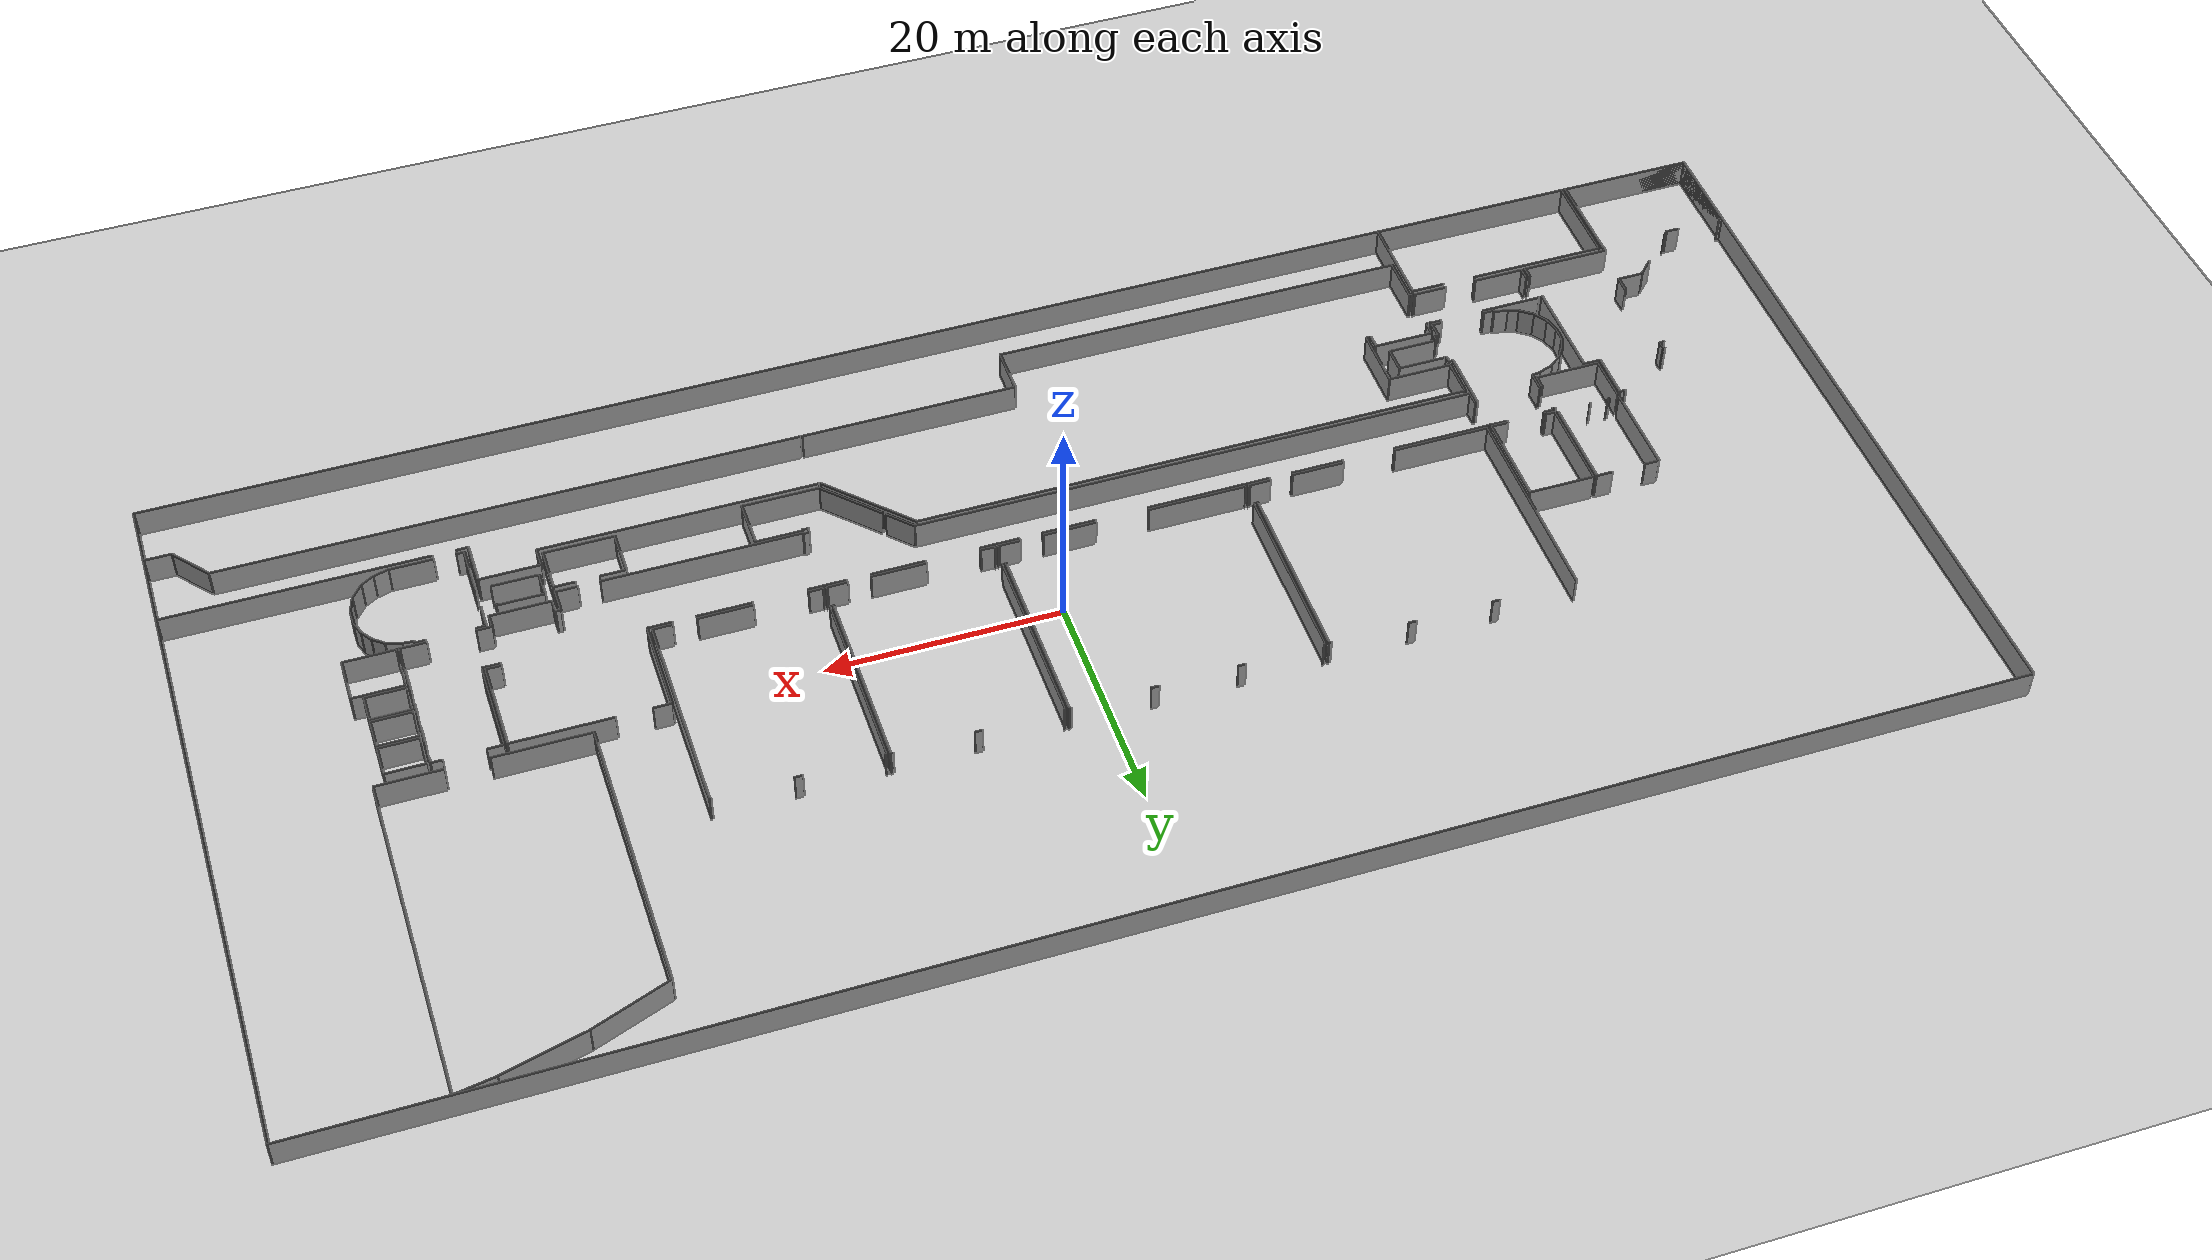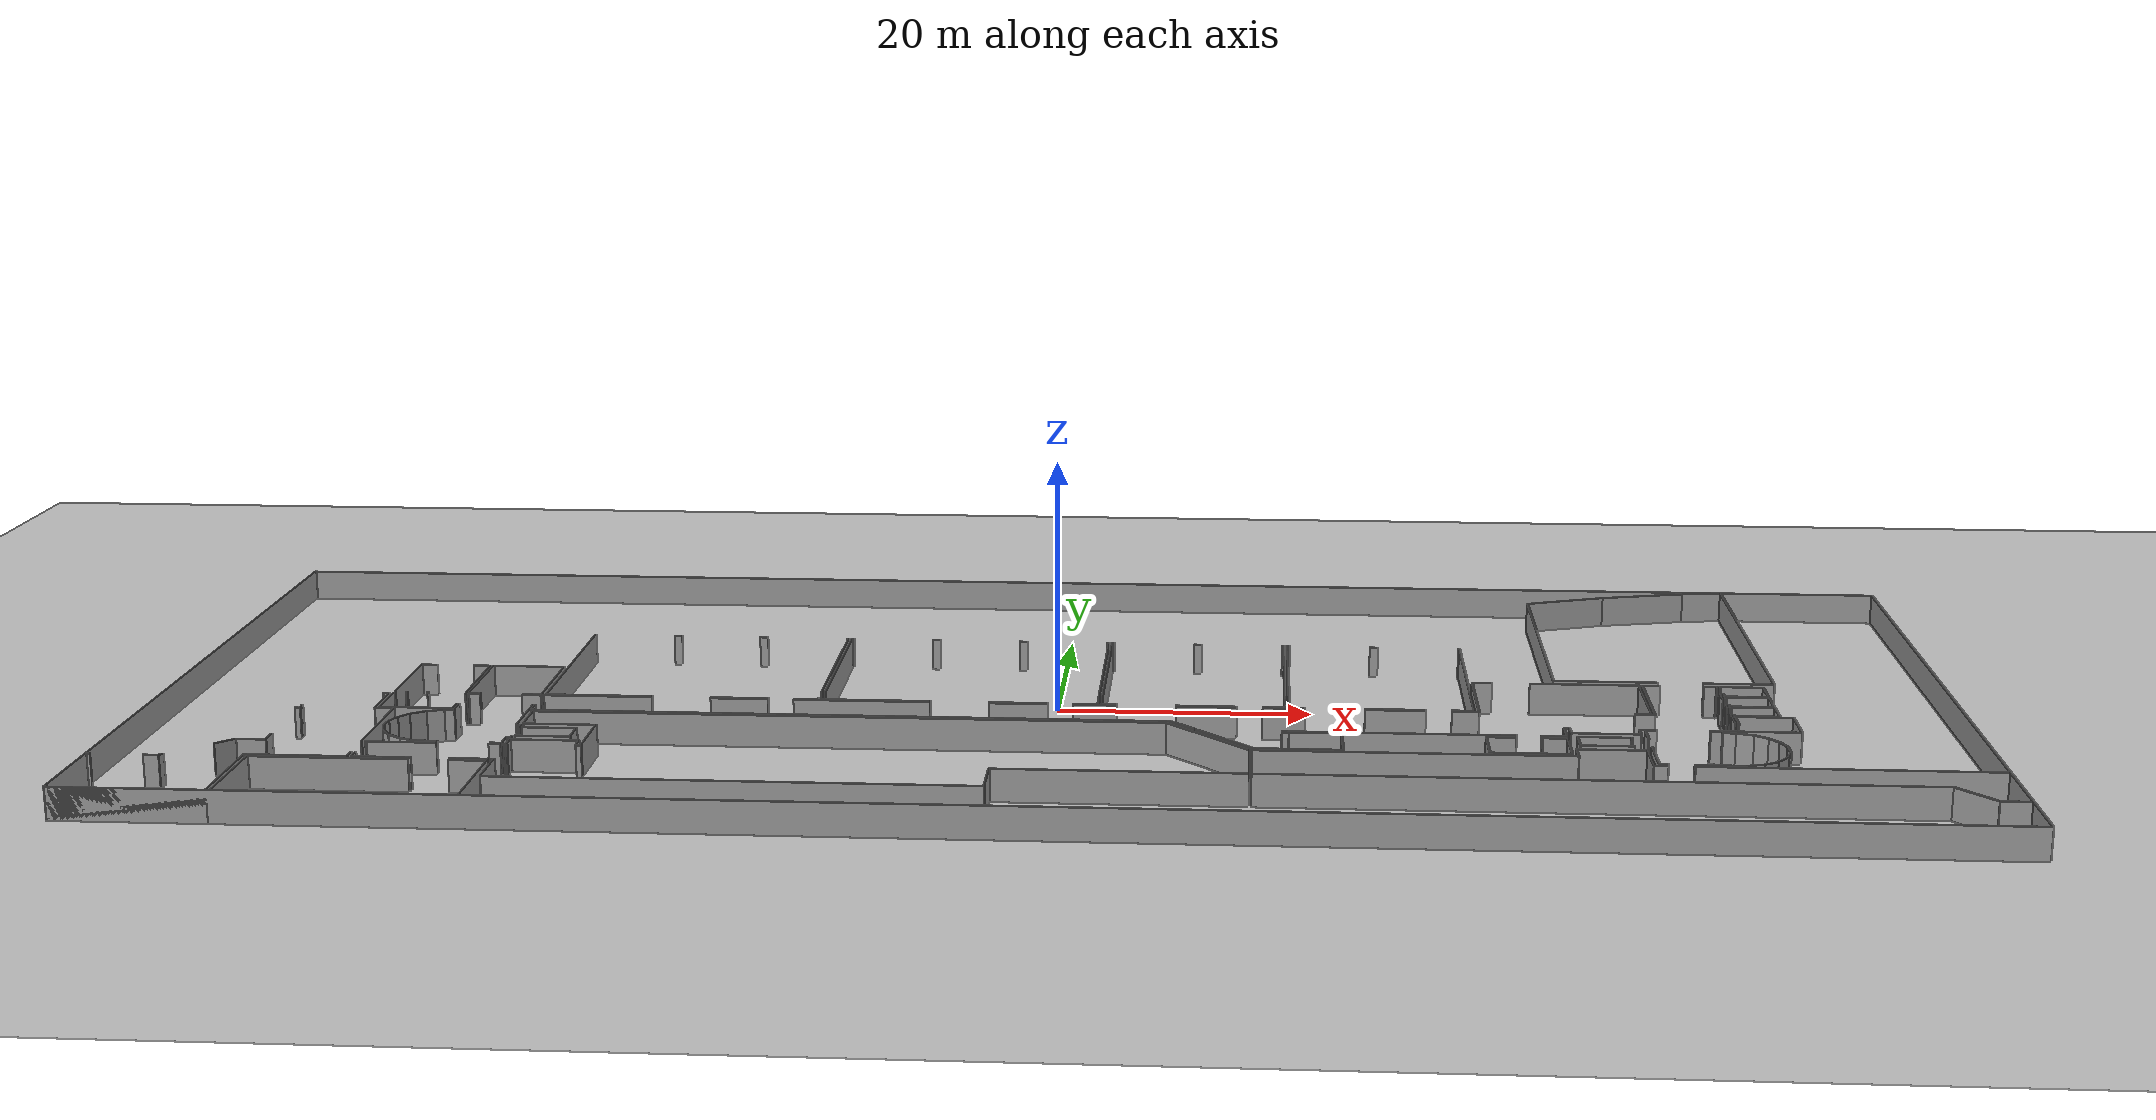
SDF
<sdf version="1.6">
  <world name="default">
    <light name="sun" type="directional">
      <cast_shadows>1</cast_shadows>
      <pose frame="">0 0 10 0 -0 0</pose>
      <diffuse>0.8 0.8 0.8 1</diffuse>
      <specular>0.1 0.1 0.1 1</specular>
      <attenuation>
        <range>1000</range>
        <constant>0.9</constant>
        <linear>0.01</linear>
        <quadratic>0.001</quadratic>
      </attenuation>
      <direction>-0.5 0.5 -1</direction>
    </light>
    <model name="ground_plane">
      <static>1</static>
      <link name="link">
        <collision name="collision">
          <geometry>
            <plane>
              <normal>0 0 1</normal>
              <size>100 100</size>
            </plane>
          </geometry>
          <surface>
            <friction>
              <ode>
                <mu>100</mu>
                <mu2>50</mu2>
              </ode>
              <torsional>
                <ode />
              </torsional>
            </friction>
            <contact>
              <ode />
            </contact>
            <bounce />
          </surface>
          <max_contacts>10</max_contacts>
        </collision>
        <visual name="visual">
          <cast_shadows>0</cast_shadows>
          <geometry>
            <plane>
              <normal>0 0 1</normal>
              <size>100 100</size>
            </plane>
          </geometry>
          <material>
            <script>
              <uri>file://media/materials/scripts/gazebo.material</uri>
              <name>Gazebo/Grey</name>
            </script>
          </material>
        </visual>
        <self_collide>0</self_collide>
        <kinematic>0</kinematic>
        <gravity>1</gravity>
      </link>
    </model>
    <gravity>0 0 -9.8</gravity>
    <magnetic_field>6e-06 2.3e-05 -4.2e-05</magnetic_field>
    <atmosphere type="adiabatic" />
    <physics default="0" name="default_physics" type="ode">
      <max_step_size>0.001</max_step_size>
      <real_time_factor>1</real_time_factor>
      <real_time_update_rate>1000</real_time_update_rate>
    </physics>
    <scene>
      <ambient>0.4 0.4 0.4 1</ambient>
      <background>0.7 0.7 0.7 1</background>
      <shadows>1</shadows>
    </scene>
    <spherical_coordinates>
      <surface_model>EARTH_WGS84</surface_model>
      <latitude_deg>0</latitude_deg>
      <longitude_deg>0</longitude_deg>
      <elevation>0</elevation>
      <heading_deg>0</heading_deg>
    </spherical_coordinates>
  <model name="0510032216_A-40">
		<static>1</static>
		<link name="Wall_0">
			<collision name="Wall_0_Collision">
				<geometry>
					<box>
						<size>0.0812517853175 0.1 2.5</size>
					</box>
				</geometry>
				<pose frame="">0.0406258926588 0 1.25 0 0 0</pose>
			</collision>
			<visual name="Wall_0_Visual">
				<pose frame="">0.0406258926588 0 1.25 0 0 0</pose>
				<geometry>
					<box>
						<size>0.0812517853175 0.1 2.5</size>
					</box>
				</geometry>
				<material>
					<script>
						<uri>file://media/materials/scripts/gazebo.material</uri>
						<name>Gazebo/Grey</name>
					</script>
					<ambient>1 1 1 1</ambient>
				</material>
			</visual>
			<pose frame="">20.5730789983 -38.4648109944 0 0 0 -1.57079632679</pose>
		</link>
		<link name="Wall_1">
			<collision name="Wall_1_Collision">
				<geometry>
					<box>
						<size>0.076808328308 0.1 2.5</size>
					</box>
				</geometry>
				<pose frame="">0.038404164154 0 1.25 0 0 0</pose>
			</collision>
			<visual name="Wall_1_Visual">
				<pose frame="">0.038404164154 0 1.25 0 0 0</pose>
				<geometry>
					<box>
						<size>0.076808328308 0.1 2.5</size>
					</box>
				</geometry>
				<material>
					<script>
						<uri>file://media/materials/scripts/gazebo.material</uri>
						<name>Gazebo/Grey</name>
					</script>
					<ambient>1 1 1 1</ambient>
				</material>
			</visual>
			<pose frame="">20.5730789983 -38.5460627797 0 0 0 3.14159265359</pose>
		</link>
		<link name="Wall_2">
			<collision name="Wall_2_Collision">
				<geometry>
					<box>
						<size>0.115149014505 0.1 2.5</size>
					</box>
				</geometry>
				<pose frame="">0.0575745072524 0 1.25 0 0 0</pose>
			</collision>
			<visual name="Wall_2_Visual">
				<pose frame="">0.0575745072524 0 1.25 0 0 0</pose>
				<geometry>
					<box>
						<size>0.115149014505 0.1 2.5</size>
					</box>
				</geometry>
				<material>
					<script>
						<uri>file://media/materials/scripts/gazebo.material</uri>
						<name>Gazebo/Grey</name>
					</script>
					<ambient>1 1 1 1</ambient>
				</material>
			</visual>
			<pose frame="">18.9550258673 -38.5460627797 0 0 0 3.14159265359</pose>
		</link>
		<link name="Wall_3">
			<collision name="Wall_3_Collision">
				<geometry>
					<box>
						<size>0.0892500079348 0.1 2.5</size>
					</box>
				</geometry>
				<pose frame="">0.0446250039674 0 1.25 0 0 0</pose>
			</collision>
			<visual name="Wall_3_Visual">
				<pose frame="">0.0446250039674 0 1.25 0 0 0</pose>
				<geometry>
					<box>
						<size>0.0892500079348 0.1 2.5</size>
					</box>
				</geometry>
				<material>
					<script>
						<uri>file://media/materials/scripts/gazebo.material</uri>
						<name>Gazebo/Grey</name>
					</script>
					<ambient>1 1 1 1</ambient>
				</material>
			</visual>
			<pose frame="">18.8398768528 -38.5460627797 0 0 0 1.57079632679</pose>
		</link>
		<link name="Wall_4">
			<collision name="Wall_4_Collision">
				<geometry>
					<box>
						<size>7.91328911036 0.1 2.5</size>
					</box>
				</geometry>
				<pose frame="">3.95664455518 0 1.25 0 0 0</pose>
			</collision>
			<visual name="Wall_4_Visual">
				<pose frame="">3.95664455518 0 1.25 0 0 0</pose>
				<geometry>
					<box>
						<size>7.91328911036 0.1 2.5</size>
					</box>
				</geometry>
				<material>
					<script>
						<uri>file://media/materials/scripts/gazebo.material</uri>
						<name>Gazebo/Grey</name>
					</script>
					<ambient>1 1 1 1</ambient>
				</material>
			</visual>
			<pose frame="">17.9429333164 -38.4568127718 0 0 0 1.57079632679</pose>
		</link>
		<link name="Wall_5">
			<collision name="Wall_5_Collision">
				<geometry>
					<box>
						<size>1.26892436601 0.1 2.5</size>
					</box>
				</geometry>
				<pose frame="">0.634462183007 0 1.25 0 0 0</pose>
			</collision>
			<visual name="Wall_5_Visual">
				<pose frame="">0.634462183007 0 1.25 0 0 0</pose>
				<geometry>
					<box>
						<size>1.26892436601 0.1 2.5</size>
					</box>
				</geometry>
				<material>
					<script>
						<uri>file://media/materials/scripts/gazebo.material</uri>
						<name>Gazebo/Grey</name>
					</script>
					<ambient>1 1 1 1</ambient>
				</material>
			</visual>
			<pose frame="">17.9429333164 -30.5435236614 0 0 0 0.0</pose>
		</link>
		<link name="Wall_6">
			<collision name="Wall_6_Collision">
				<geometry>
					<box>
						<size>1.42152537531 0.1 2.5</size>
					</box>
				</geometry>
				<pose frame="">0.710762687657 0 1.25 0 0 0</pose>
			</collision>
			<visual name="Wall_6_Visual">
				<pose frame="">0.710762687657 0 1.25 0 0 0</pose>
				<geometry>
					<box>
						<size>1.42152537531 0.1 2.5</size>
					</box>
				</geometry>
				<material>
					<script>
						<uri>file://media/materials/scripts/gazebo.material</uri>
						<name>Gazebo/Grey</name>
					</script>
					<ambient>1 1 1 1</ambient>
				</material>
			</visual>
			<pose frame="">22.1318437173 -30.5435236614 0 0 0 0.0</pose>
		</link>
		<link name="Wall_7">
			<collision name="Wall_7_Collision">
				<geometry>
					<box>
						<size>7.92128770025 0.1 2.5</size>
					</box>
				</geometry>
				<pose frame="">3.96064385012 0 1.25 0 0 0</pose>
			</collision>
			<visual name="Wall_7_Visual">
				<pose frame="">3.96064385012 0 1.25 0 0 0</pose>
				<geometry>
					<box>
						<size>7.92128770025 0.1 2.5</size>
					</box>
				</geometry>
				<material>
					<script>
						<uri>file://media/materials/scripts/gazebo.material</uri>
						<name>Gazebo/Grey</name>
					</script>
					<ambient>1 1 1 1</ambient>
				</material>
			</visual>
			<pose frame="">23.5533690926 -30.5435236614 0 0 0 -1.57049181034</pose>
		</link>
		<link name="Wall_8">
			<collision name="Wall_8_Collision">
				<geometry>
					<box>
						<size>5.66185292157 0.1 2.5</size>
					</box>
				</geometry>
				<pose frame="">2.83092646079 0 1.25 0 0 0</pose>
			</collision>
			<visual name="Wall_8_Visual">
				<pose frame="">2.83092646079 0 1.25 0 0 0</pose>
				<geometry>
					<box>
						<size>5.66185292157 0.1 2.5</size>
					</box>
				</geometry>
				<material>
					<script>
						<uri>file://media/materials/scripts/gazebo.material</uri>
						<name>Gazebo/Grey</name>
					</script>
					<ambient>1 1 1 1</ambient>
				</material>
			</visual>
			<pose frame="">23.5984384423 -42.7678547624 0 0 0 3.14159265359</pose>
		</link>
		<link name="Wall_9">
			<collision name="Wall_9_Collision">
				<geometry>
					<box>
						<size>3.99314438061 0.1 2.5</size>
					</box>
				</geometry>
				<pose frame="">1.99657219031 0 1.25 0 0 0</pose>
			</collision>
			<visual name="Wall_9_Visual">
				<pose frame="">1.99657219031 0 1.25 0 0 0</pose>
				<geometry>
					<box>
						<size>3.99314438061 0.1 2.5</size>
					</box>
				</geometry>
				<material>
					<script>
						<uri>file://media/materials/scripts/gazebo.material</uri>
						<name>Gazebo/Grey</name>
					</script>
					<ambient>1 1 1 1</ambient>
				</material>
			</visual>
			<pose frame="">17.9365855207 -42.7678547624 0 0 0 1.57079632679</pose>
		</link>
		<link name="Wall_10">
			<collision name="Wall_10_Collision">
				<geometry>
					<box>
						<size>0.174437426604 0.1 2.5</size>
					</box>
				</geometry>
				<pose frame="">0.0872187133018 0 1.25 0 0 0</pose>
			</collision>
			<visual name="Wall_10_Visual">
				<pose frame="">0.0872187133018 0 1.25 0 0 0</pose>
				<geometry>
					<box>
						<size>0.174437426604 0.1 2.5</size>
					</box>
				</geometry>
				<material>
					<script>
						<uri>file://media/materials/scripts/gazebo.material</uri>
						<name>Gazebo/Grey</name>
					</script>
					<ambient>1 1 1 1</ambient>
				</material>
			</visual>
			<pose frame="">23.6299235091 -38.7747103818 0 0 0 -1.57079632679</pose>
		</link>
		<link name="Wall_11">
			<collision name="Wall_11_Collision">
				<geometry>
					<box>
						<size>1.19329321259 0.1 2.5</size>
					</box>
				</geometry>
				<pose frame="">0.596646606294 0 1.25 0 0 0</pose>
			</collision>
			<visual name="Wall_11_Visual">
				<pose frame="">0.596646606294 0 1.25 0 0 0</pose>
				<geometry>
					<box>
						<size>1.19329321259 0.1 2.5</size>
					</box>
				</geometry>
				<material>
					<script>
						<uri>file://media/materials/scripts/gazebo.material</uri>
						<name>Gazebo/Grey</name>
					</script>
					<ambient>1 1 1 1</ambient>
				</material>
			</visual>
			<pose frame="">23.6299235091 -41.5749769892 0 0 0 -1.59718441044</pose>
		</link>
		<link name="Wall_12">
			<collision name="Wall_12_Collision">
				<geometry>
					<box>
						<size>1.50265020472 0.1 2.5</size>
					</box>
				</geometry>
				<pose frame="">0.751325102358 0 1.25 0 0 0</pose>
			</collision>
			<visual name="Wall_12_Visual">
				<pose frame="">0.751325102358 0 1.25 0 0 0</pose>
				<geometry>
					<box>
						<size>1.50265020472 0.1 2.5</size>
					</box>
				</geometry>
				<material>
					<script>
						<uri>file://media/materials/scripts/gazebo.material</uri>
						<name>Gazebo/Grey</name>
					</script>
					<ambient>1 1 1 1</ambient>
				</material>
			</visual>
			<pose frame="">29.5272796521 -38.5732313454 0 0 0 3.14159265359</pose>
		</link>
		<link name="Wall_13">
			<collision name="Wall_13_Collision">
				<geometry>
					<box>
						<size>0.116164661821 0.1 2.5</size>
					</box>
				</geometry>
				<pose frame="">0.0580823309106 0 1.25 0 0 0</pose>
			</collision>
			<visual name="Wall_13_Visual">
				<pose frame="">0.0580823309106 0 1.25 0 0 0</pose>
				<geometry>
					<box>
						<size>0.116164661821 0.1 2.5</size>
					</box>
				</geometry>
				<material>
					<script>
						<uri>file://media/materials/scripts/gazebo.material</uri>
						<name>Gazebo/Grey</name>
					</script>
					<ambient>1 1 1 1</ambient>
				</material>
			</visual>
			<pose frame="">24.7219982861 -38.5732313454 0 0 0 3.14159265359</pose>
		</link>
		<link name="Wall_14">
			<collision name="Wall_14_Collision">
				<geometry>
					<box>
						<size>0.0870917573872 0.1 2.5</size>
					</box>
				</geometry>
				<pose frame="">0.0435458786936 0 1.25 0 0 0</pose>
			</collision>
			<visual name="Wall_14_Visual">
				<pose frame="">0.0435458786936 0 1.25 0 0 0</pose>
				<geometry>
					<box>
						<size>0.0870917573872 0.1 2.5</size>
					</box>
				</geometry>
				<material>
					<script>
						<uri>file://media/materials/scripts/gazebo.material</uri>
						<name>Gazebo/Grey</name>
					</script>
					<ambient>1 1 1 1</ambient>
				</material>
			</visual>
			<pose frame="">24.6058336243 -38.5732313454 0 0 0 1.57079632679</pose>
		</link>
		<link name="Wall_15">
			<collision name="Wall_15_Collision">
				<geometry>
					<box>
						<size>0.813025676834 0.1 2.5</size>
					</box>
				</geometry>
				<pose frame="">0.406512838417 0 1.25 0 0 0</pose>
			</collision>
			<visual name="Wall_15_Visual">
				<pose frame="">0.406512838417 0 1.25 0 0 0</pose>
				<geometry>
					<box>
						<size>0.813025676834 0.1 2.5</size>
					</box>
				</geometry>
				<material>
					<script>
						<uri>file://media/materials/scripts/gazebo.material</uri>
						<name>Gazebo/Grey</name>
					</script>
					<ambient>1 1 1 1</ambient>
				</material>
			</visual>
			<pose frame="">24.6058336243 -38.486139588 0 0 0 3.14159265359</pose>
		</link>
		<link name="Wall_16">
			<collision name="Wall_16_Collision">
				<geometry>
					<box>
						<size>7.94832894277 0.1 2.5</size>
					</box>
				</geometry>
				<pose frame="">3.97416447139 0 1.25 0 0 0</pose>
			</collision>
			<visual name="Wall_16_Visual">
				<pose frame="">3.97416447139 0 1.25 0 0 0</pose>
				<geometry>
					<box>
						<size>7.94832894277 0.1 2.5</size>
					</box>
				</geometry>
				<material>
					<script>
						<uri>file://media/materials/scripts/gazebo.material</uri>
						<name>Gazebo/Grey</name>
					</script>
					<ambient>1 1 1 1</ambient>
				</material>
			</visual>
			<pose frame="">23.7928079474 -38.486139588 0 0 0 1.57079632679</pose>
		</link>
		<link name="Wall_17">
			<collision name="Wall_17_Collision">
				<geometry>
					<box>
						<size>5.72710826166 0.1 2.5</size>
					</box>
				</geometry>
				<pose frame="">2.86355413083 0 1.25 0 0 0</pose>
			</collision>
			<visual name="Wall_17_Visual">
				<pose frame="">2.86355413083 0 1.25 0 0 0</pose>
				<geometry>
					<box>
						<size>5.72710826166 0.1 2.5</size>
					</box>
				</geometry>
				<material>
					<script>
						<uri>file://media/materials/scripts/gazebo.material</uri>
						<name>Gazebo/Grey</name>
					</script>
					<ambient>1 1 1 1</ambient>
				</material>
			</visual>
			<pose frame="">23.7928079474 -30.5378106453 0 0 0 0.0</pose>
		</link>
		<link name="Wall_18">
			<collision name="Wall_18_Collision">
				<geometry>
					<box>
						<size>8.03542407399 0.1 2.5</size>
					</box>
				</geometry>
				<pose frame="">4.017712037 0 1.25 0 0 0</pose>
			</collision>
			<visual name="Wall_18_Visual">
				<pose frame="">4.017712037 0 1.25 0 0 0</pose>
				<geometry>
					<box>
						<size>8.03542407399 0.1 2.5</size>
					</box>
				</geometry>
				<material>
					<script>
						<uri>file://media/materials/scripts/gazebo.material</uri>
						<name>Gazebo/Grey</name>
					</script>
					<ambient>1 1 1 1</ambient>
				</material>
			</visual>
			<pose frame="">29.5199162091 -30.5378106453 0 0 0 -1.56987995399</pose>
		</link>
		<link name="Wall_19">
			<collision name="Wall_19_Collision">
				<geometry>
					<box>
						<size>0.901513949281 0.1 2.5</size>
					</box>
				</geometry>
				<pose frame="">0.450756974641 0 1.25 0 0 0</pose>
			</collision>
			<visual name="Wall_19_Visual">
				<pose frame="">0.450756974641 0 1.25 0 0 0</pose>
				<geometry>
					<box>
						<size>0.901513949281 0.1 2.5</size>
					</box>
				</geometry>
				<material>
					<script>
						<uri>file://media/materials/scripts/gazebo.material</uri>
						<name>Gazebo/Grey</name>
					</script>
					<ambient>1 1 1 1</ambient>
				</material>
			</visual>
			<pose frame="">29.5409908909 -51.5537118736 0 0 0 3.14159265359</pose>
		</link>
		<link name="Wall_20">
			<collision name="Wall_20_Collision">
				<geometry>
					<box>
						<size>0.884882724474 0.1 2.5</size>
					</box>
				</geometry>
				<pose frame="">0.442441362237 0 1.25 0 0 0</pose>
			</collision>
			<visual name="Wall_20_Visual">
				<pose frame="">0.442441362237 0 1.25 0 0 0</pose>
				<geometry>
					<box>
						<size>0.884882724474 0.1 2.5</size>
					</box>
				</geometry>
				<material>
					<script>
						<uri>file://media/materials/scripts/gazebo.material</uri>
						<name>Gazebo/Grey</name>
					</script>
					<ambient>1 1 1 1</ambient>
				</material>
			</visual>
			<pose frame="">24.716158314 -51.5537118736 0 0 0 3.14159265359</pose>
		</link>
		<link name="Wall_21">
			<collision name="Wall_21_Collision">
				<geometry>
					<box>
						<size>0.158567937284 0.1 2.5</size>
					</box>
				</geometry>
				<pose frame="">0.0792839686419 0 1.25 0 0 0</pose>
			</collision>
			<visual name="Wall_21_Visual">
				<pose frame="">0.0792839686419 0 1.25 0 0 0</pose>
				<geometry>
					<box>
						<size>0.158567937284 0.1 2.5</size>
					</box>
				</geometry>
				<material>
					<script>
						<uri>file://media/materials/scripts/gazebo.material</uri>
						<name>Gazebo/Grey</name>
					</script>
					<ambient>1 1 1 1</ambient>
				</material>
			</visual>
			<pose frame="">23.8312755896 -51.5537118736 0 0 0 1.57079632679</pose>
		</link>
		<link name="Wall_22">
			<collision name="Wall_22_Collision">
				<geometry>
					<box>
						<size>1.19828313626 0.1 2.5</size>
					</box>
				</geometry>
				<pose frame="">0.599141568131 0 1.25 0 0 0</pose>
			</collision>
			<visual name="Wall_22_Visual">
				<pose frame="">0.599141568131 0 1.25 0 0 0</pose>
				<geometry>
					<box>
						<size>1.19828313626 0.1 2.5</size>
					</box>
				</geometry>
				<material>
					<script>
						<uri>file://media/materials/scripts/gazebo.material</uri>
						<name>Gazebo/Grey</name>
					</script>
					<ambient>1 1 1 1</ambient>
				</material>
			</visual>
			<pose frame="">23.8312755896 -51.3951439363 0 0 0 2.9947510783</pose>
		</link>
		<link name="Wall_23">
			<collision name="Wall_23_Collision">
				<geometry>
					<box>
						<size>0.947020817735 0.1 2.5</size>
					</box>
				</geometry>
				<pose frame="">0.473510408868 0 1.25 0 0 0</pose>
			</collision>
			<visual name="Wall_23_Visual">
				<pose frame="">0.473510408868 0 1.25 0 0 0</pose>
				<geometry>
					<box>
						<size>0.947020817735 0.1 2.5</size>
					</box>
				</geometry>
				<material>
					<script>
						<uri>file://media/materials/scripts/gazebo.material</uri>
						<name>Gazebo/Grey</name>
					</script>
					<ambient>1 1 1 1</ambient>
				</material>
			</visual>
			<pose frame="">22.6458882153 -51.2198178183 0 0 0 2.75289606404</pose>
		</link>
		<link name="Wall_24">
			<collision name="Wall_24_Collision">
				<geometry>
					<box>
						<size>1.36073929065 0.1 2.5</size>
					</box>
				</geometry>
				<pose frame="">0.680369645325 0 1.25 0 0 0</pose>
			</collision>
			<visual name="Wall_24_Visual">
				<pose frame="">0.680369645325 0 1.25 0 0 0</pose>
				<geometry>
					<box>
						<size>1.36073929065 0.1 2.5</size>
					</box>
				</geometry>
				<material>
					<script>
						<uri>file://media/materials/scripts/gazebo.material</uri>
						<name>Gazebo/Grey</name>
					</script>
					<ambient>1 1 1 1</ambient>
				</material>
			</visual>
			<pose frame="">21.7695115371 -50.8609134478 0 0 0 2.50424933224</pose>
		</link>
		<link name="Wall_25">
			<collision name="Wall_25_Collision">
				<geometry>
					<box>
						<size>1.3291789881 0.1 2.5</size>
					</box>
				</geometry>
				<pose frame="">0.664589494048 0 1.25 0 0 0</pose>
			</collision>
			<visual name="Wall_25_Visual">
				<pose frame="">0.664589494048 0 1.25 0 0 0</pose>
				<geometry>
					<box>
						<size>1.3291789881 0.1 2.5</size>
					</box>
				</geometry>
				<material>
					<script>
						<uri>file://media/materials/scripts/gazebo.material</uri>
						<name>Gazebo/Grey</name>
					</script>
					<ambient>1 1 1 1</ambient>
				</material>
			</visual>
			<pose frame="">20.6759132891 -50.0511886248 0 0 0 2.14139348688</pose>
		</link>
		<link name="Wall_26">
			<collision name="Wall_26_Collision">
				<geometry>
					<box>
						<size>1.26137519619 0.1 2.5</size>
					</box>
				</geometry>
				<pose frame="">0.630687598094 0 1.25 0 0 0</pose>
			</collision>
			<visual name="Wall_26_Visual">
				<pose frame="">0.630687598094 0 1.25 0 0 0</pose>
				<geometry>
					<box>
						<size>1.26137519619 0.1 2.5</size>
					</box>
				</geometry>
				<material>
					<script>
						<uri>file://media/materials/scripts/gazebo.material</uri>
						<name>Gazebo/Grey</name>
					</script>
					<ambient>1 1 1 1</ambient>
				</material>
			</visual>
			<pose frame="">19.9579775923 -48.9325800616 0 0 0 1.83181365359</pose>
		</link>
		<link name="Wall_27">
			<collision name="Wall_27_Collision">
				<geometry>
					<box>
						<size>1.21085813327 0.1 2.5</size>
					</box>
				</geometry>
				<pose frame="">0.605429066636 0 1.25 0 0 0</pose>
			</collision>
			<visual name="Wall_27_Visual">
				<pose frame="">0.605429066636 0 1.25 0 0 0</pose>
				<geometry>
					<box>
						<size>1.21085813327 0.1 2.5</size>
					</box>
				</geometry>
				<material>
					<script>
						<uri>file://media/materials/scripts/gazebo.material</uri>
						<name>Gazebo/Grey</name>
					</script>
					<ambient>1 1 1 1</ambient>
				</material>
			</visual>
			<pose frame="">19.6324626274 -47.7139302377 0 0 0 1.54321783721</pose>
		</link>
		<link name="Wall_28">
			<collision name="Wall_28_Collision">
				<geometry>
					<box>
						<size>1.10222361702 0.1 2.5</size>
					</box>
				</geometry>
				<pose frame="">0.551111808512 0 1.25 0 0 0</pose>
			</collision>
			<visual name="Wall_28_Visual">
				<pose frame="">0.551111808512 0 1.25 0 0 0</pose>
				<geometry>
					<box>
						<size>1.10222361702 0.1 2.5</size>
					</box>
				</geometry>
				<material>
					<script>
						<uri>file://media/materials/scripts/gazebo.material</uri>
						<name>Gazebo/Grey</name>
					</script>
					<ambient>1 1 1 1</ambient>
				</material>
			</visual>
			<pose frame="">19.6658520329 -46.5035325483 0 0 0 1.198759973</pose>
		</link>
		<link name="Wall_29">
			<collision name="Wall_29_Collision">
				<geometry>
					<box>
						<size>1.16465529562 0.1 2.5</size>
					</box>
				</geometry>
				<pose frame="">0.582327647812 0 1.25 0 0 0</pose>
			</collision>
			<visual name="Wall_29_Visual">
				<pose frame="">0.582327647812 0 1.25 0 0 0</pose>
				<geometry>
					<box>
						<size>1.16465529562 0.1 2.5</size>
					</box>
				</geometry>
				<material>
					<script>
						<uri>file://media/materials/scripts/gazebo.material</uri>
						<name>Gazebo/Grey</name>
					</script>
					<ambient>1 1 1 1</ambient>
				</material>
			</visual>
			<pose frame="">20.0665248992 -45.4767131114 0 0 0 0.968795302871</pose>
		</link>
		<link name="Wall_30">
			<collision name="Wall_30_Collision">
				<geometry>
					<box>
						<size>1.35574257779 0.1 2.5</size>
					</box>
				</geometry>
				<pose frame="">0.677871288893 0 1.25 0 0 0</pose>
			</collision>
			<visual name="Wall_30_Visual">
				<pose frame="">0.677871288893 0 1.25 0 0 0</pose>
				<geometry>
					<box>
						<size>1.35574257779 0.1 2.5</size>
					</box>
				</geometry>
				<material>
					<script>
						<uri>file://media/materials/scripts/gazebo.material</uri>
						<name>Gazebo/Grey</name>
					</script>
					<ambient>1 1 1 1</ambient>
				</material>
			</visual>
			<pose frame="">20.7260608754 -44.5167994414 0 0 0 0.6325071894</pose>
		</link>
		<link name="Wall_31">
			<collision name="Wall_31_Collision">
				<geometry>
					<box>
						<size>1.33589536492 0.1 2.5</size>
					</box>
				</geometry>
				<pose frame="">0.667947682459 0 1.25 0 0 0</pose>
			</collision>
			<visual name="Wall_31_Visual">
				<pose frame="">0.667947682459 0 1.25 0 0 0</pose>
				<geometry>
					<box>
						<size>1.33589536492 0.1 2.5</size>
					</box>
				</geometry>
				<material>
					<script>
						<uri>file://media/materials/scripts/gazebo.material</uri>
						<name>Gazebo/Grey</name>
					</script>
					<ambient>1 1 1 1</ambient>
				</material>
			</visual>
			<pose frame="">21.8195321675 -43.7153267528 0 0 0 0.337468655107</pose>
		</link>
		<link name="Wall_32">
			<collision name="Wall_32_Collision">
				<geometry>
					<box>
						<size>0.747869631669 0.1 2.5</size>
					</box>
				</geometry>
				<pose frame="">0.373934815834 0 1.25 0 0 0</pose>
			</collision>
			<visual name="Wall_32_Visual">
				<pose frame="">0.373934815834 0 1.25 0 0 0</pose>
				<geometry>
					<box>
						<size>0.747869631669 0.1 2.5</size>
					</box>
				</geometry>
				<material>
					<script>
						<uri>file://media/materials/scripts/gazebo.material</uri>
						<name>Gazebo/Grey</name>
					</script>
					<ambient>1 1 1 1</ambient>
				</material>
			</visual>
			<pose frame="">23.0800774431 -43.2730123465 0 0 0 0.124755053481</pose>
		</link>
		<link name="Wall_33">
			<collision name="Wall_33_Collision">
				<geometry>
					<box>
						<size>1.61284793855 0.1 2.5</size>
					</box>
				</geometry>
				<pose frame="">0.806423969277 0 1.25 0 0 0</pose>
			</collision>
			<visual name="Wall_33_Visual">
				<pose frame="">0.806423969277 0 1.25 0 0 0</pose>
				<geometry>
					<box>
						<size>1.61284793855 0.1 2.5</size>
					</box>
				</geometry>
				<material>
					<script>
						<uri>file://media/materials/scripts/gazebo.material</uri>
						<name>Gazebo/Grey</name>
					</script>
					<ambient>1 1 1 1</ambient>
				</material>
			</visual>
			<pose frame="">23.8221347637 -43.1799536611 0 0 0 1.57079632679</pose>
		</link>
		<link name="Wall_34">
			<collision name="Wall_34_Collision">
				<geometry>
					<box>
						<size>0.196019932079 0.1 2.5</size>
					</box>
				</geometry>
				<pose frame="">0.0980099660393 0 1.25 0 0 0</pose>
			</collision>
			<visual name="Wall_34_Visual">
				<pose frame="">0.0980099660393 0 1.25 0 0 0</pose>
				<geometry>
					<box>
						<size>0.196019932079 0.1 2.5</size>
					</box>
				</geometry>
				<material>
					<script>
						<uri>file://media/materials/scripts/gazebo.material</uri>
						<name>Gazebo/Grey</name>
					</script>
					<ambient>1 1 1 1</ambient>
				</material>
			</visual>
			<pose frame="">23.8221347637 -38.9652712096 0 0 0 1.57079632679</pose>
		</link>
		<link name="Wall_35">
			<collision name="Wall_35_Collision">
				<geometry>
					<box>
						<size>0.892500079347 0.1 2.5</size>
					</box>
				</geometry>
				<pose frame="">0.446250039674 0 1.25 0 0 0</pose>
			</collision>
			<visual name="Wall_35_Visual">
				<pose frame="">0.446250039674 0 1.25 0 0 0</pose>
				<geometry>
					<box>
						<size>0.892500079347 0.1 2.5</size>
					</box>
				</geometry>
				<material>
					<script>
						<uri>file://media/materials/scripts/gazebo.material</uri>
						<name>Gazebo/Grey</name>
					</script>
					<ambient>1 1 1 1</ambient>
				</material>
			</visual>
			<pose frame="">23.8221347637 -38.7692512775 0 0 0 0.0</pose>
		</link>
		<link name="Wall_36">
			<collision name="Wall_36_Collision">
				<geometry>
					<box>
						<size>1.53591265433 0.1 2.5</size>
					</box>
				</geometry>
				<pose frame="">0.767956327165 0 1.25 0 0 0</pose>
			</collision>
			<visual name="Wall_36_Visual">
				<pose frame="">0.767956327165 0 1.25 0 0 0</pose>
				<geometry>
					<box>
						<size>1.53591265433 0.1 2.5</size>
					</box>
				</geometry>
				<material>
					<script>
						<uri>file://media/materials/scripts/gazebo.material</uri>
						<name>Gazebo/Grey</name>
					</script>
					<ambient>1 1 1 1</ambient>
				</material>
			</visual>
			<pose frame="">27.9956834989 -38.7692512775 0 0 0 0.0</pose>
		</link>
		<link name="Wall_37">
			<collision name="Wall_37_Collision">
				<geometry>
					<box>
						<size>0.0978830101247 0.1 2.5</size>
					</box>
				</geometry>
				<pose frame="">0.0489415050624 0 1.25 0 0 0</pose>
			</collision>
			<visual name="Wall_37_Visual">
				<pose frame="">0.0489415050624 0 1.25 0 0 0</pose>
				<geometry>
					<box>
						<size>0.0978830101247 0.1 2.5</size>
					</box>
				</geometry>
				<material>
					<script>
						<uri>file://media/materials/scripts/gazebo.material</uri>
						<name>Gazebo/Grey</name>
					</script>
					<ambient>1 1 1 1</ambient>
				</material>
			</visual>
			<pose frame="">29.5315961532 -38.7692512775 0 0 0 -1.57079632679</pose>
		</link>
		<link name="Wall_38">
			<collision name="Wall_38_Collision">
				<geometry>
					<box>
						<size>5.35182657822 0.1 2.5</size>
					</box>
				</geometry>
				<pose frame="">2.67591328911 0 1.25 0 0 0</pose>
			</collision>
			<visual name="Wall_38_Visual">
				<pose frame="">2.67591328911 0 1.25 0 0 0</pose>
				<geometry>
					<box>
						<size>5.35182657822 0.1 2.5</size>
					</box>
				</geometry>
				<material>
					<script>
						<uri>file://media/materials/scripts/gazebo.material</uri>
						<name>Gazebo/Grey</name>
					</script>
					<ambient>1 1 1 1</ambient>
				</material>
			</visual>
			<pose frame="">29.5315961532 -41.5617735741 0 0 0 -1.57079632679</pose>
		</link>
		<link name="Wall_39">
			<collision name="Wall_39_Collision">
				<geometry>
					<box>
						<size>0.358523502714 0.1 2.5</size>
					</box>
				</geometry>
				<pose frame="">0.179261751357 0 1.25 0 0 0</pose>
			</collision>
			<visual name="Wall_39_Visual">
				<pose frame="">0.179261751357 0 1.25 0 0 0</pose>
				<geometry>
					<box>
						<size>0.358523502714 0.1 2.5</size>
					</box>
				</geometry>
				<material>
					<script>
						<uri>file://media/materials/scripts/gazebo.material</uri>
						<name>Gazebo/Grey</name>
					</script>
					<ambient>1 1 1 1</ambient>
				</material>
			</visual>
			<pose frame="">29.5315961532 -46.9136001523 0 0 0 0.0</pose>
		</link>
		<link name="Wall_40">
			<collision name="Wall_40_Collision">
				<geometry>
					<box>
						<size>0.544386961628 0.1 2.5</size>
					</box>
				</geometry>
				<pose frame="">0.272193480814 0 1.25 0 0 0</pose>
			</collision>
			<visual name="Wall_40_Visual">
				<pose frame="">0.272193480814 0 1.25 0 0 0</pose>
				<geometry>
					<box>
						<size>0.544386961628 0.1 2.5</size>
					</box>
				</geometry>
				<material>
					<script>
						<uri>file://media/materials/scripts/gazebo.material</uri>
						<name>Gazebo/Grey</name>
					</script>
					<ambient>1 1 1 1</ambient>
				</material>
			</visual>
			<pose frame="">29.8901196559 -46.9136001523 0 0 0 -1.57079632679</pose>
		</link>
		<link name="Wall_41">
			<collision name="Wall_41_Collision">
				<geometry>
					<box>
						<size>0.542609578824 0.1 2.5</size>
					</box>
				</geometry>
				<pose frame="">0.271304789412 0 1.25 0 0 0</pose>
			</collision>
			<visual name="Wall_41_Visual">
				<pose frame="">0.271304789412 0 1.25 0 0 0</pose>
				<geometry>
					<box>
						<size>0.542609578824 0.1 2.5</size>
					</box>
				</geometry>
				<material>
					<script>
						<uri>file://media/materials/scripts/gazebo.material</uri>
						<name>Gazebo/Grey</name>
					</script>
					<ambient>1 1 1 1</ambient>
				</material>
			</visual>
			<pose frame="">29.8901196559 -49.6671469832 0 0 0 -1.57079632679</pose>
		</link>
		<link name="Wall_42">
			<collision name="Wall_42_Collision">
				<geometry>
					<box>
						<size>0.365759989844 0.1 2.5</size>
					</box>
				</geometry>
				<pose frame="">0.182879994922 0 1.25 0 0 0</pose>
			</collision>
			<visual name="Wall_42_Visual">
				<pose frame="">0.182879994922 0 1.25 0 0 0</pose>
				<geometry>
					<box>
						<size>0.365759989844 0.1 2.5</size>
					</box>
				</geometry>
				<material>
					<script>
						<uri>file://media/materials/scripts/gazebo.material</uri>
						<name>Gazebo/Grey</name>
					</script>
					<ambient>1 1 1 1</ambient>
				</material>
			</visual>
			<pose frame="">29.8901196559 -50.209756562 0 0 0 3.14159265359</pose>
		</link>
		<link name="Wall_43">
			<collision name="Wall_43_Collision">
				<geometry>
					<box>
						<size>1.34405821191 0.1 2.5</size>
					</box>
				</geometry>
				<pose frame="">0.672029105954 0 1.25 0 0 0</pose>
			</collision>
			<visual name="Wall_43_Visual">
				<pose frame="">0.672029105954 0 1.25 0 0 0</pose>
				<geometry>
					<box>
						<size>1.34405821191 0.1 2.5</size>
					</box>
				</geometry>
				<material>
					<script>
						<uri>file://media/materials/scripts/gazebo.material</uri>
						<name>Gazebo/Grey</name>
					</script>
					<ambient>1 1 1 1</ambient>
				</material>
			</visual>
			<pose frame="">29.5243596661 -50.209756562 0 0 0 -1.55842212373</pose>
		</link>
		<link name="Wall_44">
			<collision name="Wall_44_Collision">
				<geometry>
					<box>
						<size>7.69898752658 0.1 2.5</size>
					</box>
				</geometry>
				<pose frame="">3.84949376329 0 1.25 0 0 0</pose>
			</collision>
			<visual name="Wall_44_Visual">
				<pose frame="">3.84949376329 0 1.25 0 0 0</pose>
				<geometry>
					<box>
						<size>7.69898752658 0.1 2.5</size>
					</box>
				</geometry>
				<material>
					<script>
						<uri>file://media/materials/scripts/gazebo.material</uri>
						<name>Gazebo/Grey</name>
					</script>
					<ambient>1 1 1 1</ambient>
				</material>
			</visual>
			<pose frame="">19.1662805091 -55.5731361285 0 0 0 3.14159265359</pose>
		</link>
		<link name="Wall_45">
			<collision name="Wall_45_Collision">
				<geometry>
					<box>
						<size>1.77089771747 0.1 2.5</size>
					</box>
				</geometry>
				<pose frame="">0.885448858735 0 1.25 0 0 0</pose>
			</collision>
			<visual name="Wall_45_Visual">
				<pose frame="">0.885448858735 0 1.25 0 0 0</pose>
				<geometry>
					<box>
						<size>1.77089771747 0.1 2.5</size>
					</box>
				</geometry>
				<material>
					<script>
						<uri>file://media/materials/scripts/gazebo.material</uri>
						<name>Gazebo/Grey</name>
					</script>
					<ambient>1 1 1 1</ambient>
				</material>
			</visual>
			<pose frame="">8.44777351065 -53.0762941569 0 0 0 0.77667892781</pose>
		</link>
		<link name="Wall_46">
			<collision name="Wall_46_Collision">
				<geometry>
					<box>
						<size>2.22122068112 0.1 2.5</size>
					</box>
				</geometry>
				<pose frame="">1.11061034056 0 1.25 0 0 0</pose>
			</collision>
			<visual name="Wall_46_Visual">
				<pose frame="">1.11061034056 0 1.25 0 0 0</pose>
				<geometry>
					<box>
						<size>2.22122068112 0.1 2.5</size>
					</box>
				</geometry>
				<material>
					<script>
						<uri>file://media/materials/scripts/gazebo.material</uri>
						<name>Gazebo/Grey</name>
					</script>
					<ambient>1 1 1 1</ambient>
				</material>
			</visual>
			<pose frame="">9.71085790459 -51.8350461802 0 0 0 0.0</pose>
		</link>
		<link name="Wall_47">
			<collision name="Wall_47_Collision">
				<geometry>
					<box>
						<size>1.46634081315 0.1 2.5</size>
					</box>
				</geometry>
				<pose frame="">0.733170406576 0 1.25 0 0 0</pose>
			</collision>
			<visual name="Wall_47_Visual">
				<pose frame="">0.733170406576 0 1.25 0 0 0</pose>
				<geometry>
					<box>
						<size>1.46634081315 0.1 2.5</size>
					</box>
				</geometry>
				<material>
					<script>
						<uri>file://media/materials/scripts/gazebo.material</uri>
						<name>Gazebo/Grey</name>
					</script>
					<ambient>1 1 1 1</ambient>
				</material>
			</visual>
			<pose frame="">11.9320785857 -51.8350461802 0 0 0 1.57079632679</pose>
		</link>
		<link name="Wall_48">
			<collision name="Wall_48_Collision">
				<geometry>
					<box>
						<size>0.413749325547 0.1 2.5</size>
					</box>
				</geometry>
				<pose frame="">0.206874662773 0 1.25 0 0 0</pose>
			</collision>
			<visual name="Wall_48_Visual">
				<pose frame="">0.206874662773 0 1.25 0 0 0</pose>
				<geometry>
					<box>
						<size>0.413749325547 0.1 2.5</size>
					</box>
				</geometry>
				<material>
					<script>
						<uri>file://media/materials/scripts/gazebo.material</uri>
						<name>Gazebo/Grey</name>
					</script>
					<ambient>1 1 1 1</ambient>
				</material>
			</visual>
			<pose frame="">11.50372933 -43.4075856159 0 0 0 0.0</pose>
		</link>
		<link name="Wall_49">
			<collision name="Wall_49_Collision">
				<geometry>
					<box>
						<size>0.660551623449 0.1 2.5</size>
					</box>
				</geometry>
				<pose frame="">0.330275811724 0 1.25 0 0 0</pose>
			</collision>
			<visual name="Wall_49_Visual">
				<pose frame="">0.330275811724 0 1.25 0 0 0</pose>
				<geometry>
					<box>
						<size>0.660551623449 0.1 2.5</size>
					</box>
				</geometry>
				<material>
					<script>
						<uri>file://media/materials/scripts/gazebo.material</uri>
						<name>Gazebo/Grey</name>
					</script>
					<ambient>1 1 1 1</ambient>
				</material>
			</visual>
			<pose frame="">11.9174786555 -43.4075856159 0 0 0 1.57079632679</pose>
		</link>
		<link name="Wall_50">
			<collision name="Wall_50_Collision">
				<geometry>
					<box>
						<size>0.189935425374 0.1 2.5</size>
					</box>
				</geometry>
				<pose frame="">0.0949677126869 0 1.25 0 0 0</pose>
			</collision>
			<visual name="Wall_50_Visual">
				<pose frame="">0.0949677126869 0 1.25 0 0 0</pose>
				<geometry>
					<box>
						<size>0.189935425374 0.1 2.5</size>
					</box>
				</geometry>
				<material>
					<script>
						<uri>file://media/materials/scripts/gazebo.material</uri>
						<name>Gazebo/Grey</name>
					</script>
					<ambient>1 1 1 1</ambient>
				</material>
			</visual>
			<pose frame="">11.9174786555 -42.7470339924 0 0 0 2.32925065762</pose>
		</link>
		<link name="Wall_51">
			<collision name="Wall_51_Collision">
				<geometry>
					<box>
						<size>0.157425334053 0.1 2.5</size>
					</box>
				</geometry>
				<pose frame="">0.0787126670264 0 1.25 0 0 0</pose>
			</collision>
			<visual name="Wall_51_Visual">
				<pose frame="">0.0787126670264 0 1.25 0 0 0</pose>
				<geometry>
					<box>
						<size>0.157425334053 0.1 2.5</size>
					</box>
				</geometry>
				<material>
					<script>
						<uri>file://media/materials/scripts/gazebo.material</uri>
						<name>Gazebo/Grey</name>
					</script>
					<ambient>1 1 1 1</ambient>
				</material>
			</visual>
			<pose frame="">17.1856412861 -38.8558352112 0 0 0 -1.57079632679</pose>
		</link>
		<link name="Wall_52">
			<collision name="Wall_52_Collision">
				<geometry>
					<box>
						<size>0.458183895642 0.1 2.5</size>
					</box>
				</geometry>
				<pose frame="">0.229091947821 0 1.25 0 0 0</pose>
			</collision>
			<visual name="Wall_52_Visual">
				<pose frame="">0.229091947821 0 1.25 0 0 0</pose>
				<geometry>
					<box>
						<size>0.458183895642 0.1 2.5</size>
					</box>
				</geometry>
				<material>
					<script>
						<uri>file://media/materials/scripts/gazebo.material</uri>
						<name>Gazebo/Grey</name>
					</script>
					<ambient>1 1 1 1</ambient>
				</material>
			</visual>
			<pose frame="">17.1856412861 -39.0132605453 0 0 0 0.0</pose>
		</link>
		<link name="Wall_53">
			<collision name="Wall_53_Collision">
				<geometry>
					<box>
						<size>4.03872155394 0.1 2.5</size>
					</box>
				</geometry>
				<pose frame="">2.01936077697 0 1.25 0 0 0</pose>
			</collision>
			<visual name="Wall_53_Visual">
				<pose frame="">2.01936077697 0 1.25 0 0 0</pose>
				<geometry>
					<box>
						<size>4.03872155394 0.1 2.5</size>
					</box>
				</geometry>
				<material>
					<script>
						<uri>file://media/materials/scripts/gazebo.material</uri>
						<name>Gazebo/Grey</name>
					</script>
					<ambient>1 1 1 1</ambient>
				</material>
			</visual>
			<pose frame="">17.6438251817 -39.0132605453 0 0 0 -1.57079632679</pose>
		</link>
		<link name="Wall_54">
			<collision name="Wall_54_Collision">
				<geometry>
					<box>
						<size>1.49617545307 0.1 2.5</size>
					</box>
				</geometry>
				<pose frame="">0.748087726537 0 1.25 0 0 0</pose>
			</collision>
			<visual name="Wall_54_Visual">
				<pose frame="">0.748087726537 0 1.25 0 0 0</pose>
				<geometry>
					<box>
						<size>1.49617545307 0.1 2.5</size>
					</box>
				</geometry>
				<material>
					<script>
						<uri>file://media/materials/scripts/gazebo.material</uri>
						<name>Gazebo/Grey</name>
					</script>
					<ambient>1 1 1 1</ambient>
				</material>
			</visual>
			<pose frame="">17.6438251817 -43.0519820992 0 0 0 0.0</pose>
		</link>
		<link name="Wall_55">
			<collision name="Wall_55_Collision">
				<geometry>
					<box>
						<size>8.86901323515 0.1 2.5</size>
					</box>
				</geometry>
				<pose frame="">4.43450661758 0 1.25 0 0 0</pose>
			</collision>
			<visual name="Wall_55_Visual">
				<pose frame="">4.43450661758 0 1.25 0 0 0</pose>
				<geometry>
					<box>
						<size>8.86901323515 0.1 2.5</size>
					</box>
				</geometry>
				<material>
					<script>
						<uri>file://media/materials/scripts/gazebo.material</uri>
						<name>Gazebo/Grey</name>
					</script>
					<ambient>1 1 1 1</ambient>
				</material>
			</visual>
			<pose frame="">19.1400006348 -43.0519820992 0 0 0 -1.57079632679</pose>
		</link>
		<link name="Wall_56">
			<collision name="Wall_56_Collision">
				<geometry>
					<box>
						<size>1.0563462444 0.1 2.5</size>
					</box>
				</geometry>
				<pose frame="">0.528173122201 0 1.25 0 0 0</pose>
			</collision>
			<visual name="Wall_56_Visual">
				<pose frame="">0.528173122201 0 1.25 0 0 0</pose>
				<geometry>
					<box>
						<size>1.0563462444 0.1 2.5</size>
					</box>
				</geometry>
				<material>
					<script>
						<uri>file://media/materials/scripts/gazebo.material</uri>
						<name>Gazebo/Grey</name>
					</script>
					<ambient>1 1 1 1</ambient>
				</material>
			</visual>
			<pose frame="">19.1400006348 -54.5171168312 0 0 0 -1.54591567231</pose>
		</link>
		<link name="Wall_57">
			<collision name="Wall_57_Collision">
				<geometry>
					<box>
						<size>0.0757926809915 0.1 2.5</size>
					</box>
				</geometry>
				<pose frame="">0.0378963404958 0 1.25 0 0 0</pose>
			</collision>
			<visual name="Wall_57_Visual">
				<pose frame="">0.0378963404958 0 1.25 0 0 0</pose>
				<geometry>
					<box>
						<size>0.0757926809915 0.1 2.5</size>
					</box>
				</geometry>
				<material>
					<script>
						<uri>file://media/materials/scripts/gazebo.material</uri>
						<name>Gazebo/Grey</name>
					</script>
					<ambient>1 1 1 1</ambient>
				</material>
			</visual>
			<pose frame="">29.5190275177 -51.8255244866 0 0 0 -1.57079632679</pose>
		</link>
		<link name="Wall_58">
			<collision name="Wall_58_Collision">
				<geometry>
					<box>
						<size>0.100168216587 0.1 2.5</size>
					</box>
				</geometry>
				<pose frame="">0.0500841082934 0 1.25 0 0 0</pose>
			</collision>
			<visual name="Wall_58_Visual">
				<pose frame="">0.0500841082934 0 1.25 0 0 0</pose>
				<geometry>
					<box>
						<size>0.100168216587 0.1 2.5</size>
					</box>
				</geometry>
				<material>
					<script>
						<uri>file://media/materials/scripts/gazebo.material</uri>
						<name>Gazebo/Grey</name>
					</script>
					<ambient>1 1 1 1</ambient>
				</material>
			</visual>
			<pose frame="">29.5190275177 -55.4603992764 0 0 0 -1.57079632679</pose>
		</link>
		<link name="Wall_59">
			<collision name="Wall_59_Collision">
				<geometry>
					<box>
						<size>2.90843304662 0.1 2.5</size>
					</box>
				</geometry>
				<pose frame="">1.45421652331 0 1.25 0 0 0</pose>
			</collision>
			<visual name="Wall_59_Visual">
				<pose frame="">1.45421652331 0 1.25 0 0 0</pose>
				<geometry>
					<box>
						<size>2.90843304662 0.1 2.5</size>
					</box>
				</geometry>
				<material>
					<script>
						<uri>file://media/materials/scripts/gazebo.material</uri>
						<name>Gazebo/Grey</name>
					</script>
					<ambient>1 1 1 1</ambient>
				</material>
			</visual>
			<pose frame="">29.5190275177 -55.5605674929 0 0 0 3.14159265359</pose>
		</link>
		<link name="Wall_60">
			<collision name="Wall_60_Collision">
				<geometry>
					<box>
						<size>4.3592852382 0.1 2.5</size>
					</box>
				</geometry>
				<pose frame="">2.1796426191 0 1.25 0 0 0</pose>
			</collision>
			<visual name="Wall_60_Visual">
				<pose frame="">2.1796426191 0 1.25 0 0 0</pose>
				<geometry>
					<box>
						<size>4.3592852382 0.1 2.5</size>
					</box>
				</geometry>
				<material>
					<script>
						<uri>file://media/materials/scripts/gazebo.material</uri>
						<name>Gazebo/Grey</name>
					</script>
					<ambient>1 1 1 1</ambient>
				</material>
			</visual>
			<pose frame="">23.829117339 -55.5605674929 0 0 0 3.14159265359</pose>
		</link>
		<link name="Wall_61">
			<collision name="Wall_61_Collision">
				<geometry>
					<box>
						<size>1.03151680579 0.1 2.5</size>
					</box>
				</geometry>
				<pose frame="">0.515758402895 0 1.25 0 0 0</pose>
			</collision>
			<visual name="Wall_61_Visual">
				<pose frame="">0.515758402895 0 1.25 0 0 0</pose>
				<geometry>
					<box>
						<size>1.03151680579 0.1 2.5</size>
					</box>
				</geometry>
				<material>
					<script>
						<uri>file://media/materials/scripts/gazebo.material</uri>
						<name>Gazebo/Grey</name>
					</script>
					<ambient>1 1 1 1</ambient>
				</material>
			</visual>
			<pose frame="">19.4698321008 -55.5605674929 0 0 0 1.57079632679</pose>
		</link>
		<link name="Wall_62">
			<collision name="Wall_62_Collision">
				<geometry>
					<box>
						<size>0.0943282445171 0.1 2.5</size>
					</box>
				</geometry>
				<pose frame="">0.0471641222585 0 1.25 0 0 0</pose>
			</collision>
			<visual name="Wall_62_Visual">
				<pose frame="">0.0471641222585 0 1.25 0 0 0</pose>
				<geometry>
					<box>
						<size>0.0943282445171 0.1 2.5</size>
					</box>
				</geometry>
				<material>
					<script>
						<uri>file://media/materials/scripts/gazebo.material</uri>
						<name>Gazebo/Grey</name>
					</script>
					<ambient>1 1 1 1</ambient>
				</material>
			</visual>
			<pose frame="">19.4698321008 -51.9221379376 0 0 0 1.57079632679</pose>
		</link>
		<link name="Wall_63">
			<collision name="Wall_63_Collision">
				<geometry>
					<box>
						<size>5.25216618529 0.1 2.5</size>
					</box>
				</geometry>
				<pose frame="">2.62608309265 0 1.25 0 0 0</pose>
			</collision>
			<visual name="Wall_63_Visual">
				<pose frame="">2.62608309265 0 1.25 0 0 0</pose>
				<geometry>
					<box>
						<size>5.25216618529 0.1 2.5</size>
					</box>
				</geometry>
				<material>
					<script>
						<uri>file://media/materials/scripts/gazebo.material</uri>
						<name>Gazebo/Grey</name>
					</script>
					<ambient>1 1 1 1</ambient>
				</material>
			</visual>
			<pose frame="">19.4698321008 -51.8278096931 0 0 0 0.0</pose>
		</link>
		<link name="Wall_64">
			<collision name="Wall_64_Collision">
				<geometry>
					<box>
						<size>0.915862818586 0.1 2.5</size>
					</box>
				</geometry>
				<pose frame="">0.457931409293 0 1.25 0 0 0</pose>
			</collision>
			<visual name="Wall_64_Visual">
				<pose frame="">0.457931409293 0 1.25 0 0 0</pose>
				<geometry>
					<box>
						<size>0.915862818586 0.1 2.5</size>
					</box>
				</geometry>
				<material>
					<script>
						<uri>file://media/materials/scripts/gazebo.material</uri>
						<name>Gazebo/Grey</name>
					</script>
					<ambient>1 1 1 1</ambient>
				</material>
			</visual>
			<pose frame="">28.6031675501 -51.8278096931 0 0 0 0.00249514314466</pose>
		</link>
		<link name="Wall_65">
			<collision name="Wall_65_Collision">
				<geometry>
					<box>
						<size>4.16009140826 0.1 2.5</size>
					</box>
				</geometry>
				<pose frame="">2.08004570413 0 1.25 0 0 0</pose>
			</collision>
			<visual name="Wall_65_Visual">
				<pose frame="">2.08004570413 0 1.25 0 0 0</pose>
				<geometry>
					<box>
						<size>4.16009140826 0.1 2.5</size>
					</box>
				</geometry>
				<material>
					<script>
						<uri>file://media/materials/scripts/gazebo.material</uri>
						<name>Gazebo/Grey</name>
					</script>
					<ambient>1 1 1 1</ambient>
				</material>
			</visual>
			<pose frame="">34.2019233821 -49.6535627004 0 0 0 3.14159265359</pose>
		</link>
		<link name="Wall_66">
			<collision name="Wall_66_Collision">
				<geometry>
					<box>
						<size>4.15272796521 0.1 2.5</size>
					</box>
				</geometry>
				<pose frame="">2.07636398261 0 1.25 0 0 0</pose>
			</collision>
			<visual name="Wall_66_Visual">
				<pose frame="">2.07636398261 0 1.25 0 0 0</pose>
				<geometry>
					<box>
						<size>4.15272796521 0.1 2.5</size>
					</box>
				</geometry>
				<material>
					<script>
						<uri>file://media/materials/scripts/gazebo.material</uri>
						<name>Gazebo/Grey</name>
					</script>
					<ambient>1 1 1 1</ambient>
				</material>
			</visual>
			<pose frame="">30.0418319738 -47.4705557495 0 0 0 0.0</pose>
		</link>
		<link name="Wall_67">
			<collision name="Wall_67_Collision">
				<geometry>
					<box>
						<size>2.18301936952 0.1 2.5</size>
					</box>
				</geometry>
				<pose frame="">1.09150968476 0 1.25 0 0 0</pose>
			</collision>
			<visual name="Wall_67_Visual">
				<pose frame="">1.09150968476 0 1.25 0 0 0</pose>
				<geometry>
					<box>
						<size>2.18301936952 0.1 2.5</size>
					</box>
				</geometry>
				<material>
					<script>
						<uri>file://media/materials/scripts/gazebo.material</uri>
						<name>Gazebo/Grey</name>
					</script>
					<ambient>1 1 1 1</ambient>
				</material>
			</visual>
			<pose frame="">34.1945599391 -47.4705557495 0 0 0 -1.56742326602</pose>
		</link>
		<link name="Wall_68">
			<collision name="Wall_68_Collision">
				<geometry>
					<box>
						<size>11.5805376583 0.1 2.5</size>
					</box>
				</geometry>
				<pose frame="">5.79026882915 0 1.25 0 0 0</pose>
			</collision>
			<visual name="Wall_68_Visual">
				<pose frame="">5.79026882915 0 1.25 0 0 0</pose>
				<geometry>
					<box>
						<size>11.5805376583 0.1 2.5</size>
					</box>
				</geometry>
				<material>
					<script>
						<uri>file://media/materials/scripts/gazebo.material</uri>
						<name>Gazebo/Grey</name>
					</script>
					<ambient>1 1 1 1</ambient>
				</material>
			</visual>
			<pose frame="">11.5805376583 -64.0961944965 0 0 0 3.14159265359</pose>
		</link>
		<link name="Wall_69">
			<collision name="Wall_69_Collision">
				<geometry>
					<box>
						<size>7.9485828546 0.1 2.5</size>
					</box>
				</geometry>
				<pose frame="">3.9742914273 0 1.25 0 0 0</pose>
			</collision>
			<visual name="Wall_69_Visual">
				<pose frame="">3.9742914273 0 1.25 0 0 0</pose>
				<geometry>
					<box>
						<size>7.9485828546 0.1 2.5</size>
					</box>
				</geometry>
				<material>
					<script>
						<uri>file://media/materials/scripts/gazebo.material</uri>
						<name>Gazebo/Grey</name>
					</script>
					<ambient>1 1 1 1</ambient>
				</material>
			</visual>
			<pose frame="">0.0 -64.0961944965 0 0 0 1.57079632679</pose>
		</link>
		<link name="Wall_70">
			<collision name="Wall_70_Collision">
				<geometry>
					<box>
						<size>0.298067096201 0.1 2.5</size>
					</box>
				</geometry>
				<pose frame="">0.1490335481 0 1.25 0 0 0</pose>
			</collision>
			<visual name="Wall_70_Visual">
				<pose frame="">0.1490335481 0 1.25 0 0 0</pose>
				<geometry>
					<box>
						<size>0.298067096201 0.1 2.5</size>
					</box>
				</geometry>
				<material>
					<script>
						<uri>file://media/materials/scripts/gazebo.material</uri>
						<name>Gazebo/Grey</name>
					</script>
					<ambient>1 1 1 1</ambient>
				</material>
			</visual>
			<pose frame="">0.0 -56.1476116419 0 0 0 0.0</pose>
		</link>
		<link name="Wall_71">
			<collision name="Wall_71_Collision">
				<geometry>
					<box>
						<size>1.14247627511 0.1 2.5</size>
					</box>
				</geometry>
				<pose frame="">0.571238137557 0 1.25 0 0 0</pose>
			</collision>
			<visual name="Wall_71_Visual">
				<pose frame="">0.571238137557 0 1.25 0 0 0</pose>
				<geometry>
					<box>
						<size>1.14247627511 0.1 2.5</size>
					</box>
				</geometry>
				<material>
					<script>
						<uri>file://media/materials/scripts/gazebo.material</uri>
						<name>Gazebo/Grey</name>
					</script>
					<ambient>1 1 1 1</ambient>
				</material>
			</visual>
			<pose frame="">4.23969276669 -56.1476116419 0 0 0 0.0</pose>
		</link>
		<link name="Wall_72">
			<collision name="Wall_72_Collision">
				<geometry>
					<box>
						<size>0.396110469469 0.1 2.5</size>
					</box>
				</geometry>
				<pose frame="">0.198055234734 0 1.25 0 0 0</pose>
			</collision>
			<visual name="Wall_72_Visual">
				<pose frame="">0.198055234734 0 1.25 0 0 0</pose>
				<geometry>
					<box>
						<size>0.396110469469 0.1 2.5</size>
					</box>
				</geometry>
				<material>
					<script>
						<uri>file://media/materials/scripts/gazebo.material</uri>
						<name>Gazebo/Grey</name>
					</script>
					<ambient>1 1 1 1</ambient>
				</material>
			</visual>
			<pose frame="">5.3821690418 -56.1476116419 0 0 0 0.771346504438</pose>
		</link>
		<link name="Wall_73">
			<collision name="Wall_73_Collision">
				<geometry>
					<box>
						<size>0.119973339258 0.1 2.5</size>
					</box>
				</geometry>
				<pose frame="">0.059986669629 0 1.25 0 0 0</pose>
			</collision>
			<visual name="Wall_73_Visual">
				<pose frame="">0.059986669629 0 1.25 0 0 0</pose>
				<geometry>
					<box>
						<size>0.119973339258 0.1 2.5</size>
					</box>
				</geometry>
				<material>
					<script>
						<uri>file://media/materials/scripts/gazebo.material</uri>
						<name>Gazebo/Grey</name>
					</script>
					<ambient>1 1 1 1</ambient>
				</material>
			</visual>
			<pose frame="">11.4478687276 -55.8714825277 0 0 0 0.0</pose>
		</link>
		<link name="Wall_74">
			<collision name="Wall_74_Collision">
				<geometry>
					<box>
						<size>8.22472176716 0.1 2.5</size>
					</box>
				</geometry>
				<pose frame="">4.11236088358 0 1.25 0 0 0</pose>
			</collision>
			<visual name="Wall_74_Visual">
				<pose frame="">4.11236088358 0 1.25 0 0 0</pose>
				<geometry>
					<box>
						<size>8.22472176716 0.1 2.5</size>
					</box>
				</geometry>
				<material>
					<script>
						<uri>file://media/materials/scripts/gazebo.material</uri>
						<name>Gazebo/Grey</name>
					</script>
					<ambient>1 1 1 1</ambient>
				</material>
			</visual>
			<pose frame="">11.5678420668 -55.8714825277 0 0 0 -1.56925273701</pose>
		</link>
		<link name="Wall_75">
			<collision name="Wall_75_Collision">
				<geometry>
					<box>
						<size>17.5922810804 0.1 2.5</size>
					</box>
				</geometry>
				<pose frame="">8.7961405402 0 1.25 0 0 0</pose>
			</collision>
			<visual name="Wall_75_Visual">
				<pose frame="">8.7961405402 0 1.25 0 0 0</pose>
				<geometry>
					<box>
						<size>17.5922810804 0.1 2.5</size>
					</box>
				</geometry>
				<material>
					<script>
						<uri>file://media/materials/scripts/gazebo.material</uri>
						<name>Gazebo/Grey</name>
					</script>
					<ambient>1 1 1 1</ambient>
				</material>
			</visual>
			<pose frame="">29.5135684134 -64.0796902276 0 0 0 3.14159265359</pose>
		</link>
		<link name="Wall_76">
			<collision name="Wall_76_Collision">
				<geometry>
					<box>
						<size>8.07084140032 0.1 2.5</size>
					</box>
				</geometry>
				<pose frame="">4.03542070016 0 1.25 0 0 0</pose>
			</collision>
			<visual name="Wall_76_Visual">
				<pose frame="">4.03542070016 0 1.25 0 0 0</pose>
				<geometry>
					<box>
						<size>8.07084140032 0.1 2.5</size>
					</box>
				</geometry>
				<material>
					<script>
						<uri>file://media/materials/scripts/gazebo.material</uri>
						<name>Gazebo/Grey</name>
					</script>
					<ambient>1 1 1 1</ambient>
				</material>
			</visual>
			<pose frame="">11.921287333 -64.0796902276 0 0 0 1.57079632679</pose>
		</link>
		<link name="Wall_77">
			<collision name="Wall_77_Collision">
				<geometry>
					<box>
						<size>11.8135017615 0.1 2.5</size>
					</box>
				</geometry>
				<pose frame="">5.90675088076 0 1.25 0 0 0</pose>
			</collision>
			<visual name="Wall_77_Visual">
				<pose frame="">5.90675088076 0 1.25 0 0 0</pose>
				<geometry>
					<box>
						<size>11.8135017615 0.1 2.5</size>
					</box>
				</geometry>
				<material>
					<script>
						<uri>file://media/materials/scripts/gazebo.material</uri>
						<name>Gazebo/Grey</name>
					</script>
					<ambient>1 1 1 1</ambient>
				</material>
			</visual>
			<pose frame="">11.921287333 -56.0088488272 0 0 0 0.0</pose>
		</link>
		<link name="Wall_78">
			<collision name="Wall_78_Collision">
				<geometry>
					<box>
						<size>2.87034627226 0.1 2.5</size>
					</box>
				</geometry>
				<pose frame="">1.43517313613 0 1.25 0 0 0</pose>
			</collision>
			<visual name="Wall_78_Visual">
				<pose frame="">1.43517313613 0 1.25 0 0 0</pose>
				<geometry>
					<box>
						<size>2.87034627226 0.1 2.5</size>
					</box>
				</geometry>
				<material>
					<script>
						<uri>file://media/materials/scripts/gazebo.material</uri>
						<name>Gazebo/Grey</name>
					</script>
					<ambient>1 1 1 1</ambient>
				</material>
			</visual>
			<pose frame="">26.6607420573 -56.0088488272 0 0 0 0.0</pose>
		</link>
		<link name="Wall_79">
			<collision name="Wall_79_Collision">
				<geometry>
					<box>
						<size>8.07086041613 0.1 2.5</size>
					</box>
				</geometry>
				<pose frame="">4.03543020806 0 1.25 0 0 0</pose>
			</collision>
			<visual name="Wall_79_Visual">
				<pose frame="">4.03543020806 0 1.25 0 0 0</pose>
				<geometry>
					<box>
						<size>8.07086041613 0.1 2.5</size>
					</box>
				</geometry>
				<material>
					<script>
						<uri>file://media/materials/scripts/gazebo.material</uri>
						<name>Gazebo/Grey</name>
					</script>
					<ambient>1 1 1 1</ambient>
				</material>
			</visual>
			<pose frame="">29.5310883296 -56.0088488272 0 0 0 -1.57296709039</pose>
		</link>
		<link name="Wall_80">
			<collision name="Wall_80_Collision">
				<geometry>
					<box>
						<size>4.10067604025 0.1 2.5</size>
					</box>
				</geometry>
				<pose frame="">2.05033802012 0 1.25 0 0 0</pose>
			</collision>
			<visual name="Wall_80_Visual">
				<pose frame="">2.05033802012 0 1.25 0 0 0</pose>
				<geometry>
					<box>
						<size>4.10067604025 0.1 2.5</size>
					</box>
				</geometry>
				<material>
					<script>
						<uri>file://media/materials/scripts/gazebo.material</uri>
						<name>Gazebo/Grey</name>
					</script>
					<ambient>1 1 1 1</ambient>
				</material>
			</visual>
			<pose frame="">29.9489002444 -59.6830799505 0 0 0 1.57079632679</pose>
		</link>
		<link name="Wall_81">
			<collision name="Wall_81_Collision">
				<geometry>
					<box>
						<size>0.16542355667 0.1 2.5</size>
					</box>
				</geometry>
				<pose frame="">0.082711778335 0 1.25 0 0 0</pose>
			</collision>
			<visual name="Wall_81_Visual">
				<pose frame="">0.082711778335 0 1.25 0 0 0</pose>
				<geometry>
					<box>
						<size>0.16542355667 0.1 2.5</size>
					</box>
				</geometry>
				<material>
					<script>
						<uri>file://media/materials/scripts/gazebo.material</uri>
						<name>Gazebo/Grey</name>
					</script>
					<ambient>1 1 1 1</ambient>
				</material>
			</visual>
			<pose frame="">29.9489002444 -55.5824039102 0 0 0 3.14159265359</pose>
		</link>
		<link name="Wall_82">
			<collision name="Wall_82_Collision">
				<geometry>
					<box>
						<size>0.105246453169 0.1 2.5</size>
					</box>
				</geometry>
				<pose frame="">0.0526232265846 0 1.25 0 0 0</pose>
			</collision>
			<visual name="Wall_82_Visual">
				<pose frame="">0.0526232265846 0 1.25 0 0 0</pose>
				<geometry>
					<box>
						<size>0.105246453169 0.1 2.5</size>
					</box>
				</geometry>
				<material>
					<script>
						<uri>file://media/materials/scripts/gazebo.material</uri>
						<name>Gazebo/Grey</name>
					</script>
					<ambient>1 1 1 1</ambient>
				</material>
			</visual>
			<pose frame="">29.7834766877 -55.5824039102 0 0 0 1.57079632679</pose>
		</link>
		<link name="Wall_83">
			<collision name="Wall_83_Collision">
				<geometry>
					<box>
						<size>0.0943282445171 0.1 2.5</size>
					</box>
				</geometry>
				<pose frame="">0.0471641222585 0 1.25 0 0 0</pose>
			</collision>
			<visual name="Wall_83_Visual">
				<pose frame="">0.0471641222585 0 1.25 0 0 0</pose>
				<geometry>
					<box>
						<size>0.0943282445171 0.1 2.5</size>
					</box>
				</geometry>
				<material>
					<script>
						<uri>file://media/materials/scripts/gazebo.material</uri>
						<name>Gazebo/Grey</name>
					</script>
					<ambient>1 1 1 1</ambient>
				</material>
			</visual>
			<pose frame="">29.7834766877 -51.9293744247 0 0 0 1.57079632679</pose>
		</link>
		<link name="Wall_84">
			<collision name="Wall_84_Collision">
				<geometry>
					<box>
						<size>0.172025264227 0.1 2.5</size>
					</box>
				</geometry>
				<pose frame="">0.0860126321135 0 1.25 0 0 0</pose>
			</collision>
			<visual name="Wall_84_Visual">
				<pose frame="">0.0860126321135 0 1.25 0 0 0</pose>
				<geometry>
					<box>
						<size>0.172025264227 0.1 2.5</size>
					</box>
				</geometry>
				<material>
					<script>
						<uri>file://media/materials/scripts/gazebo.material</uri>
						<name>Gazebo/Grey</name>
					</script>
					<ambient>1 1 1 1</ambient>
				</material>
			</visual>
			<pose frame="">29.7834766877 -51.8350461802 0 0 0 0.0</pose>
		</link>
		<link name="Wall_85">
			<collision name="Wall_85_Collision">
				<geometry>
					<box>
						<size>0.403211984638 0.1 2.5</size>
					</box>
				</geometry>
				<pose frame="">0.201605992319 0 1.25 0 0 0</pose>
			</collision>
			<visual name="Wall_85_Visual">
				<pose frame="">0.201605992319 0 1.25 0 0 0</pose>
				<geometry>
					<box>
						<size>0.403211984638 0.1 2.5</size>
					</box>
				</geometry>
				<material>
					<script>
						<uri>file://media/materials/scripts/gazebo.material</uri>
						<name>Gazebo/Grey</name>
					</script>
					<ambient>1 1 1 1</ambient>
				</material>
			</visual>
			<pose frame="">35.0729679119 -51.8350461802 0 0 0 0.0</pose>
		</link>
		<link name="Wall_86">
			<collision name="Wall_86_Collision">
				<geometry>
					<box>
						<size>5.33989272225 0.1 2.5</size>
					</box>
				</geometry>
				<pose frame="">2.66994636113 0 1.25 0 0 0</pose>
			</collision>
			<visual name="Wall_86_Visual">
				<pose frame="">2.66994636113 0 1.25 0 0 0</pose>
				<geometry>
					<box>
						<size>5.33989272225 0.1 2.5</size>
					</box>
				</geometry>
				<material>
					<script>
						<uri>file://media/materials/scripts/gazebo.material</uri>
						<name>Gazebo/Grey</name>
					</script>
					<ambient>1 1 1 1</ambient>
				</material>
			</visual>
			<pose frame="">35.4761798965 -51.8350461802 0 0 0 1.57079632679</pose>
		</link>
		<link name="Wall_87">
			<collision name="Wall_87_Collision">
				<geometry>
					<box>
						<size>5.52359793062 0.1 2.5</size>
					</box>
				</geometry>
				<pose frame="">2.76179896531 0 1.25 0 0 0</pose>
			</collision>
			<visual name="Wall_87_Visual">
				<pose frame="">2.76179896531 0 1.25 0 0 0</pose>
				<geometry>
					<box>
						<size>5.52359793062 0.1 2.5</size>
					</box>
				</geometry>
				<material>
					<script>
						<uri>file://media/materials/scripts/gazebo.material</uri>
						<name>Gazebo/Grey</name>
					</script>
					<ambient>1 1 1 1</ambient>
				</material>
			</visual>
			<pose frame="">35.4761798965 -46.495153458 0 0 0 3.14159265359</pose>
		</link>
		<link name="Wall_88">
			<collision name="Wall_88_Collision">
				<geometry>
					<box>
						<size>3.29602945377 0.1 2.5</size>
					</box>
				</geometry>
				<pose frame="">1.64801472689 0 1.25 0 0 0</pose>
			</collision>
			<visual name="Wall_88_Visual">
				<pose frame="">1.64801472689 0 1.25 0 0 0</pose>
				<geometry>
					<box>
						<size>3.29602945377 0.1 2.5</size>
					</box>
				</geometry>
				<material>
					<script>
						<uri>file://media/materials/scripts/gazebo.material</uri>
						<name>Gazebo/Grey</name>
					</script>
					<ambient>1 1 1 1</ambient>
				</material>
			</visual>
			<pose frame="">29.9525819659 -46.495153458 0 0 0 1.57079632679</pose>
		</link>
		<link name="Wall_89">
			<collision name="Wall_89_Collision">
				<geometry>
					<box>
						<size>48.2037642429 0.1 2.5</size>
					</box>
				</geometry>
				<pose frame="">24.1018821214 0 1.25 0 0 0</pose>
			</collision>
			<visual name="Wall_89_Visual">
				<pose frame="">24.1018821214 0 1.25 0 0 0</pose>
				<geometry>
					<box>
						<size>48.2037642429 0.1 2.5</size>
					</box>
				</geometry>
				<material>
					<script>
						<uri>file://media/materials/scripts/gazebo.material</uri>
						<name>Gazebo/Grey</name>
					</script>
					<ambient>1 1 1 1</ambient>
				</material>
			</visual>
			<pose frame="">29.9525819659 -43.1991240042 0 0 0 0.0</pose>
		</link>
		<link name="Wall_90">
			<collision name="Wall_90_Collision">
				<geometry>
					<box>
						<size>9.09169630701 0.1 2.5</size>
					</box>
				</geometry>
				<pose frame="">4.5458481535 0 1.25 0 0 0</pose>
			</collision>
			<visual name="Wall_90_Visual">
				<pose frame="">4.5458481535 0 1.25 0 0 0</pose>
				<geometry>
					<box>
						<size>9.09169630701 0.1 2.5</size>
					</box>
				</geometry>
				<material>
					<script>
						<uri>file://media/materials/scripts/gazebo.material</uri>
						<name>Gazebo/Grey</name>
					</script>
					<ambient>1 1 1 1</ambient>
				</material>
			</visual>
			<pose frame="">78.1563462088 -43.1991240042 0 0 0 -0.811349942225</pose>
		</link>
		<link name="Wall_91">
			<collision name="Wall_91_Collision">
				<geometry>
					<box>
						<size>18.5977719237 0.1 2.5</size>
					</box>
				</geometry>
				<pose frame="">9.29888596185 0 1.25 0 0 0</pose>
			</collision>
			<visual name="Wall_91_Visual">
				<pose frame="">9.29888596185 0 1.25 0 0 0</pose>
				<geometry>
					<box>
						<size>18.5977719237 0.1 2.5</size>
					</box>
				</geometry>
				<material>
					<script>
						<uri>file://media/materials/scripts/gazebo.material</uri>
						<name>Gazebo/Grey</name>
					</script>
					<ambient>1 1 1 1</ambient>
				</material>
			</visual>
			<pose frame="">84.4161614879 -55.5603135811 0 0 0 3.14159265359</pose>
		</link>
		<link name="Wall_92">
			<collision name="Wall_92_Collision">
				<geometry>
					<box>
						<size>4.13101850382 0.1 2.5</size>
					</box>
				</geometry>
				<pose frame="">2.06550925191 0 1.25 0 0 0</pose>
			</collision>
			<visual name="Wall_92_Visual">
				<pose frame="">2.06550925191 0 1.25 0 0 0</pose>
				<geometry>
					<box>
						<size>4.13101850382 0.1 2.5</size>
					</box>
				</geometry>
				<material>
					<script>
						<uri>file://media/materials/scripts/gazebo.material</uri>
						<name>Gazebo/Grey</name>
					</script>
					<ambient>1 1 1 1</ambient>
				</material>
			</visual>
			<pose frame="">65.8183895642 -55.5603135811 0 0 0 -1.57079632679</pose>
		</link>
		<link name="Wall_93">
			<collision name="Wall_93_Collision">
				<geometry>
					<box>
						<size>35.8694902691 0.1 2.5</size>
					</box>
				</geometry>
				<pose frame="">17.9347451345 0 1.25 0 0 0</pose>
			</collision>
			<visual name="Wall_93_Visual">
				<pose frame="">17.9347451345 0 1.25 0 0 0</pose>
				<geometry>
					<box>
						<size>35.8694902691 0.1 2.5</size>
					</box>
				</geometry>
				<material>
					<script>
						<uri>file://media/materials/scripts/gazebo.material</uri>
						<name>Gazebo/Grey</name>
					</script>
					<ambient>1 1 1 1</ambient>
				</material>
			</visual>
			<pose frame="">65.8183895642 -59.6913320849 0 0 0 3.1413625936</pose>
		</link>
		<link name="Wall_94">
			<collision name="Wall_94_Collision">
				<geometry>
					<box>
						<size>1.15402926334 0.1 2.5</size>
					</box>
				</geometry>
				<pose frame="">0.577014631669 0 1.25 0 0 0</pose>
			</collision>
			<visual name="Wall_94_Visual">
				<pose frame="">0.577014631669 0 1.25 0 0 0</pose>
				<geometry>
					<box>
						<size>1.15402926334 0.1 2.5</size>
					</box>
				</geometry>
				<material>
					<script>
						<uri>file://media/materials/scripts/gazebo.material</uri>
						<name>Gazebo/Grey</name>
					</script>
					<ambient>1 1 1 1</ambient>
				</material>
			</visual>
			<pose frame="">29.9505506713 -51.7769003713 0 0 0 1.57079632679</pose>
		</link>
		<link name="Wall_95">
			<collision name="Wall_95_Collision">
				<geometry>
					<box>
						<size>5.12965372774 0.1 2.5</size>
					</box>
				</geometry>
				<pose frame="">2.56482686387 0 1.25 0 0 0</pose>
			</collision>
			<visual name="Wall_95_Visual">
				<pose frame="">2.56482686387 0 1.25 0 0 0</pose>
				<geometry>
					<box>
						<size>5.12965372774 0.1 2.5</size>
					</box>
				</geometry>
				<material>
					<script>
						<uri>file://media/materials/scripts/gazebo.material</uri>
						<name>Gazebo/Grey</name>
					</script>
					<ambient>1 1 1 1</ambient>
				</material>
			</visual>
			<pose frame="">29.9505506713 -50.622871108 0 0 0 0.0</pose>
		</link>
		<link name="Wall_96">
			<collision name="Wall_96_Collision">
				<geometry>
					<box>
						<size>1.15412001439 0.1 2.5</size>
					</box>
				</geometry>
				<pose frame="">0.577060007197 0 1.25 0 0 0</pose>
			</collision>
			<visual name="Wall_96_Visual">
				<pose frame="">0.577060007197 0 1.25 0 0 0</pose>
				<geometry>
					<box>
						<size>1.15412001439 0.1 2.5</size>
					</box>
				</geometry>
				<material>
					<script>
						<uri>file://media/materials/scripts/gazebo.material</uri>
						<name>Gazebo/Grey</name>
					</script>
					<ambient>1 1 1 1</ambient>
				</material>
			</visual>
			<pose frame="">35.080204399 -50.622871108 0 0 0 -1.55825573012</pose>
		</link>
		<link name="Wall_97">
			<collision name="Wall_97_Collision">
				<geometry>
					<box>
						<size>1.20328815819 0.1 2.5</size>
					</box>
				</geometry>
				<pose frame="">0.601644079094 0 1.25 0 0 0</pose>
			</collision>
			<visual name="Wall_97_Visual">
				<pose frame="">0.601644079094 0 1.25 0 0 0</pose>
				<geometry>
					<box>
						<size>1.20328815819 0.1 2.5</size>
					</box>
				</geometry>
				<material>
					<script>
						<uri>file://media/materials/scripts/gazebo.material</uri>
						<name>Gazebo/Grey</name>
					</script>
					<ambient>1 1 1 1</ambient>
				</material>
			</visual>
			<pose frame="">29.7076840067 -42.7786460152 0 0 0 1.57079632679</pose>
		</link>
		<link name="Wall_98">
			<collision name="Wall_98_Collision">
				<geometry>
					<box>
						<size>0.0882343606183 0.1 2.5</size>
					</box>
				</geometry>
				<pose frame="">0.0441171803091 0 1.25 0 0 0</pose>
			</collision>
			<visual name="Wall_98_Visual">
				<pose frame="">0.0441171803091 0 1.25 0 0 0</pose>
				<geometry>
					<box>
						<size>0.0882343606183 0.1 2.5</size>
					</box>
				</geometry>
				<material>
					<script>
						<uri>file://media/materials/scripts/gazebo.material</uri>
						<name>Gazebo/Grey</name>
					</script>
					<ambient>1 1 1 1</ambient>
				</material>
			</visual>
			<pose frame="">29.7076840067 -38.8484717682 0 0 0 1.57079632679</pose>
		</link>
		<link name="Wall_99">
			<collision name="Wall_99_Collision">
				<geometry>
					<box>
						<size>8.47849684197 0.1 2.5</size>
					</box>
				</geometry>
				<pose frame="">4.23924842099 0 1.25 0 0 0</pose>
			</collision>
			<visual name="Wall_99_Visual">
				<pose frame="">4.23924842099 0 1.25 0 0 0</pose>
				<geometry>
					<box>
						<size>8.47849684197 0.1 2.5</size>
					</box>
				</geometry>
				<material>
					<script>
						<uri>file://media/materials/scripts/gazebo.material</uri>
						<name>Gazebo/Grey</name>
					</script>
					<ambient>1 1 1 1</ambient>
				</material>
			</visual>
			<pose frame="">29.7076840067 -38.7602374076 0 0 0 0.0</pose>
		</link>
		<link name="Wall_100">
			<collision name="Wall_100_Collision">
				<geometry>
					<box>
						<size>4.49411241946 0.1 2.5</size>
					</box>
				</geometry>
				<pose frame="">2.24705620973 0 1.25 0 0 0</pose>
			</collision>
			<visual name="Wall_100_Visual">
				<pose frame="">2.24705620973 0 1.25 0 0 0</pose>
				<geometry>
					<box>
						<size>4.49411241946 0.1 2.5</size>
					</box>
				</geometry>
				<material>
					<script>
						<uri>file://media/materials/scripts/gazebo.material</uri>
						<name>Gazebo/Grey</name>
					</script>
					<ambient>1 1 1 1</ambient>
				</material>
			</visual>
			<pose frame="">42.7677658933 -38.7602374076 0 0 0 0.0</pose>
		</link>
		<link name="Wall_101">
			<collision name="Wall_101_Collision">
				<geometry>
					<box>
						<size>10.5717459612 0.1 2.5</size>
					</box>
				</geometry>
				<pose frame="">5.28587298061 0 1.25 0 0 0</pose>
			</collision>
			<visual name="Wall_101_Visual">
				<pose frame="">5.28587298061 0 1.25 0 0 0</pose>
				<geometry>
					<box>
						<size>10.5717459612 0.1 2.5</size>
					</box>
				</geometry>
				<material>
					<script>
						<uri>file://media/materials/scripts/gazebo.material</uri>
						<name>Gazebo/Grey</name>
					</script>
					<ambient>1 1 1 1</ambient>
				</material>
			</visual>
			<pose frame="">49.2257593551 -38.7602374076 0 0 0 0.0</pose>
		</link>
		<link name="Wall_102">
			<collision name="Wall_102_Collision">
				<geometry>
					<box>
						<size>4.51937664646 0.1 2.5</size>
					</box>
				</geometry>
				<pose frame="">2.25968832323 0 1.25 0 0 0</pose>
			</collision>
			<visual name="Wall_102_Visual">
				<pose frame="">2.25968832323 0 1.25 0 0 0</pose>
				<geometry>
					<box>
						<size>4.51937664646 0.1 2.5</size>
					</box>
				</geometry>
				<material>
					<script>
						<uri>file://media/materials/scripts/gazebo.material</uri>
						<name>Gazebo/Grey</name>
					</script>
					<ambient>1 1 1 1</ambient>
				</material>
			</visual>
			<pose frame="">64.3547148253 -38.7602374076 0 0 0 0.0</pose>
		</link>
		<link name="Wall_103">
			<collision name="Wall_103_Collision">
				<geometry>
					<box>
						<size>3.33056146253 0.1 2.5</size>
					</box>
				</geometry>
				<pose frame="">1.66528073127 0 1.25 0 0 0</pose>
			</collision>
			<visual name="Wall_103_Visual">
				<pose frame="">1.66528073127 0 1.25 0 0 0</pose>
				<geometry>
					<box>
						<size>3.33056146253 0.1 2.5</size>
					</box>
				</geometry>
				<material>
					<script>
						<uri>file://media/materials/scripts/gazebo.material</uri>
						<name>Gazebo/Grey</name>
					</script>
					<ambient>1 1 1 1</ambient>
				</material>
			</visual>
			<pose frame="">70.8524454883 -38.7602374076 0 0 0 0.0</pose>
		</link>
		<link name="Wall_104">
			<collision name="Wall_104_Collision">
				<geometry>
					<box>
						<size>4.64557082553 0.1 2.5</size>
					</box>
				</geometry>
				<pose frame="">2.32278541277 0 1.25 0 0 0</pose>
			</collision>
			<visual name="Wall_104_Visual">
				<pose frame="">2.32278541277 0 1.25 0 0 0</pose>
				<geometry>
					<box>
						<size>4.64557082553 0.1 2.5</size>
					</box>
				</geometry>
				<material>
					<script>
						<uri>file://media/materials/scripts/gazebo.material</uri>
						<name>Gazebo/Grey</name>
					</script>
					<ambient>1 1 1 1</ambient>
				</material>
			</visual>
			<pose frame="">78.7342495319 -38.7602374076 0 0 0 0.0</pose>
		</link>
		<link name="Wall_105">
			<collision name="Wall_105_Collision">
				<geometry>
					<box>
						<size>3.24791316215 0.1 2.5</size>
					</box>
				</geometry>
				<pose frame="">1.62395658108 0 1.25 0 0 0</pose>
			</collision>
			<visual name="Wall_105_Visual">
				<pose frame="">1.62395658108 0 1.25 0 0 0</pose>
				<geometry>
					<box>
						<size>3.24791316215 0.1 2.5</size>
					</box>
				</geometry>
				<material>
					<script>
						<uri>file://media/materials/scripts/gazebo.material</uri>
						<name>Gazebo/Grey</name>
					</script>
					<ambient>1 1 1 1</ambient>
				</material>
			</visual>
			<pose frame="">85.3364649126 -38.7602374076 0 0 0 0.0</pose>
		</link>
		<link name="Wall_106">
			<collision name="Wall_106_Collision">
				<geometry>
					<box>
						<size>4.63109785127 0.1 2.5</size>
					</box>
				</geometry>
				<pose frame="">2.31554892564 0 1.25 0 0 0</pose>
			</collision>
			<visual name="Wall_106_Visual">
				<pose frame="">2.31554892564 0 1.25 0 0 0</pose>
				<geometry>
					<box>
						<size>4.63109785127 0.1 2.5</size>
					</box>
				</geometry>
				<material>
					<script>
						<uri>file://media/materials/scripts/gazebo.material</uri>
						<name>Gazebo/Grey</name>
					</script>
					<ambient>1 1 1 1</ambient>
				</material>
			</visual>
			<pose frame="">93.1283841686 -38.7602374076 0 0 0 0.0</pose>
		</link>
		<link name="Wall_107">
			<collision name="Wall_107_Collision">
				<geometry>
					<box>
						<size>2.05719363951 0.1 2.5</size>
					</box>
				</geometry>
				<pose frame="">1.02859681975 0 1.25 0 0 0</pose>
			</collision>
			<visual name="Wall_107_Visual">
				<pose frame="">1.02859681975 0 1.25 0 0 0</pose>
				<geometry>
					<box>
						<size>2.05719363951 0.1 2.5</size>
					</box>
				</geometry>
				<material>
					<script>
						<uri>file://media/materials/scripts/gazebo.material</uri>
						<name>Gazebo/Grey</name>
					</script>
					<ambient>1 1 1 1</ambient>
				</material>
			</visual>
			<pose frame="">99.7210778557 -38.7602374076 0 0 0 0.0</pose>
		</link>
		<link name="Wall_108">
			<collision name="Wall_108_Collision">
				<geometry>
					<box>
						<size>1.50937886819 0.1 2.5</size>
					</box>
				</geometry>
				<pose frame="">0.754689434094 0 1.25 0 0 0</pose>
			</collision>
			<visual name="Wall_108_Visual">
				<pose frame="">0.754689434094 0 1.25 0 0 0</pose>
				<geometry>
					<box>
						<size>1.50937886819 0.1 2.5</size>
					</box>
				</geometry>
				<material>
					<script>
						<uri>file://media/materials/scripts/gazebo.material</uri>
						<name>Gazebo/Grey</name>
					</script>
					<ambient>1 1 1 1</ambient>
				</material>
			</visual>
			<pose frame="">113.523470975 -38.7602374076 0 0 0 0.0</pose>
		</link>
		<link name="Wall_109">
			<collision name="Wall_109_Collision">
				<geometry>
					<box>
						<size>1.96159583585 0.1 2.5</size>
					</box>
				</geometry>
				<pose frame="">0.980797917923 0 1.25 0 0 0</pose>
			</collision>
			<visual name="Wall_109_Visual">
				<pose frame="">0.980797917923 0 1.25 0 0 0</pose>
				<geometry>
					<box>
						<size>1.96159583585 0.1 2.5</size>
					</box>
				</geometry>
				<material>
					<script>
						<uri>file://media/materials/scripts/gazebo.material</uri>
						<name>Gazebo/Grey</name>
					</script>
					<ambient>1 1 1 1</ambient>
				</material>
			</visual>
			<pose frame="">120.807439617 -38.7602374076 0 0 0 -1.57079632679</pose>
		</link>
		<link name="Wall_110">
			<collision name="Wall_110_Collision">
				<geometry>
					<box>
						<size>0.309264607865 0.1 2.5</size>
					</box>
				</geometry>
				<pose frame="">0.154632303932 0 1.25 0 0 0</pose>
			</collision>
			<visual name="Wall_110_Visual">
				<pose frame="">0.154632303932 0 1.25 0 0 0</pose>
				<geometry>
					<box>
						<size>0.309264607865 0.1 2.5</size>
					</box>
				</geometry>
				<material>
					<script>
						<uri>file://media/materials/scripts/gazebo.material</uri>
						<name>Gazebo/Grey</name>
					</script>
					<ambient>1 1 1 1</ambient>
				</material>
			</visual>
			<pose frame="">120.807439617 -42.4649379503 0 0 0 -1.57079632679</pose>
		</link>
		<link name="Wall_111">
			<collision name="Wall_111_Collision">
				<geometry>
					<box>
						<size>2.20141555845 0.1 2.5</size>
					</box>
				</geometry>
				<pose frame="">1.10070777922 0 1.25 0 0 0</pose>
			</collision>
			<visual name="Wall_111_Visual">
				<pose frame="">1.10070777922 0 1.25 0 0 0</pose>
				<geometry>
					<box>
						<size>2.20141555845 0.1 2.5</size>
					</box>
				</geometry>
				<material>
					<script>
						<uri>file://media/materials/scripts/gazebo.material</uri>
						<name>Gazebo/Grey</name>
					</script>
					<ambient>1 1 1 1</ambient>
				</material>
			</visual>
			<pose frame="">120.807439617 -42.7742025582 0 0 0 3.14159265359</pose>
		</link>
		<link name="Wall_112">
			<collision name="Wall_112_Collision">
				<geometry>
					<box>
						<size>1.30218681563 0.1 2.5</size>
					</box>
				</geometry>
				<pose frame="">0.651093407814 0 1.25 0 0 0</pose>
			</collision>
			<visual name="Wall_112_Visual">
				<pose frame="">0.651093407814 0 1.25 0 0 0</pose>
				<geometry>
					<box>
						<size>1.30218681563 0.1 2.5</size>
					</box>
				</geometry>
				<material>
					<script>
						<uri>file://media/materials/scripts/gazebo.material</uri>
						<name>Gazebo/Grey</name>
					</script>
					<ambient>1 1 1 1</ambient>
				</material>
			</visual>
			<pose frame="">114.66937506 -42.7742025582 0 0 0 3.14159265359</pose>
		</link>
		<link name="Wall_113">
			<collision name="Wall_113_Collision">
				<geometry>
					<box>
						<size>0.435458786936 0.1 2.5</size>
					</box>
				</geometry>
				<pose frame="">0.217729393468 0 1.25 0 0 0</pose>
			</collision>
			<visual name="Wall_113_Visual">
				<pose frame="">0.217729393468 0 1.25 0 0 0</pose>
				<geometry>
					<box>
						<size>0.435458786936 0.1 2.5</size>
					</box>
				</geometry>
				<material>
					<script>
						<uri>file://media/materials/scripts/gazebo.material</uri>
						<name>Gazebo/Grey</name>
					</script>
					<ambient>1 1 1 1</ambient>
				</material>
			</visual>
			<pose frame="">108.254292697 -42.7742025582 0 0 0 3.14159265359</pose>
		</link>
		<link name="Wall_114">
			<collision name="Wall_114_Collision">
				<geometry>
					<box>
						<size>2.07788745358 0.1 2.5</size>
					</box>
				</geometry>
				<pose frame="">1.03894372679 0 1.25 0 0 0</pose>
			</collision>
			<visual name="Wall_114_Visual">
				<pose frame="">1.03894372679 0 1.25 0 0 0</pose>
				<geometry>
					<box>
						<size>2.07788745358 0.1 2.5</size>
					</box>
				</geometry>
				<material>
					<script>
						<uri>file://media/materials/scripts/gazebo.material</uri>
						<name>Gazebo/Grey</name>
					</script>
					<ambient>1 1 1 1</ambient>
				</material>
			</visual>
			<pose frame="">107.81883391 -42.7742025582 0 0 0 -1.57079632679</pose>
		</link>
		<link name="Wall_115">
			<collision name="Wall_115_Collision">
				<geometry>
					<box>
						<size>1.86422064938 0.1 2.5</size>
					</box>
				</geometry>
				<pose frame="">0.93211032469 0 1.25 0 0 0</pose>
			</collision>
			<visual name="Wall_115_Visual">
				<pose frame="">0.93211032469 0 1.25 0 0 0</pose>
				<geometry>
					<box>
						<size>1.86422064938 0.1 2.5</size>
					</box>
				</geometry>
				<material>
					<script>
						<uri>file://media/materials/scripts/gazebo.material</uri>
						<name>Gazebo/Grey</name>
					</script>
					<ambient>1 1 1 1</ambient>
				</material>
			</visual>
			<pose frame="">107.81883391 -44.8520900117 0 0 0 3.14159265359</pose>
		</link>
		<link name="Wall_116">
			<collision name="Wall_116_Collision">
				<geometry>
					<box>
						<size>16.8592376297 0.1 2.5</size>
					</box>
				</geometry>
				<pose frame="">8.42961881487 0 1.25 0 0 0</pose>
			</collision>
			<visual name="Wall_116_Visual">
				<pose frame="">8.42961881487 0 1.25 0 0 0</pose>
				<geometry>
					<box>
						<size>16.8592376297 0.1 2.5</size>
					</box>
				</geometry>
				<material>
					<script>
						<uri>file://media/materials/scripts/gazebo.material</uri>
						<name>Gazebo/Grey</name>
					</script>
					<ambient>1 1 1 1</ambient>
				</material>
			</visual>
			<pose frame="">104.151585362 -44.8520900117 0 0 0 3.14159265359</pose>
		</link>
		<link name="Wall_117">
			<collision name="Wall_117_Collision">
				<geometry>
					<box>
						<size>0.0870917573872 0.1 2.5</size>
					</box>
				</geometry>
				<pose frame="">0.0435458786936 0 1.25 0 0 0</pose>
			</collision>
			<visual name="Wall_117_Visual">
				<pose frame="">0.0435458786936 0 1.25 0 0 0</pose>
				<geometry>
					<box>
						<size>0.0870917573872 0.1 2.5</size>
					</box>
				</geometry>
				<material>
					<script>
						<uri>file://media/materials/scripts/gazebo.material</uri>
						<name>Gazebo/Grey</name>
					</script>
					<ambient>1 1 1 1</ambient>
				</material>
			</visual>
			<pose frame="">87.2923477322 -44.8520900117 0 0 0 1.57079632679</pose>
		</link>
		<link name="Wall_118">
			<collision name="Wall_118_Collision">
				<geometry>
					<box>
						<size>0.486368108674 0.1 2.5</size>
					</box>
				</geometry>
				<pose frame="">0.243184054337 0 1.25 0 0 0</pose>
			</collision>
			<visual name="Wall_118_Visual">
				<pose frame="">0.243184054337 0 1.25 0 0 0</pose>
				<geometry>
					<box>
						<size>0.486368108674 0.1 2.5</size>
					</box>
				</geometry>
				<material>
					<script>
						<uri>file://media/materials/scripts/gazebo.material</uri>
						<name>Gazebo/Grey</name>
					</script>
					<ambient>1 1 1 1</ambient>
				</material>
			</visual>
			<pose frame="">87.2923477322 -44.7649982544 0 0 0 3.14159265359</pose>
		</link>
		<link name="Wall_119">
			<collision name="Wall_119_Collision">
				<geometry>
					<box>
						<size>2.7243523513 0.1 2.5</size>
					</box>
				</geometry>
				<pose frame="">1.36217617565 0 1.25 0 0 0</pose>
			</collision>
			<visual name="Wall_119_Visual">
				<pose frame="">1.36217617565 0 1.25 0 0 0</pose>
				<geometry>
					<box>
						<size>2.7243523513 0.1 2.5</size>
					</box>
				</geometry>
				<material>
					<script>
						<uri>file://media/materials/scripts/gazebo.material</uri>
						<name>Gazebo/Grey</name>
					</script>
					<ambient>1 1 1 1</ambient>
				</material>
			</visual>
			<pose frame="">80.3429079252 -44.7649982544 0 0 0 2.33095099075</pose>
		</link>
		<link name="Wall_120">
			<collision name="Wall_120_Collision">
				<geometry>
					<box>
						<size>48.7580552263 0.1 2.5</size>
					</box>
				</geometry>
				<pose frame="">24.3790276131 0 1.25 0 0 0</pose>
			</collision>
			<visual name="Wall_120_Visual">
				<pose frame="">24.3790276131 0 1.25 0 0 0</pose>
				<geometry>
					<box>
						<size>48.7580552263 0.1 2.5</size>
					</box>
				</geometry>
				<material>
					<script>
						<uri>file://media/materials/scripts/gazebo.material</uri>
						<name>Gazebo/Grey</name>
					</script>
					<ambient>1 1 1 1</ambient>
				</material>
			</visual>
			<pose frame="">78.4657377726 -42.7905798711 0 0 0 3.14134789698</pose>
		</link>
		<link name="Wall_121">
			<collision name="Wall_121_Collision">
				<geometry>
					<box>
						<size>1.89215095058 0.1 2.5</size>
					</box>
				</geometry>
				<pose frame="">0.946075475291 0 1.25 0 0 0</pose>
			</collision>
			<visual name="Wall_121_Visual">
				<pose frame="">0.946075475291 0 1.25 0 0 0</pose>
				<geometry>
					<box>
						<size>1.89215095058 0.1 2.5</size>
					</box>
				</geometry>
				<material>
					<script>
						<uri>file://media/materials/scripts/gazebo.material</uri>
						<name>Gazebo/Grey</name>
					</script>
					<ambient>1 1 1 1</ambient>
				</material>
			</visual>
			<pose frame="">51.1246389691 -38.517370743 0 0 0 3.14159265359</pose>
		</link>
		<link name="Wall_122">
			<collision name="Wall_122_Collision">
				<geometry>
					<box>
						<size>4.50922017329 0.1 2.5</size>
					</box>
				</geometry>
				<pose frame="">2.25461008665 0 1.25 0 0 0</pose>
			</collision>
			<visual name="Wall_122_Visual">
				<pose frame="">2.25461008665 0 1.25 0 0 0</pose>
				<geometry>
					<box>
						<size>4.50922017329 0.1 2.5</size>
					</box>
				</geometry>
				<material>
					<script>
						<uri>file://media/materials/scripts/gazebo.material</uri>
						<name>Gazebo/Grey</name>
					</script>
					<ambient>1 1 1 1</ambient>
				</material>
			</visual>
			<pose frame="">47.2837147301 -38.517370743 0 0 0 3.14159265359</pose>
		</link>
		<link name="Wall_123">
			<collision name="Wall_123_Collision">
				<geometry>
					<box>
						<size>8.28222299806 0.1 2.5</size>
					</box>
				</geometry>
				<pose frame="">4.14111149903 0 1.25 0 0 0</pose>
			</collision>
			<visual name="Wall_123_Visual">
				<pose frame="">4.14111149903 0 1.25 0 0 0</pose>
				<geometry>
					<box>
						<size>8.28222299806 0.1 2.5</size>
					</box>
				</geometry>
				<material>
					<script>
						<uri>file://media/materials/scripts/gazebo.material</uri>
						<name>Gazebo/Grey</name>
					</script>
					<ambient>1 1 1 1</ambient>
				</material>
			</visual>
			<pose frame="">38.1941790713 -38.517370743 0 0 0 3.14159265359</pose>
		</link>
		<link name="Wall_124">
			<collision name="Wall_124_Collision">
				<geometry>
					<box>
						<size>18.1835147745 0.1 2.5</size>
					</box>
				</geometry>
				<pose frame="">9.09175738725 0 1.25 0 0 0</pose>
			</collision>
			<visual name="Wall_124_Visual">
				<pose frame="">9.09175738725 0 1.25 0 0 0</pose>
				<geometry>
					<box>
						<size>18.1835147745 0.1 2.5</size>
					</box>
				</geometry>
				<material>
					<script>
						<uri>file://media/materials/scripts/gazebo.material</uri>
						<name>Gazebo/Grey</name>
					</script>
					<ambient>1 1 1 1</ambient>
				</material>
			</visual>
			<pose frame="">29.9119560733 -38.517370743 0 0 0 1.57079632679</pose>
		</link>
		<link name="Wall_125">
			<collision name="Wall_125_Collision">
				<geometry>
					<box>
						<size>0.642777795411 0.1 2.5</size>
					</box>
				</geometry>
				<pose frame="">0.321388897705 0 1.25 0 0 0</pose>
			</collision>
			<visual name="Wall_125_Visual">
				<pose frame="">0.321388897705 0 1.25 0 0 0</pose>
				<geometry>
					<box>
						<size>0.642777795411 0.1 2.5</size>
					</box>
				</geometry>
				<material>
					<script>
						<uri>file://media/materials/scripts/gazebo.material</uri>
						<name>Gazebo/Grey</name>
					</script>
					<ambient>1 1 1 1</ambient>
				</material>
			</visual>
			<pose frame="">36.5278826927 -20.3338559685 0 0 0 0.0</pose>
		</link>
		<link name="Wall_126">
			<collision name="Wall_126_Collision">
				<geometry>
					<box>
						<size>0.667788110579 0.1 2.5</size>
					</box>
				</geometry>
				<pose frame="">0.333894055289 0 1.25 0 0 0</pose>
			</collision>
			<visual name="Wall_126_Visual">
				<pose frame="">0.333894055289 0 1.25 0 0 0</pose>
				<geometry>
					<box>
						<size>0.667788110579 0.1 2.5</size>
					</box>
				</geometry>
				<material>
					<script>
						<uri>file://media/materials/scripts/gazebo.material</uri>
						<name>Gazebo/Grey</name>
					</script>
					<ambient>1 1 1 1</ambient>
				</material>
			</visual>
			<pose frame="">43.7068587933 -20.3338559685 0 0 0 0.0</pose>
		</link>
		<link name="Wall_127">
			<collision name="Wall_127_Collision">
				<geometry>
					<box>
						<size>0.200336433174 0.1 2.5</size>
					</box>
				</geometry>
				<pose frame="">0.100168216587 0 1.25 0 0 0</pose>
			</collision>
			<visual name="Wall_127_Visual">
				<pose frame="">0.100168216587 0 1.25 0 0 0</pose>
				<geometry>
					<box>
						<size>0.200336433174 0.1 2.5</size>
					</box>
				</geometry>
				<material>
					<script>
						<uri>file://media/materials/scripts/gazebo.material</uri>
						<name>Gazebo/Grey</name>
					</script>
					<ambient>1 1 1 1</ambient>
				</material>
			</visual>
			<pose frame="">50.9190973434 -20.3338559685 0 0 0 0.0</pose>
		</link>
		<link name="Wall_128">
			<collision name="Wall_128_Collision">
				<geometry>
					<box>
						<size>16.1962738439 0.1 2.5</size>
					</box>
				</geometry>
				<pose frame="">8.09813692195 0 1.25 0 0 0</pose>
			</collision>
			<visual name="Wall_128_Visual">
				<pose frame="">8.09813692195 0 1.25 0 0 0</pose>
				<geometry>
					<box>
						<size>16.1962738439 0.1 2.5</size>
					</box>
				</geometry>
				<material>
					<script>
						<uri>file://media/materials/scripts/gazebo.material</uri>
						<name>Gazebo/Grey</name>
					</script>
					<ambient>1 1 1 1</ambient>
				</material>
			</visual>
			<pose frame="">51.1194337766 -20.3338559685 0 0 0 -1.57079632679</pose>
		</link>
		<link name="Wall_129">
			<collision name="Wall_129_Collision">
				<geometry>
					<box>
						<size>0.214999382134 0.1 2.5</size>
					</box>
				</geometry>
				<pose frame="">0.107499691067 0 1.25 0 0 0</pose>
			</collision>
			<visual name="Wall_129_Visual">
				<pose frame="">0.107499691067 0 1.25 0 0 0</pose>
				<geometry>
					<box>
						<size>0.214999382134 0.1 2.5</size>
					</box>
				</geometry>
				<material>
					<script>
						<uri>file://media/materials/scripts/gazebo.material</uri>
						<name>Gazebo/Grey</name>
					</script>
					<ambient>1 1 1 1</ambient>
				</material>
			</visual>
			<pose frame="">51.1194337766 -38.3024343797 0 0 0 -1.54658369385</pose>
		</link>
		<link name="Wall_130">
			<collision name="Wall_130_Collision">
				<geometry>
					<box>
						<size>1.90294220332 0.1 2.5</size>
					</box>
				</geometry>
				<pose frame="">0.95147110166 0 1.25 0 0 0</pose>
			</collision>
			<visual name="Wall_130_Visual">
				<pose frame="">0.95147110166 0 1.25 0 0 0</pose>
				<geometry>
					<box>
						<size>1.90294220332 0.1 2.5</size>
					</box>
				</geometry>
				<material>
					<script>
						<uri>file://media/materials/scripts/gazebo.material</uri>
						<name>Gazebo/Grey</name>
					</script>
					<ambient>1 1 1 1</ambient>
				</material>
			</visual>
			<pose frame="">72.7332973625 -38.5017551655 0 0 0 3.14159265359</pose>
		</link>
		<link name="Wall_131">
			<collision name="Wall_131_Collision">
				<geometry>
					<box>
						<size>4.52699400133 0.1 2.5</size>
					</box>
				</geometry>
				<pose frame="">2.26349700067 0 1.25 0 0 0</pose>
			</collision>
			<visual name="Wall_131_Visual">
				<pose frame="">2.26349700067 0 1.25 0 0 0</pose>
				<geometry>
					<box>
						<size>4.52699400133 0.1 2.5</size>
					</box>
				</geometry>
				<material>
					<script>
						<uri>file://media/materials/scripts/gazebo.material</uri>
						<name>Gazebo/Grey</name>
					</script>
					<ambient>1 1 1 1</ambient>
				</material>
			</visual>
			<pose frame="">68.8831053417 -38.5017551655 0 0 0 3.14159265359</pose>
		</link>
		<link name="Wall_132">
			<collision name="Wall_132_Collision">
				<geometry>
					<box>
						<size>8.40308502872 0.1 2.5</size>
					</box>
				</geometry>
				<pose frame="">4.20154251436 0 1.25 0 0 0</pose>
			</collision>
			<visual name="Wall_132_Visual">
				<pose frame="">4.20154251436 0 1.25 0 0 0</pose>
				<geometry>
					<box>
						<size>8.40308502872 0.1 2.5</size>
					</box>
				</geometry>
				<material>
					<script>
						<uri>file://media/materials/scripts/gazebo.material</uri>
						<name>Gazebo/Grey</name>
					</script>
					<ambient>1 1 1 1</ambient>
				</material>
			</visual>
			<pose frame="">59.8114704669 -38.5017551655 0 0 0 3.14159265359</pose>
		</link>
		<link name="Wall_133">
			<collision name="Wall_133_Collision">
				<geometry>
					<box>
						<size>0.20274859555 0.1 2.5</size>
					</box>
				</geometry>
				<pose frame="">0.101374297775 0 1.25 0 0 0</pose>
			</collision>
			<visual name="Wall_133_Visual">
				<pose frame="">0.101374297775 0 1.25 0 0 0</pose>
				<geometry>
					<box>
						<size>0.20274859555 0.1 2.5</size>
					</box>
				</geometry>
				<material>
					<script>
						<uri>file://media/materials/scripts/gazebo.material</uri>
						<name>Gazebo/Grey</name>
					</script>
					<ambient>1 1 1 1</ambient>
				</material>
			</visual>
			<pose frame="">51.4083854382 -38.5017551655 0 0 0 1.57079632679</pose>
		</link>
		<link name="Wall_134">
			<collision name="Wall_134_Collision">
				<geometry>
					<box>
						<size>16.21100073 0.1 2.5</size>
					</box>
				</geometry>
				<pose frame="">8.105500365 0 1.25 0 0 0</pose>
			</collision>
			<visual name="Wall_134_Visual">
				<pose frame="">8.105500365 0 1.25 0 0 0</pose>
				<geometry>
					<box>
						<size>16.21100073 0.1 2.5</size>
					</box>
				</geometry>
				<material>
					<script>
						<uri>file://media/materials/scripts/gazebo.material</uri>
						<name>Gazebo/Grey</name>
					</script>
					<ambient>1 1 1 1</ambient>
				</material>
			</visual>
			<pose frame="">51.4083854382 -36.5364776082 0 0 0 1.57079632679</pose>
		</link>
		<link name="Wall_135">
			<collision name="Wall_135_Collision">
				<geometry>
					<box>
						<size>0.170247881423 0.1 2.5</size>
					</box>
				</geometry>
				<pose frame="">0.0851239407116 0 1.25 0 0 0</pose>
			</collision>
			<visual name="Wall_135_Visual">
				<pose frame="">0.0851239407116 0 1.25 0 0 0</pose>
				<geometry>
					<box>
						<size>0.170247881423 0.1 2.5</size>
					</box>
				</geometry>
				<material>
					<script>
						<uri>file://media/materials/scripts/gazebo.material</uri>
						<name>Gazebo/Grey</name>
					</script>
					<ambient>1 1 1 1</ambient>
				</material>
			</visual>
			<pose frame="">51.4083854382 -20.3254768782 0 0 0 0.0</pose>
		</link>
		<link name="Wall_136">
			<collision name="Wall_136_Collision">
				<geometry>
					<box>
						<size>0.653188180404 0.1 2.5</size>
					</box>
				</geometry>
				<pose frame="">0.326594090202 0 1.25 0 0 0</pose>
			</collision>
			<visual name="Wall_136_Visual">
				<pose frame="">0.326594090202 0 1.25 0 0 0</pose>
				<geometry>
					<box>
						<size>0.653188180404 0.1 2.5</size>
					</box>
				</geometry>
				<material>
					<script>
						<uri>file://media/materials/scripts/gazebo.material</uri>
						<name>Gazebo/Grey</name>
					</script>
					<ambient>1 1 1 1</ambient>
				</material>
			</visual>
			<pose frame="">58.1154664043 -20.3254768782 0 0 0 0.0</pose>
		</link>
		<link name="Wall_137">
			<collision name="Wall_137_Collision">
				<geometry>
					<box>
						<size>0.668168978322 0.1 2.5</size>
					</box>
				</geometry>
				<pose frame="">0.334084489161 0 1.25 0 0 0</pose>
			</collision>
			<visual name="Wall_137_Visual">
				<pose frame="">0.334084489161 0 1.25 0 0 0</pose>
				<geometry>
					<box>
						<size>0.668168978322 0.1 2.5</size>
					</box>
				</geometry>
				<material>
					<script>
						<uri>file://media/materials/scripts/gazebo.material</uri>
						<name>Gazebo/Grey</name>
					</script>
					<ambient>1 1 1 1</ambient>
				</material>
			</visual>
			<pose frame="">65.3185641286 -20.3254768782 0 0 0 0.0</pose>
		</link>
		<link name="Wall_138">
			<collision name="Wall_138_Collision">
				<geometry>
					<box>
						<size>0.178500015869 0.1 2.5</size>
					</box>
				</geometry>
				<pose frame="">0.0892500079347 0 1.25 0 0 0</pose>
			</collision>
			<visual name="Wall_138_Visual">
				<pose frame="">0.0892500079347 0 1.25 0 0 0</pose>
				<geometry>
					<box>
						<size>0.178500015869 0.1 2.5</size>
					</box>
				</geometry>
				<material>
					<script>
						<uri>file://media/materials/scripts/gazebo.material</uri>
						<name>Gazebo/Grey</name>
					</script>
					<ambient>1 1 1 1</ambient>
				</material>
			</visual>
			<pose frame="">72.5315644143 -20.3254768782 0 0 0 0.0</pose>
		</link>
		<link name="Wall_139">
			<collision name="Wall_139_Collision">
				<geometry>
					<box>
						<size>16.2008442568 0.1 2.5</size>
					</box>
				</geometry>
				<pose frame="">8.10042212842 0 1.25 0 0 0</pose>
			</collision>
			<visual name="Wall_139_Visual">
				<pose frame="">8.10042212842 0 1.25 0 0 0</pose>
				<geometry>
					<box>
						<size>16.2008442568 0.1 2.5</size>
					</box>
				</geometry>
				<material>
					<script>
						<uri>file://media/materials/scripts/gazebo.material</uri>
						<name>Gazebo/Grey</name>
					</script>
					<ambient>1 1 1 1</ambient>
				</material>
			</visual>
			<pose frame="">72.7100644301 -20.3254768782 0 0 0 -1.57079632679</pose>
		</link>
		<link name="Wall_140">
			<collision name="Wall_140_Collision">
				<geometry>
					<box>
						<size>0.213537923561 0.1 2.5</size>
					</box>
				</geometry>
				<pose frame="">0.10676896178 0 1.25 0 0 0</pose>
			</collision>
			<visual name="Wall_140_Visual">
				<pose frame="">0.10676896178 0 1.25 0 0 0</pose>
				<geometry>
					<box>
						<size>0.213537923561 0.1 2.5</size>
					</box>
				</geometry>
				<material>
					<script>
						<uri>file://media/materials/scripts/gazebo.material</uri>
						<name>Gazebo/Grey</name>
					</script>
					<ambient>1 1 1 1</ambient>
				</material>
			</visual>
			<pose frame="">72.7100644301 -38.2894848764 0 0 0 -1.46178049342</pose>
		</link>
		<link name="Wall_141">
			<collision name="Wall_141_Collision">
				<geometry>
					<box>
						<size>1.79718792649 0.1 2.5</size>
					</box>
				</geometry>
				<pose frame="">0.898593963246 0 1.25 0 0 0</pose>
			</collision>
			<visual name="Wall_141_Visual">
				<pose frame="">0.898593963246 0 1.25 0 0 0</pose>
				<geometry>
					<box>
						<size>1.79718792649 0.1 2.5</size>
					</box>
				</geometry>
				<material>
					<script>
						<uri>file://media/materials/scripts/gazebo.material</uri>
						<name>Gazebo/Grey</name>
					</script>
					<ambient>1 1 1 1</ambient>
				</material>
			</visual>
			<pose frame="">87.1308598089 -38.5064525344 0 0 0 3.14159265359</pose>
		</link>
		<link name="Wall_142">
			<collision name="Wall_142_Collision">
				<geometry>
					<box>
						<size>4.67108896436 0.1 2.5</size>
					</box>
				</geometry>
				<pose frame="">2.33554448218 0 1.25 0 0 0</pose>
			</collision>
			<visual name="Wall_142_Visual">
				<pose frame="">2.33554448218 0 1.25 0 0 0</pose>
				<geometry>
					<box>
						<size>4.67108896436 0.1 2.5</size>
					</box>
				</geometry>
				<material>
					<script>
						<uri>file://media/materials/scripts/gazebo.material</uri>
						<name>Gazebo/Grey</name>
					</script>
					<ambient>1 1 1 1</ambient>
				</material>
			</visual>
			<pose frame="">83.4170184403 -38.5064525344 0 0 0 3.14159265359</pose>
		</link>
		<link name="Wall_143">
			<collision name="Wall_143_Collision">
				<geometry>
					<box>
						<size>1.19922556892 0.1 2.5</size>
					</box>
				</geometry>
				<pose frame="">0.599612784461 0 1.25 0 0 0</pose>
			</collision>
			<visual name="Wall_143_Visual">
				<pose frame="">0.599612784461 0 1.25 0 0 0</pose>
				<geometry>
					<box>
						<size>1.19922556892 0.1 2.5</size>
					</box>
				</geometry>
				<material>
					<script>
						<uri>file://media/materials/scripts/gazebo.material</uri>
						<name>Gazebo/Grey</name>
					</script>
					<ambient>1 1 1 1</ambient>
				</material>
			</visual>
			<pose frame="">74.1823721713 -38.5064525344 0 0 0 3.14159265359</pose>
		</link>
		<link name="Wall_144">
			<collision name="Wall_144_Collision">
				<geometry>
					<box>
						<size>0.207445964389 0.1 2.5</size>
					</box>
				</geometry>
				<pose frame="">0.103722982194 0 1.25 0 0 0</pose>
			</collision>
			<visual name="Wall_144_Visual">
				<pose frame="">0.103722982194 0 1.25 0 0 0</pose>
				<geometry>
					<box>
						<size>0.207445964389 0.1 2.5</size>
					</box>
				</geometry>
				<material>
					<script>
						<uri>file://media/materials/scripts/gazebo.material</uri>
						<name>Gazebo/Grey</name>
					</script>
					<ambient>1 1 1 1</ambient>
				</material>
			</visual>
			<pose frame="">72.9831466023 -38.5064525344 0 0 0 1.57079632679</pose>
		</link>
		<link name="Wall_145">
			<collision name="Wall_145_Collision">
				<geometry>
					<box>
						<size>16.1528549211 0.1 2.5</size>
					</box>
				</geometry>
				<pose frame="">8.07642746056 0 1.25 0 0 0</pose>
			</collision>
			<visual name="Wall_145_Visual">
				<pose frame="">8.07642746056 0 1.25 0 0 0</pose>
				<geometry>
					<box>
						<size>16.1528549211 0.1 2.5</size>
					</box>
				</geometry>
				<material>
					<script>
						<uri>file://media/materials/scripts/gazebo.material</uri>
						<name>Gazebo/Grey</name>
					</script>
					<ambient>1 1 1 1</ambient>
				</material>
			</visual>
			<pose frame="">72.9831466023 -36.5066429682 0 0 0 1.57079632679</pose>
		</link>
		<link name="Wall_146">
			<collision name="Wall_146_Collision">
				<geometry>
					<box>
						<size>0.176468721237 0.1 2.5</size>
					</box>
				</geometry>
				<pose frame="">0.0882343606183 0 1.25 0 0 0</pose>
			</collision>
			<visual name="Wall_146_Visual">
				<pose frame="">0.0882343606183 0 1.25 0 0 0</pose>
				<geometry>
					<box>
						<size>0.176468721237 0.1 2.5</size>
					</box>
				</geometry>
				<material>
					<script>
						<uri>file://media/materials/scripts/gazebo.material</uri>
						<name>Gazebo/Grey</name>
					</script>
					<ambient>1 1 1 1</ambient>
				</material>
			</visual>
			<pose frame="">72.9831466023 -20.3537880471 0 0 0 0.0</pose>
		</link>
		<link name="Wall_147">
			<collision name="Wall_147_Collision">
				<geometry>
					<box>
						<size>0.638842162059 0.1 2.5</size>
					</box>
				</geometry>
				<pose frame="">0.31942108103 0 1.25 0 0 0</pose>
			</collision>
			<visual name="Wall_147_Visual">
				<pose frame="">0.31942108103 0 1.25 0 0 0</pose>
				<geometry>
					<box>
						<size>0.638842162059 0.1 2.5</size>
					</box>
				</geometry>
				<material>
					<script>
						<uri>file://media/materials/scripts/gazebo.material</uri>
						<name>Gazebo/Grey</name>
					</script>
					<ambient>1 1 1 1</ambient>
				</material>
			</visual>
			<pose frame="">79.7359316977 -20.3537880471 0 0 0 0.0</pose>
		</link>
		<link name="Wall_148">
			<collision name="Wall_148_Collision">
				<geometry>
					<box>
						<size>0.217729393468 0.1 2.5</size>
					</box>
				</geometry>
				<pose frame="">0.108864696734 0 1.25 0 0 0</pose>
			</collision>
			<visual name="Wall_148_Visual">
				<pose frame="">0.108864696734 0 1.25 0 0 0</pose>
				<geometry>
					<box>
						<size>0.217729393468 0.1 2.5</size>
					</box>
				</geometry>
				<material>
					<script>
						<uri>file://media/materials/scripts/gazebo.material</uri>
						<name>Gazebo/Grey</name>
					</script>
					<ambient>1 1 1 1</ambient>
				</material>
			</visual>
			<pose frame="">86.9149077983 -20.3537880471 0 0 0 0.0</pose>
		</link>
		<link name="Wall_149">
			<collision name="Wall_149_Collision">
				<geometry>
					<box>
						<size>16.1652966008 0.1 2.5</size>
					</box>
				</geometry>
				<pose frame="">8.08264830038 0 1.25 0 0 0</pose>
			</collision>
			<visual name="Wall_149_Visual">
				<pose frame="">8.08264830038 0 1.25 0 0 0</pose>
				<geometry>
					<box>
						<size>16.1652966008 0.1 2.5</size>
					</box>
				</geometry>
				<material>
					<script>
						<uri>file://media/materials/scripts/gazebo.material</uri>
						<name>Gazebo/Grey</name>
					</script>
					<ambient>1 1 1 1</ambient>
				</material>
			</visual>
			<pose frame="">87.1326371917 -20.3537880471 0 0 0 -1.57079632679</pose>
		</link>
		<link name="Wall_150">
			<collision name="Wall_150_Collision">
				<geometry>
					<box>
						<size>0.238048975267 0.1 2.5</size>
					</box>
				</geometry>
				<pose frame="">0.119024487634 0 1.25 0 0 0</pose>
			</collision>
			<visual name="Wall_150_Visual">
				<pose frame="">0.119024487634 0 1.25 0 0 0</pose>
				<geometry>
					<box>
						<size>0.238048975267 0.1 2.5</size>
					</box>
				</geometry>
				<material>
					<script>
						<uri>file://media/materials/scripts/gazebo.material</uri>
						<name>Gazebo/Grey</name>
					</script>
					<ambient>1 1 1 1</ambient>
				</material>
			</visual>
			<pose frame="">87.1326371917 -38.2684101946 0 0 0 -1.57826285471</pose>
		</link>
		<link name="Wall_151">
			<collision name="Wall_151_Collision">
				<geometry>
					<box>
						<size>1.68940235503 0.1 2.5</size>
					</box>
				</geometry>
				<pose frame="">0.844701177516 0 1.25 0 0 0</pose>
			</collision>
			<visual name="Wall_151_Visual">
				<pose frame="">0.844701177516 0 1.25 0 0 0</pose>
				<geometry>
					<box>
						<size>1.68940235503 0.1 2.5</size>
					</box>
				</geometry>
				<material>
					<script>
						<uri>file://media/materials/scripts/gazebo.material</uri>
						<name>Gazebo/Grey</name>
					</script>
					<ambient>1 1 1 1</ambient>
				</material>
			</visual>
			<pose frame="">101.425080141 -38.4922334719 0 0 0 3.14159265359</pose>
		</link>
		<link name="Wall_152">
			<collision name="Wall_152_Collision">
				<geometry>
					<box>
						<size>4.62805090932 0.1 2.5</size>
					</box>
				</geometry>
				<pose frame="">2.31402545466 0 1.25 0 0 0</pose>
			</collision>
			<visual name="Wall_152_Visual">
				<pose frame="">2.31402545466 0 1.25 0 0 0</pose>
				<geometry>
					<box>
						<size>4.62805090932 0.1 2.5</size>
					</box>
				</geometry>
				<material>
					<script>
						<uri>file://media/materials/scripts/gazebo.material</uri>
						<name>Gazebo/Grey</name>
					</script>
					<ambient>1 1 1 1</ambient>
				</material>
			</visual>
			<pose frame="">97.7589741962 -38.4922334719 0 0 0 3.14159265359</pose>
		</link>
		<link name="Wall_153">
			<collision name="Wall_153_Collision">
				<geometry>
					<box>
						<size>1.21179420446 0.1 2.5</size>
					</box>
				</geometry>
				<pose frame="">0.605897102231 0 1.25 0 0 0</pose>
			</collision>
			<visual name="Wall_153_Visual">
				<pose frame="">0.605897102231 0 1.25 0 0 0</pose>
				<geometry>
					<box>
						<size>1.21179420446 0.1 2.5</size>
					</box>
				</geometry>
				<material>
					<script>
						<uri>file://media/materials/scripts/gazebo.material</uri>
						<name>Gazebo/Grey</name>
					</script>
					<ambient>1 1 1 1</ambient>
				</material>
			</visual>
			<pose frame="">88.598851049 -38.4922334719 0 0 0 3.14159265359</pose>
		</link>
		<link name="Wall_154">
			<collision name="Wall_154_Collision">
				<geometry>
					<box>
						<size>0.18687910623 0.1 2.5</size>
					</box>
				</geometry>
				<pose frame="">0.0934395531152 0 1.25 0 0 0</pose>
			</collision>
			<visual name="Wall_154_Visual">
				<pose frame="">0.0934395531152 0 1.25 0 0 0</pose>
				<geometry>
					<box>
						<size>0.18687910623 0.1 2.5</size>
					</box>
				</geometry>
				<material>
					<script>
						<uri>file://media/materials/scripts/gazebo.material</uri>
						<name>Gazebo/Grey</name>
					</script>
					<ambient>1 1 1 1</ambient>
				</material>
			</visual>
			<pose frame="">87.3870568445 -38.4922334719 0 0 0 1.57079632679</pose>
		</link>
		<link name="Wall_155">
			<collision name="Wall_155_Collision">
				<geometry>
					<box>
						<size>16.1669470276 0.1 2.5</size>
					</box>
				</geometry>
				<pose frame="">8.08347351382 0 1.25 0 0 0</pose>
			</collision>
			<visual name="Wall_155_Visual">
				<pose frame="">8.08347351382 0 1.25 0 0 0</pose>
				<geometry>
					<box>
						<size>16.1669470276 0.1 2.5</size>
					</box>
				</geometry>
				<material>
					<script>
						<uri>file://media/materials/scripts/gazebo.material</uri>
						<name>Gazebo/Grey</name>
					</script>
					<ambient>1 1 1 1</ambient>
				</material>
			</visual>
			<pose frame="">87.3870568445 -36.5280985178 0 0 0 1.57079632679</pose>
		</link>
		<link name="Wall_156">
			<collision name="Wall_156_Collision">
				<geometry>
					<box>
						<size>0.181166090075 0.1 2.5</size>
					</box>
				</geometry>
				<pose frame="">0.0905830450376 0 1.25 0 0 0</pose>
			</collision>
			<visual name="Wall_156_Visual">
				<pose frame="">0.0905830450376 0 1.25 0 0 0</pose>
				<geometry>
					<box>
						<size>0.181166090075 0.1 2.5</size>
					</box>
				</geometry>
				<material>
					<script>
						<uri>file://media/materials/scripts/gazebo.material</uri>
						<name>Gazebo/Grey</name>
					</script>
					<ambient>1 1 1 1</ambient>
				</material>
			</visual>
			<pose frame="">87.3870568445 -20.3611514901 0 0 0 0.0</pose>
		</link>
		<link name="Wall_157">
			<collision name="Wall_157_Collision">
				<geometry>
					<box>
						<size>0.676548068683 0.1 2.5</size>
					</box>
				</geometry>
				<pose frame="">0.338274034342 0 1.25 0 0 0</pose>
			</collision>
			<visual name="Wall_157_Visual">
				<pose frame="">0.338274034342 0 1.25 0 0 0</pose>
				<geometry>
					<box>
						<size>0.676548068683 0.1 2.5</size>
					</box>
				</geometry>
				<material>
					<script>
						<uri>file://media/materials/scripts/gazebo.material</uri>
						<name>Gazebo/Grey</name>
					</script>
					<ambient>1 1 1 1</ambient>
				</material>
			</visual>
			<pose frame="">94.1002316945 -20.3611514901 0 0 0 0.0</pose>
		</link>
		<link name="Wall_158">
			<collision name="Wall_158_Collision">
				<geometry>
					<box>
						<size>0.120354207002 0.1 2.5</size>
					</box>
				</geometry>
				<pose frame="">0.0601771035008 0 1.25 0 0 0</pose>
			</collision>
			<visual name="Wall_158_Visual">
				<pose frame="">0.0601771035008 0 1.25 0 0 0</pose>
				<geometry>
					<box>
						<size>0.120354207002 0.1 2.5</size>
					</box>
				</geometry>
				<material>
					<script>
						<uri>file://media/materials/scripts/gazebo.material</uri>
						<name>Gazebo/Grey</name>
					</script>
					<ambient>1 1 1 1</ambient>
				</material>
			</visual>
			<pose frame="">101.304979846 -20.3611514901 0 0 0 0.0</pose>
		</link>
		<link name="Wall_159">
			<collision name="Wall_159_Collision">
				<geometry>
					<box>
						<size>18.1310819836 0.1 2.5</size>
					</box>
				</geometry>
				<pose frame="">9.06554099178 0 1.25 0 0 0</pose>
			</collision>
			<visual name="Wall_159_Visual">
				<pose frame="">9.06554099178 0 1.25 0 0 0</pose>
				<geometry>
					<box>
						<size>18.1310819836 0.1 2.5</size>
					</box>
				</geometry>
				<material>
					<script>
						<uri>file://media/materials/scripts/gazebo.material</uri>
						<name>Gazebo/Grey</name>
					</script>
					<ambient>1 1 1 1</ambient>
				</material>
			</visual>
			<pose frame="">101.425334053 -20.3611514901 0 0 0 -1.57081033102</pose>
		</link>
		<link name="Wall_160">
			<collision name="Wall_160_Collision">
				<geometry>
					<box>
						<size>6.56857206335 0.1 2.5</size>
					</box>
				</geometry>
				<pose frame="">3.28428603168 0 1.25 0 0 0</pose>
			</collision>
			<visual name="Wall_160_Visual">
				<pose frame="">3.28428603168 0 1.25 0 0 0</pose>
				<geometry>
					<box>
						<size>6.56857206335 0.1 2.5</size>
					</box>
				</geometry>
				<material>
					<script>
						<uri>file://media/materials/scripts/gazebo.material</uri>
						<name>Gazebo/Grey</name>
					</script>
					<ambient>1 1 1 1</ambient>
				</material>
			</visual>
			<pose frame="">91.2427079697 -49.336172914 0 0 0 3.14159265359</pose>
		</link>
		<link name="Wall_161">
			<collision name="Wall_161_Collision">
				<geometry>
					<box>
						<size>6.00726757673 0.1 2.5</size>
					</box>
				</geometry>
				<pose frame="">3.00363378836 0 1.25 0 0 0</pose>
			</collision>
			<visual name="Wall_161_Visual">
				<pose frame="">3.00363378836 0 1.25 0 0 0</pose>
				<geometry>
					<box>
						<size>6.00726757673 0.1 2.5</size>
					</box>
				</geometry>
				<material>
					<script>
						<uri>file://media/materials/scripts/gazebo.material</uri>
						<name>Gazebo/Grey</name>
					</script>
					<ambient>1 1 1 1</ambient>
				</material>
			</visual>
			<pose frame="">84.6741359063 -49.336172914 0 0 0 2.3327455236</pose>
		</link>
		<link name="Wall_162">
			<collision name="Wall_162_Collision">
				<geometry>
					<box>
						<size>0.233344970959 0.1 2.5</size>
					</box>
				</geometry>
				<pose frame="">0.116672485479 0 1.25 0 0 0</pose>
			</collision>
			<visual name="Wall_162_Visual">
				<pose frame="">0.116672485479 0 1.25 0 0 0</pose>
				<geometry>
					<box>
						<size>0.233344970959 0.1 2.5</size>
					</box>
				</geometry>
				<material>
					<script>
						<uri>file://media/materials/scripts/gazebo.material</uri>
						<name>Gazebo/Grey</name>
					</script>
					<ambient>1 1 1 1</ambient>
				</material>
			</visual>
			<pose frame="">86.8000126956 -44.989964135 0 0 0 -1.57079632679</pose>
		</link>
		<link name="Wall_163">
			<collision name="Wall_163_Collision">
				<geometry>
					<box>
						<size>0.470498619354 0.1 2.5</size>
					</box>
				</geometry>
				<pose frame="">0.235249309677 0 1.25 0 0 0</pose>
			</collision>
			<visual name="Wall_163_Visual">
				<pose frame="">0.235249309677 0 1.25 0 0 0</pose>
				<geometry>
					<box>
						<size>0.470498619354 0.1 2.5</size>
					</box>
				</geometry>
				<material>
					<script>
						<uri>file://media/materials/scripts/gazebo.material</uri>
						<name>Gazebo/Grey</name>
					</script>
					<ambient>1 1 1 1</ambient>
				</material>
			</visual>
			<pose frame="">86.8000126956 -45.2233091059 0 0 0 0.0</pose>
		</link>
		<link name="Wall_164">
			<collision name="Wall_164_Collision">
				<geometry>
					<box>
						<size>0.109943822008 0.1 2.5</size>
					</box>
				</geometry>
				<pose frame="">0.0549719110039 0 1.25 0 0 0</pose>
			</collision>
			<visual name="Wall_164_Visual">
				<pose frame="">0.0549719110039 0 1.25 0 0 0</pose>
				<geometry>
					<box>
						<size>0.109943822008 0.1 2.5</size>
					</box>
				</geometry>
				<material>
					<script>
						<uri>file://media/materials/scripts/gazebo.material</uri>
						<name>Gazebo/Grey</name>
					</script>
					<ambient>1 1 1 1</ambient>
				</material>
			</visual>
			<pose frame="">87.2705113149 -45.2233091059 0 0 0 1.57079632679</pose>
		</link>
		<link name="Wall_165">
			<collision name="Wall_165_Collision">
				<geometry>
					<box>
						<size>3.9416002793 0.1 2.5</size>
					</box>
				</geometry>
				<pose frame="">1.97080013965 0 1.25 0 0 0</pose>
			</collision>
			<visual name="Wall_165_Visual">
				<pose frame="">1.97080013965 0 1.25 0 0 0</pose>
				<geometry>
					<box>
						<size>3.9416002793 0.1 2.5</size>
					</box>
				</geometry>
				<material>
					<script>
						<uri>file://media/materials/scripts/gazebo.material</uri>
						<name>Gazebo/Grey</name>
					</script>
					<ambient>1 1 1 1</ambient>
				</material>
			</visual>
			<pose frame="">87.2705113149 -45.1133652839 0 0 0 0.0</pose>
		</link>
		<link name="Wall_166">
			<collision name="Wall_166_Collision">
				<geometry>
					<box>
						<size>4.2229184717 0.1 2.5</size>
					</box>
				</geometry>
				<pose frame="">2.11145923585 0 1.25 0 0 0</pose>
			</collision>
			<visual name="Wall_166_Visual">
				<pose frame="">2.11145923585 0 1.25 0 0 0</pose>
				<geometry>
					<box>
						<size>4.2229184717 0.1 2.5</size>
					</box>
				</geometry>
				<material>
					<script>
						<uri>file://media/materials/scripts/gazebo.material</uri>
						<name>Gazebo/Grey</name>
					</script>
					<ambient>1 1 1 1</ambient>
				</material>
			</visual>
			<pose frame="">91.2121115942 -45.1133652839 0 0 0 -1.5635509482</pose>
		</link>
		<link name="Wall_167">
			<collision name="Wall_167_Collision">
				<geometry>
					<box>
						<size>5.95004284762 0.1 2.5</size>
					</box>
				</geometry>
				<pose frame="">2.97502142381 0 1.25 0 0 0</pose>
			</collision>
			<visual name="Wall_167_Visual">
				<pose frame="">2.97502142381 0 1.25 0 0 0</pose>
				<geometry>
					<box>
						<size>5.95004284762 0.1 2.5</size>
					</box>
				</geometry>
				<material>
					<script>
						<uri>file://media/materials/scripts/gazebo.material</uri>
						<name>Gazebo/Grey</name>
					</script>
					<ambient>1 1 1 1</ambient>
				</material>
			</visual>
			<pose frame="">107.815279144 -49.3203034246 0 0 0 3.14159265359</pose>
		</link>
		<link name="Wall_168">
			<collision name="Wall_168_Collision">
				<geometry>
					<box>
						<size>3.9224299362 0.1 2.5</size>
					</box>
				</geometry>
				<pose frame="">1.9612149681 0 1.25 0 0 0</pose>
			</collision>
			<visual name="Wall_168_Visual">
				<pose frame="">1.9612149681 0 1.25 0 0 0</pose>
				<geometry>
					<box>
						<size>3.9224299362 0.1 2.5</size>
					</box>
				</geometry>
				<material>
					<script>
						<uri>file://media/materials/scripts/gazebo.material</uri>
						<name>Gazebo/Grey</name>
					</script>
					<ambient>1 1 1 1</ambient>
				</material>
			</visual>
			<pose frame="">101.865236297 -49.3203034246 0 0 0 1.57079632679</pose>
		</link>
		<link name="Wall_169">
			<collision name="Wall_169_Collision">
				<geometry>
					<box>
						<size>2.20154251436 0.1 2.5</size>
					</box>
				</geometry>
				<pose frame="">1.10077125718 0 1.25 0 0 0</pose>
			</collision>
			<visual name="Wall_169_Visual">
				<pose frame="">1.10077125718 0 1.25 0 0 0</pose>
				<geometry>
					<box>
						<size>2.20154251436 0.1 2.5</size>
					</box>
				</geometry>
				<material>
					<script>
						<uri>file://media/materials/scripts/gazebo.material</uri>
						<name>Gazebo/Grey</name>
					</script>
					<ambient>1 1 1 1</ambient>
				</material>
			</visual>
			<pose frame="">101.865236297 -45.3978734884 0 0 0 0.0</pose>
		</link>
		<link name="Wall_170">
			<collision name="Wall_170_Collision">
				<geometry>
					<box>
						<size>1.81432697496 0.1 2.5</size>
					</box>
				</geometry>
				<pose frame="">0.907163487479 0 1.25 0 0 0</pose>
			</collision>
			<visual name="Wall_170_Visual">
				<pose frame="">0.907163487479 0 1.25 0 0 0</pose>
				<geometry>
					<box>
						<size>1.81432697496 0.1 2.5</size>
					</box>
				</geometry>
				<material>
					<script>
						<uri>file://media/materials/scripts/gazebo.material</uri>
						<name>Gazebo/Grey</name>
					</script>
					<ambient>1 1 1 1</ambient>
				</material>
			</visual>
			<pose frame="">106.024312058 -45.3978734884 0 0 0 0.0</pose>
		</link>
		<link name="Wall_171">
			<collision name="Wall_171_Collision">
				<geometry>
					<box>
						<size>3.92249949507 0.1 2.5</size>
					</box>
				</geometry>
				<pose frame="">1.96124974753 0 1.25 0 0 0</pose>
			</collision>
			<visual name="Wall_171_Visual">
				<pose frame="">1.96124974753 0 1.25 0 0 0</pose>
				<geometry>
					<box>
						<size>3.92249949507 0.1 2.5</size>
					</box>
				</geometry>
				<material>
					<script>
						<uri>file://media/materials/scripts/gazebo.material</uri>
						<name>Gazebo/Grey</name>
					</script>
					<ambient>1 1 1 1</ambient>
				</material>
			</visual>
			<pose frame="">107.838639033 -45.3978734884 0 0 0 -1.57675171988</pose>
		</link>
		<link name="Wall_172">
			<collision name="Wall_172_Collision">
				<geometry>
					<box>
						<size>1.29355381344 0.1 2.5</size>
					</box>
				</geometry>
				<pose frame="">0.646776906719 0 1.25 0 0 0</pose>
			</collision>
			<visual name="Wall_172_Visual">
				<pose frame="">0.646776906719 0 1.25 0 0 0</pose>
				<geometry>
					<box>
						<size>1.29355381344 0.1 2.5</size>
					</box>
				</geometry>
				<material>
					<script>
						<uri>file://media/materials/scripts/gazebo.material</uri>
						<name>Gazebo/Grey</name>
					</script>
					<ambient>1 1 1 1</ambient>
				</material>
			</visual>
			<pose frame="">114.818929127 -38.532224585 0 0 0 3.14159265359</pose>
		</link>
		<link name="Wall_173">
			<collision name="Wall_173_Collision">
				<geometry>
					<box>
						<size>7.99961913226 0.1 2.5</size>
					</box>
				</geometry>
				<pose frame="">3.99980956613 0 1.25 0 0 0</pose>
			</collision>
			<visual name="Wall_173_Visual">
				<pose frame="">3.99980956613 0 1.25 0 0 0</pose>
				<geometry>
					<box>
						<size>7.99961913226 0.1 2.5</size>
					</box>
				</geometry>
				<material>
					<script>
						<uri>file://media/materials/scripts/gazebo.material</uri>
						<name>Gazebo/Grey</name>
					</script>
					<ambient>1 1 1 1</ambient>
				</material>
			</visual>
			<pose frame="">101.788047101 -38.532224585 0 0 0 1.57079632679</pose>
		</link>
		<link name="Wall_174">
			<collision name="Wall_174_Collision">
				<geometry>
					<box>
						<size>1.5539403942 0.1 2.5</size>
					</box>
				</geometry>
				<pose frame="">0.776970197099 0 1.25 0 0 0</pose>
			</collision>
			<visual name="Wall_174_Visual">
				<pose frame="">0.776970197099 0 1.25 0 0 0</pose>
				<geometry>
					<box>
						<size>1.5539403942 0.1 2.5</size>
					</box>
				</geometry>
				<material>
					<script>
						<uri>file://media/materials/scripts/gazebo.material</uri>
						<name>Gazebo/Grey</name>
					</script>
					<ambient>1 1 1 1</ambient>
				</material>
			</visual>
			<pose frame="">101.788047101 -30.5326054528 0 0 0 0.0</pose>
		</link>
		<link name="Wall_175">
			<collision name="Wall_175_Collision">
				<geometry>
					<box>
						<size>8.51734535183 0.1 2.5</size>
					</box>
				</geometry>
				<pose frame="">4.25867267591 0 1.25 0 0 0</pose>
			</collision>
			<visual name="Wall_175_Visual">
				<pose frame="">4.25867267591 0 1.25 0 0 0</pose>
				<geometry>
					<box>
						<size>8.51734535183 0.1 2.5</size>
					</box>
				</geometry>
				<material>
					<script>
						<uri>file://media/materials/scripts/gazebo.material</uri>
						<name>Gazebo/Grey</name>
					</script>
					<ambient>1 1 1 1</ambient>
				</material>
			</visual>
			<pose frame="">106.278350843 -30.5326054528 0 0 0 0.0</pose>
		</link>
		<link name="Wall_176">
			<collision name="Wall_176_Collision">
				<geometry>
					<box>
						<size>7.99965286936 0.1 2.5</size>
					</box>
				</geometry>
				<pose frame="">3.99982643468 0 1.25 0 0 0</pose>
			</collision>
			<visual name="Wall_176_Visual">
				<pose frame="">3.99982643468 0 1.25 0 0 0</pose>
				<geometry>
					<box>
						<size>7.99965286936 0.1 2.5</size>
					</box>
				</geometry>
				<material>
					<script>
						<uri>file://media/materials/scripts/gazebo.material</uri>
						<name>Gazebo/Grey</name>
					</script>
					<ambient>1 1 1 1</ambient>
				</material>
			</visual>
			<pose frame="">114.795696194 -30.5326054528 0 0 0 -1.56789208015</pose>
		</link>
		<link name="Wall_177">
			<collision name="Wall_177_Collision">
				<geometry>
					<box>
						<size>5.13790586219 0.1 2.5</size>
					</box>
				</geometry>
				<pose frame="">2.56895293109 0 1.25 0 0 0</pose>
			</collision>
			<visual name="Wall_177_Visual">
				<pose frame="">2.56895293109 0 1.25 0 0 0</pose>
				<geometry>
					<box>
						<size>5.13790586219 0.1 2.5</size>
					</box>
				</geometry>
				<material>
					<script>
						<uri>file://media/materials/scripts/gazebo.material</uri>
						<name>Gazebo/Grey</name>
					</script>
					<ambient>1 1 1 1</ambient>
				</material>
			</visual>
			<pose frame="">113.385977719 -43.9608594915 0 0 0 3.14159265359</pose>
		</link>
		<link name="Wall_178">
			<collision name="Wall_178_Collision">
				<geometry>
					<box>
						<size>1.10464341257 0.1 2.5</size>
					</box>
				</geometry>
				<pose frame="">0.552321706287 0 1.25 0 0 0</pose>
			</collision>
			<visual name="Wall_178_Visual">
				<pose frame="">0.552321706287 0 1.25 0 0 0</pose>
				<geometry>
					<box>
						<size>1.10464341257 0.1 2.5</size>
					</box>
				</geometry>
				<material>
					<script>
						<uri>file://media/materials/scripts/gazebo.material</uri>
						<name>Gazebo/Grey</name>
					</script>
					<ambient>1 1 1 1</ambient>
				</material>
			</visual>
			<pose frame="">108.248071857 -43.9608594915 0 0 0 1.57079632679</pose>
		</link>
		<link name="Wall_179">
			<collision name="Wall_179_Collision">
				<geometry>
					<box>
						<size>1.10467915984 0.1 2.5</size>
					</box>
				</geometry>
				<pose frame="">0.55233957992 0 1.25 0 0 0</pose>
			</collision>
			<visual name="Wall_179_Visual">
				<pose frame="">0.55233957992 0 1.25 0 0 0</pose>
				<geometry>
					<box>
						<size>1.10467915984 0.1 2.5</size>
					</box>
				</geometry>
				<material>
					<script>
						<uri>file://media/materials/scripts/gazebo.material</uri>
						<name>Gazebo/Grey</name>
					</script>
					<ambient>1 1 1 1</ambient>
				</material>
			</visual>
			<pose frame="">113.377090805 -42.856216079 0 0 0 -1.56275144806</pose>
		</link>
		<link name="Wall_180">
			<collision name="Wall_180_Collision">
				<geometry>
					<box>
						<size>4.31548544768 0.1 2.5</size>
					</box>
				</geometry>
				<pose frame="">2.15774272384 0 1.25 0 0 0</pose>
			</collision>
			<visual name="Wall_180_Visual">
				<pose frame="">2.15774272384 0 1.25 0 0 0</pose>
				<geometry>
					<box>
						<size>4.31548544768 0.1 2.5</size>
					</box>
				</geometry>
				<material>
					<script>
						<uri>file://media/materials/scripts/gazebo.material</uri>
						<name>Gazebo/Grey</name>
					</script>
					<ambient>1 1 1 1</ambient>
				</material>
			</visual>
			<pose frame="">113.807725267 -51.4116482052 0 0 0 1.57079632679</pose>
		</link>
		<link name="Wall_181">
			<collision name="Wall_181_Collision">
				<geometry>
					<box>
						<size>2.08461611705 0.1 2.5</size>
					</box>
				</geometry>
				<pose frame="">1.04230805853 0 1.25 0 0 0</pose>
			</collision>
			<visual name="Wall_181_Visual">
				<pose frame="">1.04230805853 0 1.25 0 0 0</pose>
				<geometry>
					<box>
						<size>2.08461611705 0.1 2.5</size>
					</box>
				</geometry>
				<material>
					<script>
						<uri>file://media/materials/scripts/gazebo.material</uri>
						<name>Gazebo/Grey</name>
					</script>
					<ambient>1 1 1 1</ambient>
				</material>
			</visual>
			<pose frame="">113.807725267 -45.0916558225 0 0 0 1.57079632679</pose>
		</link>
		<link name="Wall_182">
			<collision name="Wall_182_Collision">
				<geometry>
					<box>
						<size>0.846668994192 0.1 2.5</size>
					</box>
				</geometry>
				<pose frame="">0.423334497096 0 1.25 0 0 0</pose>
			</collision>
			<visual name="Wall_182_Visual">
				<pose frame="">0.423334497096 0 1.25 0 0 0</pose>
				<geometry>
					<box>
						<size>0.846668994192 0.1 2.5</size>
					</box>
				</geometry>
				<material>
					<script>
						<uri>file://media/materials/scripts/gazebo.material</uri>
						<name>Gazebo/Grey</name>
					</script>
					<ambient>1 1 1 1</ambient>
				</material>
			</visual>
			<pose frame="">113.807725267 -43.0070397055 0 0 0 0.0</pose>
		</link>
		<link name="Wall_183">
			<collision name="Wall_183_Collision">
				<geometry>
					<box>
						<size>0.8772653696 0.1 2.5</size>
					</box>
				</geometry>
				<pose frame="">0.4386326848 0 1.25 0 0 0</pose>
			</collision>
			<visual name="Wall_183_Visual">
				<pose frame="">0.4386326848 0 1.25 0 0 0</pose>
				<geometry>
					<box>
						<size>0.8772653696 0.1 2.5</size>
					</box>
				</geometry>
				<material>
					<script>
						<uri>file://media/materials/scripts/gazebo.material</uri>
						<name>Gazebo/Grey</name>
					</script>
					<ambient>1 1 1 1</ambient>
				</material>
			</visual>
			<pose frame="">118.628876123 -43.0070397055 0 0 0 0.0</pose>
		</link>
		<link name="Wall_184">
			<collision name="Wall_184_Collision">
				<geometry>
					<box>
						<size>0.182816516964 0.1 2.5</size>
					</box>
				</geometry>
				<pose frame="">0.0914082584822 0 1.25 0 0 0</pose>
			</collision>
			<visual name="Wall_184_Visual">
				<pose frame="">0.0914082584822 0 1.25 0 0 0</pose>
				<geometry>
					<box>
						<size>0.182816516964 0.1 2.5</size>
					</box>
				</geometry>
				<material>
					<script>
						<uri>file://media/materials/scripts/gazebo.material</uri>
						<name>Gazebo/Grey</name>
					</script>
					<ambient>1 1 1 1</ambient>
				</material>
			</visual>
			<pose frame="">119.506141492 -43.0070397055 0 0 0 -1.57079632679</pose>
		</link>
		<link name="Wall_185">
			<collision name="Wall_185_Collision">
				<geometry>
					<box>
						<size>0.953144938797 0.1 2.5</size>
					</box>
				</geometry>
				<pose frame="">0.476572469399 0 1.25 0 0 0</pose>
			</collision>
			<visual name="Wall_185_Visual">
				<pose frame="">0.476572469399 0 1.25 0 0 0</pose>
				<geometry>
					<box>
						<size>0.953144938797 0.1 2.5</size>
					</box>
				</geometry>
				<material>
					<script>
						<uri>file://media/materials/scripts/gazebo.material</uri>
						<name>Gazebo/Grey</name>
					</script>
					<ambient>1 1 1 1</ambient>
				</material>
			</visual>
			<pose frame="">119.506141492 -43.1898562224 0 0 0 -0.0686502942893</pose>
		</link>
		<link name="Wall_186">
			<collision name="Wall_186_Collision">
				<geometry>
					<box>
						<size>1.35658379978 0.1 2.5</size>
					</box>
				</geometry>
				<pose frame="">0.67829189989 0 1.25 0 0 0</pose>
			</collision>
			<visual name="Wall_186_Visual">
				<pose frame="">0.67829189989 0 1.25 0 0 0</pose>
				<geometry>
					<box>
						<size>1.35658379978 0.1 2.5</size>
					</box>
				</geometry>
				<material>
					<script>
						<uri>file://media/materials/scripts/gazebo.material</uri>
						<name>Gazebo/Grey</name>
					</script>
					<ambient>1 1 1 1</ambient>
				</material>
			</visual>
			<pose frame="">120.457041292 -43.2552385184 0 0 0 -0.326781586231</pose>
		</link>
		<link name="Wall_187">
			<collision name="Wall_187_Collision">
				<geometry>
					<box>
						<size>1.22750170599 0.1 2.5</size>
					</box>
				</geometry>
				<pose frame="">0.613750852996 0 1.25 0 0 0</pose>
			</collision>
			<visual name="Wall_187_Visual">
				<pose frame="">0.613750852996 0 1.25 0 0 0</pose>
				<geometry>
					<box>
						<size>1.22750170599 0.1 2.5</size>
					</box>
				</geometry>
				<material>
					<script>
						<uri>file://media/materials/scripts/gazebo.material</uri>
						<name>Gazebo/Grey</name>
					</script>
					<ambient>1 1 1 1</ambient>
				</material>
			</visual>
			<pose frame="">121.741835148 -43.6906973054 0 0 0 -0.692751918483</pose>
		</link>
		<link name="Wall_188">
			<collision name="Wall_188_Collision">
				<geometry>
					<box>
						<size>1.11394471257 0.1 2.5</size>
					</box>
				</geometry>
				<pose frame="">0.556972356284 0 1.25 0 0 0</pose>
			</collision>
			<visual name="Wall_188_Visual">
				<pose frame="">0.556972356284 0 1.25 0 0 0</pose>
				<geometry>
					<box>
						<size>1.11394471257 0.1 2.5</size>
					</box>
				</geometry>
				<material>
					<script>
						<uri>file://media/materials/scripts/gazebo.material</uri>
						<name>Gazebo/Grey</name>
					</script>
					<ambient>1 1 1 1</ambient>
				</material>
			</visual>
			<pose frame="">122.686387152 -44.4746500778 0 0 0 -0.951937955324</pose>
		</link>
		<link name="Wall_189">
			<collision name="Wall_189_Collision">
				<geometry>
					<box>
						<size>1.2165740945 0.1 2.5</size>
					</box>
				</geometry>
				<pose frame="">0.608287047248 0 1.25 0 0 0</pose>
			</collision>
			<visual name="Wall_189_Visual">
				<pose frame="">0.608287047248 0 1.25 0 0 0</pose>
				<geometry>
					<box>
						<size>1.2165740945 0.1 2.5</size>
					</box>
				</geometry>
				<material>
					<script>
						<uri>file://media/materials/scripts/gazebo.material</uri>
						<name>Gazebo/Grey</name>
					</script>
					<ambient>1 1 1 1</ambient>
				</material>
			</visual>
			<pose frame="">123.332592757 -45.3820039991 0 0 0 -1.24907877243</pose>
		</link>
		<link name="Wall_190">
			<collision name="Wall_190_Collision">
				<geometry>
					<box>
						<size>1.32127952891 0.1 2.5</size>
					</box>
				</geometry>
				<pose frame="">0.660639764453 0 1.25 0 0 0</pose>
			</collision>
			<visual name="Wall_190_Visual">
				<pose frame="">0.660639764453 0 1.25 0 0 0</pose>
				<geometry>
					<box>
						<size>1.32127952891 0.1 2.5</size>
					</box>
				</geometry>
				<material>
					<script>
						<uri>file://media/materials/scripts/gazebo.material</uri>
						<name>Gazebo/Grey</name>
					</script>
					<ambient>1 1 1 1</ambient>
				</material>
			</visual>
			<pose frame="">123.717269178 -46.5361602184 0 0 0 -1.55446105111</pose>
		</link>
		<link name="Wall_191">
			<collision name="Wall_191_Collision">
				<geometry>
					<box>
						<size>1.39894259218 0.1 2.5</size>
					</box>
				</geometry>
				<pose frame="">0.69947129609 0 1.25 0 0 0</pose>
			</collision>
			<visual name="Wall_191_Visual">
				<pose frame="">0.69947129609 0 1.25 0 0 0</pose>
				<geometry>
					<box>
						<size>1.39894259218 0.1 2.5</size>
					</box>
				</geometry>
				<material>
					<script>
						<uri>file://media/materials/scripts/gazebo.material</uri>
						<name>Gazebo/Grey</name>
					</script>
					<ambient>1 1 1 1</ambient>
				</material>
			</visual>
			<pose frame="">123.738851684 -47.8572634653 0 0 0 -1.8550296725</pose>
		</link>
		<link name="Wall_192">
			<collision name="Wall_192_Collision">
				<geometry>
					<box>
						<size>1.52928112038 0.1 2.5</size>
					</box>
				</geometry>
				<pose frame="">0.76464056019 0 1.25 0 0 0</pose>
			</collision>
			<visual name="Wall_192_Visual">
				<pose frame="">0.76464056019 0 1.25 0 0 0</pose>
				<geometry>
					<box>
						<size>1.52928112038 0.1 2.5</size>
					</box>
				</geometry>
				<material>
					<script>
						<uri>file://media/materials/scripts/gazebo.material</uri>
						<name>Gazebo/Grey</name>
					</script>
					<ambient>1 1 1 1</ambient>
				</material>
			</visual>
			<pose frame="">123.346557908 -49.2000761735 0 0 0 -2.2418292606</pose>
		</link>
		<link name="Wall_193">
			<collision name="Wall_193_Collision">
				<geometry>
					<box>
						<size>1.28309978386 0.1 2.5</size>
					</box>
				</geometry>
				<pose frame="">0.641549891929 0 1.25 0 0 0</pose>
			</collision>
			<visual name="Wall_193_Visual">
				<pose frame="">0.641549891929 0 1.25 0 0 0</pose>
				<geometry>
					<box>
						<size>1.28309978386 0.1 2.5</size>
					</box>
				</geometry>
				<material>
					<script>
						<uri>file://media/materials/scripts/gazebo.material</uri>
						<name>Gazebo/Grey</name>
					</script>
					<ambient>1 1 1 1</ambient>
				</material>
			</visual>
			<pose frame="">122.395658108 -50.3977782715 0 0 0 -2.59421585848</pose>
		</link>
		<link name="Wall_194">
			<collision name="Wall_194_Collision">
				<geometry>
					<box>
						<size>1.34974785937 0.1 2.5</size>
					</box>
				</geometry>
				<pose frame="">0.674873929686 0 1.25 0 0 0</pose>
			</collision>
			<visual name="Wall_194_Visual">
				<pose frame="">0.674873929686 0 1.25 0 0 0</pose>
				<geometry>
					<box>
						<size>1.34974785937 0.1 2.5</size>
					</box>
				</geometry>
				<material>
					<script>
						<uri>file://media/materials/scripts/gazebo.material</uri>
						<name>Gazebo/Grey</name>
					</script>
					<ambient>1 1 1 1</ambient>
				</material>
			</visual>
			<pose frame="">121.300028565 -51.0655663821 0 0 0 -2.86932666901</pose>
		</link>
		<link name="Wall_195">
			<collision name="Wall_195_Collision">
				<geometry>
					<box>
						<size>3.69797187926 0.1 2.5</size>
					</box>
				</geometry>
				<pose frame="">1.84898593963 0 1.25 0 0 0</pose>
			</collision>
			<visual name="Wall_195_Visual">
				<pose frame="">1.84898593963 0 1.25 0 0 0</pose>
				<geometry>
					<box>
						<size>3.69797187926 0.1 2.5</size>
					</box>
				</geometry>
				<material>
					<script>
						<uri>file://media/materials/scripts/gazebo.material</uri>
						<name>Gazebo/Grey</name>
					</script>
					<ambient>1 1 1 1</ambient>
				</material>
			</visual>
			<pose frame="">120.0 -51.4285333418 0 0 0 3.14159265359</pose>
		</link>
		<link name="Wall_196">
			<collision name="Wall_196_Collision">
				<geometry>
					<box>
						<size>0.673585838454 0.1 2.5</size>
					</box>
				</geometry>
				<pose frame="">0.336792919227 0 1.25 0 0 0</pose>
			</collision>
			<visual name="Wall_196_Visual">
				<pose frame="">0.336792919227 0 1.25 0 0 0</pose>
				<geometry>
					<box>
						<size>0.673585838454 0.1 2.5</size>
					</box>
				</geometry>
				<material>
					<script>
						<uri>file://media/materials/scripts/gazebo.material</uri>
						<name>Gazebo/Grey</name>
					</script>
					<ambient>1 1 1 1</ambient>
				</material>
			</visual>
			<pose frame="">114.481099438 -51.4285333418 0 0 0 3.11652249244</pose>
		</link>
		<link name="Wall_197">
			<collision name="Wall_197_Collision">
				<geometry>
					<box>
						<size>3.97194274288 0.1 2.5</size>
					</box>
				</geometry>
				<pose frame="">1.98597137144 0 1.25 0 0 0</pose>
			</collision>
			<visual name="Wall_197_Visual">
				<pose frame="">1.98597137144 0 1.25 0 0 0</pose>
				<geometry>
					<box>
						<size>3.97194274288 0.1 2.5</size>
					</box>
				</geometry>
				<material>
					<script>
						<uri>file://media/materials/scripts/gazebo.material</uri>
						<name>Gazebo/Grey</name>
					</script>
					<ambient>1 1 1 1</ambient>
				</material>
			</visual>
			<pose frame="">112.590471959 -47.0733106929 0 0 0 3.14159265359</pose>
		</link>
		<link name="Wall_198">
			<collision name="Wall_198_Collision">
				<geometry>
					<box>
						<size>2.1704383153 0.1 2.5</size>
					</box>
				</geometry>
				<pose frame="">1.08521915765 0 1.25 0 0 0</pose>
			</collision>
			<visual name="Wall_198_Visual">
				<pose frame="">1.08521915765 0 1.25 0 0 0</pose>
				<geometry>
					<box>
						<size>2.1704383153 0.1 2.5</size>
					</box>
				</geometry>
				<material>
					<script>
						<uri>file://media/materials/scripts/gazebo.material</uri>
						<name>Gazebo/Grey</name>
					</script>
					<ambient>1 1 1 1</ambient>
				</material>
			</visual>
			<pose frame="">108.618529216 -47.0733106929 0 0 0 1.57079632679</pose>
		</link>
		<link name="Wall_199">
			<collision name="Wall_199_Collision">
				<geometry>
					<box>
						<size>3.95531151808 0.1 2.5</size>
					</box>
				</geometry>
				<pose frame="">1.97765575904 0 1.25 0 0 0</pose>
			</collision>
			<visual name="Wall_199_Visual">
				<pose frame="">1.97765575904 0 1.25 0 0 0</pose>
				<geometry>
					<box>
						<size>3.95531151808 0.1 2.5</size>
					</box>
				</geometry>
				<material>
					<script>
						<uri>file://media/materials/scripts/gazebo.material</uri>
						<name>Gazebo/Grey</name>
					</script>
					<ambient>1 1 1 1</ambient>
				</material>
			</visual>
			<pose frame="">108.618529216 -44.9028723776 0 0 0 0.0</pose>
		</link>
		<link name="Wall_200">
			<collision name="Wall_200_Collision">
				<geometry>
					<box>
						<size>0.207225733591 0.1 2.5</size>
					</box>
				</geometry>
				<pose frame="">0.103612866796 0 1.25 0 0 0</pose>
			</collision>
			<visual name="Wall_200_Visual">
				<pose frame="">0.103612866796 0 1.25 0 0 0</pose>
				<geometry>
					<box>
						<size>0.207225733591 0.1 2.5</size>
					</box>
				</geometry>
				<material>
					<script>
						<uri>file://media/materials/scripts/gazebo.material</uri>
						<name>Gazebo/Grey</name>
					</script>
					<ambient>1 1 1 1</ambient>
				</material>
			</visual>
			<pose frame="">112.573840734 -44.9028723776 0 0 0 -1.49045335776</pose>
		</link>
		<link name="Wall_201">
			<collision name="Wall_201_Collision">
				<geometry>
					<box>
						<size>4.36474434253 0.1 2.5</size>
					</box>
				</geometry>
				<pose frame="">2.18237217126 0 1.25 0 0 0</pose>
			</collision>
			<visual name="Wall_201_Visual">
				<pose frame="">2.18237217126 0 1.25 0 0 0</pose>
				<geometry>
					<box>
						<size>4.36474434253 0.1 2.5</size>
					</box>
				</geometry>
				<material>
					<script>
						<uri>file://media/materials/scripts/gazebo.material</uri>
						<name>Gazebo/Grey</name>
					</script>
					<ambient>1 1 1 1</ambient>
				</material>
			</visual>
			<pose frame="">125.386739455 -42.7574443774 0 0 0 3.14159265359</pose>
		</link>
		<link name="Wall_202">
			<collision name="Wall_202_Collision">
				<geometry>
					<box>
						<size>0.260767448504 0.1 2.5</size>
					</box>
				</geometry>
				<pose frame="">0.130383724252 0 1.25 0 0 0</pose>
			</collision>
			<visual name="Wall_202_Visual">
				<pose frame="">0.130383724252 0 1.25 0 0 0</pose>
				<geometry>
					<box>
						<size>0.260767448504 0.1 2.5</size>
					</box>
				</geometry>
				<material>
					<script>
						<uri>file://media/materials/scripts/gazebo.material</uri>
						<name>Gazebo/Grey</name>
					</script>
					<ambient>1 1 1 1</ambient>
				</material>
			</visual>
			<pose frame="">121.021995112 -42.7574443774 0 0 0 1.57079632679</pose>
		</link>
		<link name="Wall_203">
			<collision name="Wall_203_Collision">
				<geometry>
					<box>
						<size>1.88339099248 0.1 2.5</size>
					</box>
				</geometry>
				<pose frame="">0.941695496239 0 1.25 0 0 0</pose>
			</collision>
			<visual name="Wall_203_Visual">
				<pose frame="">0.941695496239 0 1.25 0 0 0</pose>
				<geometry>
					<box>
						<size>1.88339099248 0.1 2.5</size>
					</box>
				</geometry>
				<material>
					<script>
						<uri>file://media/materials/scripts/gazebo.material</uri>
						<name>Gazebo/Grey</name>
					</script>
					<ambient>1 1 1 1</ambient>
				</material>
			</visual>
			<pose frame="">121.021995112 -40.7260227886 0 0 0 1.57079632679</pose>
		</link>
		<link name="Wall_204">
			<collision name="Wall_204_Collision">
				<geometry>
					<box>
						<size>4.37617037484 0.1 2.5</size>
					</box>
				</geometry>
				<pose frame="">2.18808518742 0 1.25 0 0 0</pose>
			</collision>
			<visual name="Wall_204_Visual">
				<pose frame="">2.18808518742 0 1.25 0 0 0</pose>
				<geometry>
					<box>
						<size>4.37617037484 0.1 2.5</size>
					</box>
				</geometry>
				<material>
					<script>
						<uri>file://media/materials/scripts/gazebo.material</uri>
						<name>Gazebo/Grey</name>
					</script>
					<ambient>1 1 1 1</ambient>
				</material>
			</visual>
			<pose frame="">121.021995112 -38.8426317961 0 0 0 0.0</pose>
		</link>
		<link name="Wall_205">
			<collision name="Wall_205_Collision">
				<geometry>
					<box>
						<size>3.91482925568 0.1 2.5</size>
					</box>
				</geometry>
				<pose frame="">1.95741462784 0 1.25 0 0 0</pose>
			</collision>
			<visual name="Wall_205_Visual">
				<pose frame="">1.95741462784 0 1.25 0 0 0</pose>
				<geometry>
					<box>
						<size>3.91482925568 0.1 2.5</size>
					</box>
				</geometry>
				<material>
					<script>
						<uri>file://media/materials/scripts/gazebo.material</uri>
						<name>Gazebo/Grey</name>
					</script>
					<ambient>1 1 1 1</ambient>
				</material>
			</visual>
			<pose frame="">125.398165487 -38.8426317961 0 0 0 -1.573714985</pose>
		</link>
		<link name="Wall_206">
			<collision name="Wall_206_Collision">
				<geometry>
					<box>
						<size>0.285523851842 0.1 2.5</size>
					</box>
				</geometry>
				<pose frame="">0.142761925921 0 1.25 0 0 0</pose>
			</collision>
			<visual name="Wall_206_Visual">
				<pose frame="">0.142761925921 0 1.25 0 0 0</pose>
				<geometry>
					<box>
						<size>0.285523851842 0.1 2.5</size>
					</box>
				</geometry>
				<material>
					<script>
						<uri>file://media/materials/scripts/gazebo.material</uri>
						<name>Gazebo/Grey</name>
					</script>
					<ambient>1 1 1 1</ambient>
				</material>
			</visual>
			<pose frame="">120.798552703 -38.5503792808 0 0 0 1.57079632679</pose>
		</link>
		<link name="Wall_207">
			<collision name="Wall_207_Collision">
				<geometry>
					<box>
						<size>0.985050941061 0.1 2.5</size>
					</box>
				</geometry>
				<pose frame="">0.49252547053 0 1.25 0 0 0</pose>
			</collision>
			<visual name="Wall_207_Visual">
				<pose frame="">0.49252547053 0 1.25 0 0 0</pose>
				<geometry>
					<box>
						<size>0.985050941061 0.1 2.5</size>
					</box>
				</geometry>
				<material>
					<script>
						<uri>file://media/materials/scripts/gazebo.material</uri>
						<name>Gazebo/Grey</name>
					</script>
					<ambient>1 1 1 1</ambient>
				</material>
			</visual>
			<pose frame="">120.798552703 -36.7201828165 0 0 0 1.57079632679</pose>
		</link>
		<link name="Wall_208">
			<collision name="Wall_208_Collision">
				<geometry>
					<box>
						<size>1.61272098264 0.1 2.5</size>
					</box>
				</geometry>
				<pose frame="">0.806360491319 0 1.25 0 0 0</pose>
			</collision>
			<visual name="Wall_208_Visual">
				<pose frame="">0.806360491319 0 1.25 0 0 0</pose>
				<geometry>
					<box>
						<size>1.61272098264 0.1 2.5</size>
					</box>
				</geometry>
				<material>
					<script>
						<uri>file://media/materials/scripts/gazebo.material</uri>
						<name>Gazebo/Grey</name>
					</script>
					<ambient>1 1 1 1</ambient>
				</material>
			</visual>
			<pose frame="">120.798552703 -34.1850001587 0 0 0 1.57079632679</pose>
		</link>
		<link name="Wall_209">
			<collision name="Wall_209_Collision">
				<geometry>
					<box>
						<size>0.485733329101 0.1 2.5</size>
					</box>
				</geometry>
				<pose frame="">0.242866664551 0 1.25 0 0 0</pose>
			</collision>
			<visual name="Wall_209_Visual">
				<pose frame="">0.242866664551 0 1.25 0 0 0</pose>
				<geometry>
					<box>
						<size>0.485733329101 0.1 2.5</size>
					</box>
				</geometry>
				<material>
					<script>
						<uri>file://media/materials/scripts/gazebo.material</uri>
						<name>Gazebo/Grey</name>
					</script>
					<ambient>1 1 1 1</ambient>
				</material>
			</visual>
			<pose frame="">120.798552703 -30.9992953947 0 0 0 1.57079632679</pose>
		</link>
		<link name="Wall_210">
			<collision name="Wall_210_Collision">
				<geometry>
					<box>
						<size>0.9635953915 0.1 2.5</size>
					</box>
				</geometry>
				<pose frame="">0.48179769575 0 1.25 0 0 0</pose>
			</collision>
			<visual name="Wall_210_Visual">
				<pose frame="">0.48179769575 0 1.25 0 0 0</pose>
				<geometry>
					<box>
						<size>0.9635953915 0.1 2.5</size>
					</box>
				</geometry>
				<material>
					<script>
						<uri>file://media/materials/scripts/gazebo.material</uri>
						<name>Gazebo/Grey</name>
					</script>
					<ambient>1 1 1 1</ambient>
				</material>
			</visual>
			<pose frame="">120.798552703 -30.5135620656 0 0 0 3.14159265359</pose>
		</link>
		<link name="Wall_211">
			<collision name="Wall_211_Collision">
				<geometry>
					<box>
						<size>1.40248198813 0.1 2.5</size>
					</box>
				</geometry>
				<pose frame="">0.701240994065 0 1.25 0 0 0</pose>
			</collision>
			<visual name="Wall_211_Visual">
				<pose frame="">0.701240994065 0 1.25 0 0 0</pose>
				<geometry>
					<box>
						<size>1.40248198813 0.1 2.5</size>
					</box>
				</geometry>
				<material>
					<script>
						<uri>file://media/materials/scripts/gazebo.material</uri>
						<name>Gazebo/Grey</name>
					</script>
					<ambient>1 1 1 1</ambient>
				</material>
			</visual>
			<pose frame="">116.439140508 -30.5135620656 0 0 0 3.14159265359</pose>
		</link>
		<link name="Wall_212">
			<collision name="Wall_212_Collision">
				<geometry>
					<box>
						<size>8.03682070579 0.1 2.5</size>
					</box>
				</geometry>
				<pose frame="">4.01841035289 0 1.25 0 0 0</pose>
			</collision>
			<visual name="Wall_212_Visual">
				<pose frame="">4.01841035289 0 1.25 0 0 0</pose>
				<geometry>
					<box>
						<size>8.03682070579 0.1 2.5</size>
					</box>
				</geometry>
				<material>
					<script>
						<uri>file://media/materials/scripts/gazebo.material</uri>
						<name>Gazebo/Grey</name>
					</script>
					<ambient>1 1 1 1</ambient>
				</material>
			</visual>
			<pose frame="">115.03665852 -30.5135620656 0 0 0 -1.56986431645</pose>
		</link>
		<link name="Wall_213">
			<collision name="Wall_213_Collision">
				<geometry>
					<box>
						<size>3.37194909068 0.1 2.5</size>
					</box>
				</geometry>
				<pose frame="">1.68597454534 0 1.25 0 0 0</pose>
			</collision>
			<visual name="Wall_213_Visual">
				<pose frame="">1.68597454534 0 1.25 0 0 0</pose>
				<geometry>
					<box>
						<size>3.37194909068 0.1 2.5</size>
					</box>
				</geometry>
				<material>
					<script>
						<uri>file://media/materials/scripts/gazebo.material</uri>
						<name>Gazebo/Grey</name>
					</script>
					<ambient>1 1 1 1</ambient>
				</material>
			</visual>
			<pose frame="">124.407909353 -33.2057891897 0 0 0 3.14159265359</pose>
		</link>
		<link name="Wall_214">
			<collision name="Wall_214_Collision">
				<geometry>
					<box>
						<size>0.637953470657 0.1 2.5</size>
					</box>
				</geometry>
				<pose frame="">0.318976735329 0 1.25 0 0 0</pose>
			</collision>
			<visual name="Wall_214_Visual">
				<pose frame="">0.318976735329 0 1.25 0 0 0</pose>
				<geometry>
					<box>
						<size>0.637953470657 0.1 2.5</size>
					</box>
				</geometry>
				<material>
					<script>
						<uri>file://media/materials/scripts/gazebo.material</uri>
						<name>Gazebo/Grey</name>
					</script>
					<ambient>1 1 1 1</ambient>
				</material>
			</visual>
			<pose frame="">121.035960263 -33.2057891897 0 0 0 1.57079632679</pose>
		</link>
		<link name="Wall_215">
			<collision name="Wall_215_Collision">
				<geometry>
					<box>
						<size>0.479131621544 0.1 2.5</size>
					</box>
				</geometry>
				<pose frame="">0.239565810772 0 1.25 0 0 0</pose>
			</collision>
			<visual name="Wall_215_Visual">
				<pose frame="">0.239565810772 0 1.25 0 0 0</pose>
				<geometry>
					<box>
						<size>0.479131621544 0.1 2.5</size>
					</box>
				</geometry>
				<material>
					<script>
						<uri>file://media/materials/scripts/gazebo.material</uri>
						<name>Gazebo/Grey</name>
					</script>
					<ambient>1 1 1 1</ambient>
				</material>
			</visual>
			<pose frame="">121.035960263 -31.0169422668 0 0 0 1.57079632679</pose>
		</link>
		<link name="Wall_216">
			<collision name="Wall_216_Collision">
				<geometry>
					<box>
						<size>3.37702732726 0.1 2.5</size>
					</box>
				</geometry>
				<pose frame="">1.68851366363 0 1.25 0 0 0</pose>
			</collision>
			<visual name="Wall_216_Visual">
				<pose frame="">1.68851366363 0 1.25 0 0 0</pose>
				<geometry>
					<box>
						<size>3.37702732726 0.1 2.5</size>
					</box>
				</geometry>
				<material>
					<script>
						<uri>file://media/materials/scripts/gazebo.material</uri>
						<name>Gazebo/Grey</name>
					</script>
					<ambient>1 1 1 1</ambient>
				</material>
			</visual>
			<pose frame="">121.035960263 -30.5378106453 0 0 0 0.0</pose>
		</link>
		<link name="Wall_217">
			<collision name="Wall_217_Collision">
				<geometry>
					<box>
						<size>2.66798337741 0.1 2.5</size>
					</box>
				</geometry>
				<pose frame="">1.3339916887 0 1.25 0 0 0</pose>
			</collision>
			<visual name="Wall_217_Visual">
				<pose frame="">1.3339916887 0 1.25 0 0 0</pose>
				<geometry>
					<box>
						<size>2.66798337741 0.1 2.5</size>
					</box>
				</geometry>
				<material>
					<script>
						<uri>file://media/materials/scripts/gazebo.material</uri>
						<name>Gazebo/Grey</name>
					</script>
					<ambient>1 1 1 1</ambient>
				</material>
			</visual>
			<pose frame="">124.41298759 -30.5378106453 0 0 0 -1.57269972683</pose>
		</link>
		<link name="Wall_218">
			<collision name="Wall_218_Collision">
				<geometry>
					<box>
						<size>3.39607071444 0.1 2.5</size>
					</box>
				</geometry>
				<pose frame="">1.69803535722 0 1.25 0 0 0</pose>
			</collision>
			<visual name="Wall_218_Visual">
				<pose frame="">1.69803535722 0 1.25 0 0 0</pose>
				<geometry>
					<box>
						<size>3.39607071444 0.1 2.5</size>
					</box>
				</geometry>
				<material>
					<script>
						<uri>file://media/materials/scripts/gazebo.material</uri>
						<name>Gazebo/Grey</name>
					</script>
					<ambient>1 1 1 1</ambient>
				</material>
			</visual>
			<pose frame="">124.41298759 -35.9964071476 0 0 0 3.14159265359</pose>
		</link>
		<link name="Wall_219">
			<collision name="Wall_219_Collision">
				<geometry>
					<box>
						<size>0.275748246421 0.1 2.5</size>
					</box>
				</geometry>
				<pose frame="">0.137874123211 0 1.25 0 0 0</pose>
			</collision>
			<visual name="Wall_219_Visual">
				<pose frame="">0.137874123211 0 1.25 0 0 0</pose>
				<geometry>
					<box>
						<size>0.275748246421 0.1 2.5</size>
					</box>
				</geometry>
				<material>
					<script>
						<uri>file://media/materials/scripts/gazebo.material</uri>
						<name>Gazebo/Grey</name>
					</script>
					<ambient>1 1 1 1</ambient>
				</material>
			</visual>
			<pose frame="">121.016916876 -35.9964071476 0 0 0 1.57079632679</pose>
		</link>
		<link name="Wall_220">
			<collision name="Wall_220_Collision">
				<geometry>
					<box>
						<size>0.717935696829 0.1 2.5</size>
					</box>
				</geometry>
				<pose frame="">0.358967848415 0 1.25 0 0 0</pose>
			</collision>
			<visual name="Wall_220_Visual">
				<pose frame="">0.358967848415 0 1.25 0 0 0</pose>
				<geometry>
					<box>
						<size>0.717935696829 0.1 2.5</size>
					</box>
				</geometry>
				<material>
					<script>
						<uri>file://media/materials/scripts/gazebo.material</uri>
						<name>Gazebo/Grey</name>
					</script>
					<ambient>1 1 1 1</ambient>
				</material>
			</visual>
			<pose frame="">121.016916876 -34.1490716349 0 0 0 1.57079632679</pose>
		</link>
		<link name="Wall_221">
			<collision name="Wall_221_Collision">
				<geometry>
					<box>
						<size>3.38591424128 0.1 2.5</size>
					</box>
				</geometry>
				<pose frame="">1.69295712064 0 1.25 0 0 0</pose>
			</collision>
			<visual name="Wall_221_Visual">
				<pose frame="">1.69295712064 0 1.25 0 0 0</pose>
				<geometry>
					<box>
						<size>3.38591424128 0.1 2.5</size>
					</box>
				</geometry>
				<material>
					<script>
						<uri>file://media/materials/scripts/gazebo.material</uri>
						<name>Gazebo/Grey</name>
					</script>
					<ambient>1 1 1 1</ambient>
				</material>
			</visual>
			<pose frame="">121.016916876 -33.431135938 0 0 0 0.0</pose>
		</link>
		<link name="Wall_222">
			<collision name="Wall_222_Collision">
				<geometry>
					<box>
						<size>2.56529131535 0.1 2.5</size>
					</box>
				</geometry>
				<pose frame="">1.28264565767 0 1.25 0 0 0</pose>
			</collision>
			<visual name="Wall_222_Visual">
				<pose frame="">1.28264565767 0 1.25 0 0 0</pose>
				<geometry>
					<box>
						<size>2.56529131535 0.1 2.5</size>
					</box>
				</geometry>
				<material>
					<script>
						<uri>file://media/materials/scripts/gazebo.material</uri>
						<name>Gazebo/Grey</name>
					</script>
					<ambient>1 1 1 1</ambient>
				</material>
			</visual>
			<pose frame="">124.402831117 -33.431135938 0 0 0 -1.56683712745</pose>
		</link>
		<link name="Wall_223">
			<collision name="Wall_223_Collision">
				<geometry>
					<box>
						<size>3.37702732726 0.1 2.5</size>
					</box>
				</geometry>
				<pose frame="">1.68851366363 0 1.25 0 0 0</pose>
			</collision>
			<visual name="Wall_223_Visual">
				<pose frame="">1.68851366363 0 1.25 0 0 0</pose>
				<geometry>
					<box>
						<size>3.37702732726 0.1 2.5</size>
					</box>
				</geometry>
				<material>
					<script>
						<uri>file://media/materials/scripts/gazebo.material</uri>
						<name>Gazebo/Grey</name>
					</script>
					<ambient>1 1 1 1</ambient>
				</material>
			</visual>
			<pose frame="">124.406639794 -38.5893547466 0 0 0 3.14159265359</pose>
		</link>
		<link name="Wall_224">
			<collision name="Wall_224_Collision">
				<geometry>
					<box>
						<size>0.315612403593 0.1 2.5</size>
					</box>
				</geometry>
				<pose frame="">0.157806201796 0 1.25 0 0 0</pose>
			</collision>
			<visual name="Wall_224_Visual">
				<pose frame="">0.157806201796 0 1.25 0 0 0</pose>
				<geometry>
					<box>
						<size>0.315612403593 0.1 2.5</size>
					</box>
				</geometry>
				<material>
					<script>
						<uri>file://media/materials/scripts/gazebo.material</uri>
						<name>Gazebo/Grey</name>
					</script>
					<ambient>1 1 1 1</ambient>
				</material>
			</visual>
			<pose frame="">121.029612467 -38.5893547466 0 0 0 1.57079632679</pose>
		</link>
		<link name="Wall_225">
			<collision name="Wall_225_Collision">
				<geometry>
					<box>
						<size>0.480020312946 0.1 2.5</size>
					</box>
				</geometry>
				<pose frame="">0.240010156473 0 1.25 0 0 0</pose>
			</collision>
			<visual name="Wall_225_Visual">
				<pose frame="">0.240010156473 0 1.25 0 0 0</pose>
				<geometry>
					<box>
						<size>0.480020312946 0.1 2.5</size>
					</box>
				</geometry>
				<material>
					<script>
						<uri>file://media/materials/scripts/gazebo.material</uri>
						<name>Gazebo/Grey</name>
					</script>
					<ambient>1 1 1 1</ambient>
				</material>
			</visual>
			<pose frame="">121.029612467 -36.6904751325 0 0 0 1.57079632679</pose>
		</link>
		<link name="Wall_226">
			<collision name="Wall_226_Collision">
				<geometry>
					<box>
						<size>3.38718380043 0.1 2.5</size>
					</box>
				</geometry>
				<pose frame="">1.69359190021 0 1.25 0 0 0</pose>
			</collision>
			<visual name="Wall_226_Visual">
				<pose frame="">1.69359190021 0 1.25 0 0 0</pose>
				<geometry>
					<box>
						<size>3.38718380043 0.1 2.5</size>
					</box>
				</geometry>
				<material>
					<script>
						<uri>file://media/materials/scripts/gazebo.material</uri>
						<name>Gazebo/Grey</name>
					</script>
					<ambient>1 1 1 1</ambient>
				</material>
			</visual>
			<pose frame="">121.029612467 -36.2104548196 0 0 0 0.0</pose>
		</link>
		<link name="Wall_227">
			<collision name="Wall_227_Collision">
				<geometry>
					<box>
						<size>2.37892160792 0.1 2.5</size>
					</box>
				</geometry>
				<pose frame="">1.18946080396 0 1.25 0 0 0</pose>
			</collision>
			<visual name="Wall_227_Visual">
				<pose frame="">1.18946080396 0 1.25 0 0 0</pose>
				<geometry>
					<box>
						<size>2.37892160792 0.1 2.5</size>
					</box>
				</geometry>
				<material>
					<script>
						<uri>file://media/materials/scripts/gazebo.material</uri>
						<name>Gazebo/Grey</name>
					</script>
					<ambient>1 1 1 1</ambient>
				</material>
			</visual>
			<pose frame="">124.416796267 -36.2104548196 0 0 0 -1.57506569994</pose>
		</link>
		<link name="Wall_228">
			<collision name="Wall_228_Collision">
				<geometry>
					<box>
						<size>5.51369536928 0.1 2.5</size>
					</box>
				</geometry>
				<pose frame="">2.75684768464 0 1.25 0 0 0</pose>
			</collision>
			<visual name="Wall_228_Visual">
				<pose frame="">2.75684768464 0 1.25 0 0 0</pose>
				<geometry>
					<box>
						<size>5.51369536928 0.1 2.5</size>
					</box>
				</geometry>
				<material>
					<script>
						<uri>file://media/materials/scripts/gazebo.material</uri>
						<name>Gazebo/Grey</name>
					</script>
					<ambient>1 1 1 1</ambient>
				</material>
			</visual>
			<pose frame="">125.419747993 -29.5691370172 0 0 0 3.14159265359</pose>
		</link>
		<link name="Wall_229">
			<collision name="Wall_229_Collision">
				<geometry>
					<box>
						<size>8.14054019742 0.1 2.5</size>
					</box>
				</geometry>
				<pose frame="">4.07027009871 0 1.25 0 0 0</pose>
			</collision>
			<visual name="Wall_229_Visual">
				<pose frame="">4.07027009871 0 1.25 0 0 0</pose>
				<geometry>
					<box>
						<size>8.14054019742 0.1 2.5</size>
					</box>
				</geometry>
				<material>
					<script>
						<uri>file://media/materials/scripts/gazebo.material</uri>
						<name>Gazebo/Grey</name>
					</script>
					<ambient>1 1 1 1</ambient>
				</material>
			</visual>
			<pose frame="">116.353572222 -29.5691370172 0 0 0 3.14159265359</pose>
		</link>
		<link name="Wall_230">
			<collision name="Wall_230_Collision">
				<geometry>
					<box>
						<size>24.6859428064 0.1 2.5</size>
					</box>
				</geometry>
				<pose frame="">12.3429714032 0 1.25 0 0 0</pose>
			</collision>
			<visual name="Wall_230_Visual">
				<pose frame="">12.3429714032 0 1.25 0 0 0</pose>
				<geometry>
					<box>
						<size>24.6859428064 0.1 2.5</size>
					</box>
				</geometry>
				<material>
					<script>
						<uri>file://media/materials/scripts/gazebo.material</uri>
						<name>Gazebo/Grey</name>
					</script>
					<ambient>1 1 1 1</ambient>
				</material>
			</visual>
			<pose frame="">108.213032025 -29.5691370172 0 0 0 1.57079632679</pose>
		</link>
		<link name="Wall_231">
			<collision name="Wall_231_Collision">
				<geometry>
					<box>
						<size>7.13858545641 0.1 2.5</size>
					</box>
				</geometry>
				<pose frame="">3.56929272821 0 1.25 0 0 0</pose>
			</collision>
			<visual name="Wall_231_Visual">
				<pose frame="">3.56929272821 0 1.25 0 0 0</pose>
				<geometry>
					<box>
						<size>7.13858545641 0.1 2.5</size>
					</box>
				</geometry>
				<material>
					<script>
						<uri>file://media/materials/scripts/gazebo.material</uri>
						<name>Gazebo/Grey</name>
					</script>
					<ambient>1 1 1 1</ambient>
				</material>
			</visual>
			<pose frame="">108.213032025 -4.88319421081 0 0 0 0.357284468696</pose>
		</link>
		<link name="Wall_232">
			<collision name="Wall_232_Collision">
				<geometry>
					<box>
						<size>7.35417145026 0.1 2.5</size>
					</box>
				</geometry>
				<pose frame="">3.67708572513 0 1.25 0 0 0</pose>
			</collision>
			<visual name="Wall_232_Visual">
				<pose frame="">3.67708572513 0 1.25 0 0 0</pose>
				<geometry>
					<box>
						<size>7.35417145026 0.1 2.5</size>
					</box>
				</geometry>
				<material>
					<script>
						<uri>file://media/materials/scripts/gazebo.material</uri>
						<name>Gazebo/Grey</name>
					</script>
					<ambient>1 1 1 1</ambient>
				</material>
			</visual>
			<pose frame="">114.900815692 -2.38660615101 0 0 0 0.250777580686</pose>
		</link>
		<link name="Wall_233">
			<collision name="Wall_233_Collision">
				<geometry>
					<box>
						<size>3.44219516734 0.1 2.5</size>
					</box>
				</geometry>
				<pose frame="">1.72109758367 0 1.25 0 0 0</pose>
			</collision>
			<visual name="Wall_233_Visual">
				<pose frame="">1.72109758367 0 1.25 0 0 0</pose>
				<geometry>
					<box>
						<size>3.44219516734 0.1 2.5</size>
					</box>
				</geometry>
				<material>
					<script>
						<uri>file://media/materials/scripts/gazebo.material</uri>
						<name>Gazebo/Grey</name>
					</script>
					<ambient>1 1 1 1</ambient>
				</material>
			</visual>
			<pose frame="">122.024946837 -0.561614879233 0 0 0 0.163888701498</pose>
		</link>
		<link name="Wall_234">
			<collision name="Wall_234_Collision">
				<geometry>
					<box>
						<size>29.5691370444 0.1 2.5</size>
					</box>
				</geometry>
				<pose frame="">14.7845685222 0 1.25 0 0 0</pose>
			</collision>
			<visual name="Wall_234_Visual">
				<pose frame="">14.7845685222 0 1.25 0 0 0</pose>
				<geometry>
					<box>
						<size>29.5691370444 0.1 2.5</size>
					</box>
				</geometry>
				<material>
					<script>
						<uri>file://media/materials/scripts/gazebo.material</uri>
						<name>Gazebo/Grey</name>
					</script>
					<ambient>1 1 1 1</ambient>
				</material>
			</visual>
			<pose frame="">125.421017552 -0.0 0 0 0 -1.57083926207</pose>
		</link>
		<link name="Wall_235">
			<collision name="Wall_235_Collision">
				<geometry>
					<box>
						<size>2.28393690291 0.1 2.5</size>
					</box>
				</geometry>
				<pose frame="">1.14196845146 0 1.25 0 0 0</pose>
			</collision>
			<visual name="Wall_235_Visual">
				<pose frame="">1.14196845146 0 1.25 0 0 0</pose>
				<geometry>
					<box>
						<size>2.28393690291 0.1 2.5</size>
					</box>
				</geometry>
				<material>
					<script>
						<uri>file://media/materials/scripts/gazebo.material</uri>
						<name>Gazebo/Grey</name>
					</script>
					<ambient>1 1 1 1</ambient>
				</material>
			</visual>
			<pose frame="">138.533024407 -58.6160154886 0 0 0 3.14159265359</pose>
		</link>
		<link name="Wall_236">
			<collision name="Wall_236_Collision">
				<geometry>
					<box>
						<size>3.94146495875 0.1 2.5</size>
					</box>
				</geometry>
				<pose frame="">1.97073247937 0 1.25 0 0 0</pose>
			</collision>
			<visual name="Wall_236_Visual">
				<pose frame="">1.97073247937 0 1.25 0 0 0</pose>
				<geometry>
					<box>
						<size>3.94146495875 0.1 2.5</size>
					</box>
				</geometry>
				<material>
					<script>
						<uri>file://media/materials/scripts/gazebo.material</uri>
						<name>Gazebo/Grey</name>
					</script>
					<ambient>1 1 1 1</ambient>
				</material>
			</visual>
			<pose frame="">136.249087504 -58.6160154886 0 0 0 2.2582142405</pose>
		</link>
		<link name="Wall_237">
			<collision name="Wall_237_Collision">
				<geometry>
					<box>
						<size>49.1827213 0.1 2.5</size>
					</box>
				</geometry>
				<pose frame="">24.59136065 0 1.25 0 0 0</pose>
			</collision>
			<visual name="Wall_237_Visual">
				<pose frame="">24.59136065 0 1.25 0 0 0</pose>
				<geometry>
					<box>
						<size>49.1827213 0.1 2.5</size>
					</box>
				</geometry>
				<material>
					<script>
						<uri>file://media/materials/scripts/gazebo.material</uri>
						<name>Gazebo/Grey</name>
					</script>
					<ambient>1 1 1 1</ambient>
				</material>
			</visual>
			<pose frame="">133.748055988 -55.5697083188 0 0 0 3.14159265359</pose>
		</link>
		<link name="Wall_238">
			<collision name="Wall_238_Collision">
				<geometry>
					<box>
						<size>23.6563303393 0.1 2.5</size>
					</box>
				</geometry>
				<pose frame="">11.8281651696 0 1.25 0 0 0</pose>
			</collision>
			<visual name="Wall_238_Visual">
				<pose frame="">11.8281651696 0 1.25 0 0 0</pose>
				<geometry>
					<box>
						<size>23.6563303393 0.1 2.5</size>
					</box>
				</geometry>
				<material>
					<script>
						<uri>file://media/materials/scripts/gazebo.material</uri>
						<name>Gazebo/Grey</name>
					</script>
					<ambient>1 1 1 1</ambient>
				</material>
			</visual>
			<pose frame="">84.5653346875 -49.8217792871 0 0 0 0.0</pose>
		</link>
		<link name="Wall_239">
			<collision name="Wall_239_Collision">
				<geometry>
					<box>
						<size>1.73307518964 0.1 2.5</size>
					</box>
				</geometry>
				<pose frame="">0.86653759482 0 1.25 0 0 0</pose>
			</collision>
			<visual name="Wall_239_Visual">
				<pose frame="">0.86653759482 0 1.25 0 0 0</pose>
				<geometry>
					<box>
						<size>1.73307518964 0.1 2.5</size>
					</box>
				</geometry>
				<material>
					<script>
						<uri>file://media/materials/scripts/gazebo.material</uri>
						<name>Gazebo/Grey</name>
					</script>
					<ambient>1 1 1 1</ambient>
				</material>
			</visual>
			<pose frame="">108.221665027 -49.8217792871 0 0 0 1.57079632679</pose>
		</link>
		<link name="Wall_240">
			<collision name="Wall_240_Collision">
				<geometry>
					<box>
						<size>5.16647094297 0.1 2.5</size>
					</box>
				</geometry>
				<pose frame="">2.58323547148 0 1.25 0 0 0</pose>
			</collision>
			<visual name="Wall_240_Visual">
				<pose frame="">2.58323547148 0 1.25 0 0 0</pose>
				<geometry>
					<box>
						<size>5.16647094297 0.1 2.5</size>
					</box>
				</geometry>
				<material>
					<script>
						<uri>file://media/materials/scripts/gazebo.material</uri>
						<name>Gazebo/Grey</name>
					</script>
					<ambient>1 1 1 1</ambient>
				</material>
			</visual>
			<pose frame="">108.221665027 -48.0887040975 0 0 0 0.0</pose>
		</link>
		<link name="Wall_241">
			<collision name="Wall_241_Collision">
				<geometry>
					<box>
						<size>3.74240644936 0.1 2.5</size>
					</box>
				</geometry>
				<pose frame="">1.87120322468 0 1.25 0 0 0</pose>
			</collision>
			<visual name="Wall_241_Visual">
				<pose frame="">1.87120322468 0 1.25 0 0 0</pose>
				<geometry>
					<box>
						<size>3.74240644936 0.1 2.5</size>
					</box>
				</geometry>
				<material>
					<script>
						<uri>file://media/materials/scripts/gazebo.material</uri>
						<name>Gazebo/Grey</name>
					</script>
					<ambient>1 1 1 1</ambient>
				</material>
			</visual>
			<pose frame="">113.38813597 -48.0887040975 0 0 0 -1.57079632679</pose>
		</link>
		<link name="Wall_242">
			<collision name="Wall_242_Collision">
				<geometry>
					<box>
						<size>1.0046021519 0.1 2.5</size>
					</box>
				</geometry>
				<pose frame="">0.502301075951 0 1.25 0 0 0</pose>
			</collision>
			<visual name="Wall_242_Visual">
				<pose frame="">0.502301075951 0 1.25 0 0 0</pose>
				<geometry>
					<box>
						<size>1.0046021519 0.1 2.5</size>
					</box>
				</geometry>
				<material>
					<script>
						<uri>file://media/materials/scripts/gazebo.material</uri>
						<name>Gazebo/Grey</name>
					</script>
					<ambient>1 1 1 1</ambient>
				</material>
			</visual>
			<pose frame="">113.38813597 -51.8311105469 0 0 0 0.0</pose>
		</link>
		<link name="Wall_243">
			<collision name="Wall_243_Collision">
				<geometry>
					<box>
						<size>22.1949408068 0.1 2.5</size>
					</box>
				</geometry>
				<pose frame="">11.0974704034 0 1.25 0 0 0</pose>
			</collision>
			<visual name="Wall_243_Visual">
				<pose frame="">11.0974704034 0 1.25 0 0 0</pose>
				<geometry>
					<box>
						<size>22.1949408068 0.1 2.5</size>
					</box>
				</geometry>
				<material>
					<script>
						<uri>file://media/materials/scripts/gazebo.material</uri>
						<name>Gazebo/Grey</name>
					</script>
					<ambient>1 1 1 1</ambient>
				</material>
			</visual>
			<pose frame="">116.334274923 -51.8311105469 0 0 0 0.0</pose>
		</link>
		<link name="Wall_244">
			<collision name="Wall_244_Collision">
				<geometry>
					<box>
						<size>6.78490601075 0.1 2.5</size>
					</box>
				</geometry>
				<pose frame="">3.39245300538 0 1.25 0 0 0</pose>
			</collision>
			<visual name="Wall_244_Visual">
				<pose frame="">3.39245300538 0 1.25 0 0 0</pose>
				<geometry>
					<box>
						<size>6.78490601075 0.1 2.5</size>
					</box>
				</geometry>
				<material>
					<script>
						<uri>file://media/materials/scripts/gazebo.material</uri>
						<name>Gazebo/Grey</name>
					</script>
					<ambient>1 1 1 1</ambient>
				</material>
			</visual>
			<pose frame="">138.52921573 -51.8311105469 0 0 0 -1.57023498112</pose>
		</link>
		<link name="Wall_245">
			<collision name="Wall_245_Collision">
				<geometry>
					<box>
						<size>64.0961944965 0.1 2.5</size>
					</box>
				</geometry>
				<pose frame="">32.0480972482 0 1.25 0 0 0</pose>
			</collision>
			<visual name="Wall_245_Visual">
				<pose frame="">32.0480972482 0 1.25 0 0 0</pose>
				<geometry>
					<box>
						<size>64.0961944965 0.1 2.5</size>
					</box>
				</geometry>
				<material>
					<script>
						<uri>file://media/materials/scripts/gazebo.material</uri>
						<name>Gazebo/Grey</name>
					</script>
					<ambient>1 1 1 1</ambient>
				</material>
			</visual>
			<pose frame="">138.533024407 -64.0961944965 0 0 0 1.57079632679</pose>
		</link>
		<link name="Wall_246">
			<collision name="Wall_246_Collision">
				<geometry>
					<box>
						<size>138.533024407 0.1 2.5</size>
					</box>
				</geometry>
				<pose frame="">69.2665122036 0 1.25 0 0 0</pose>
			</collision>
			<visual name="Wall_246_Visual">
				<pose frame="">69.2665122036 0 1.25 0 0 0</pose>
				<geometry>
					<box>
						<size>138.533024407 0.1 2.5</size>
					</box>
				</geometry>
				<material>
					<script>
						<uri>file://media/materials/scripts/gazebo.material</uri>
						<name>Gazebo/Grey</name>
					</script>
					<ambient>1 1 1 1</ambient>
				</material>
			</visual>
			<pose frame="">138.533024407 -64.0961944965 0 0 0 3.14159265359</pose>
		</link>
		<link name="Wall_247">
			<collision name="Wall_247_Collision">
				<geometry>
					<box>
						<size>64.0961944965 0.1 2.5</size>
					</box>
				</geometry>
				<pose frame="">32.0480972482 0 1.25 0 0 0</pose>
			</collision>
			<visual name="Wall_247_Visual">
				<pose frame="">32.0480972482 0 1.25 0 0 0</pose>
				<geometry>
					<box>
						<size>64.0961944965 0.1 2.5</size>
					</box>
				</geometry>
				<material>
					<script>
						<uri>file://media/materials/scripts/gazebo.material</uri>
						<name>Gazebo/Grey</name>
					</script>
					<ambient>1 1 1 1</ambient>
				</material>
			</visual>
			<pose frame="">0.0 -64.0961944965 0 0 0 1.57079632679</pose>
		</link>
		<link name="Wall_248">
			<collision name="Wall_248_Collision">
				<geometry>
					<box>
						<size>138.533024407 0.1 2.5</size>
					</box>
				</geometry>
				<pose frame="">69.2665122036 0 1.25 0 0 0</pose>
			</collision>
			<visual name="Wall_248_Visual">
				<pose frame="">69.2665122036 0 1.25 0 0 0</pose>
				<geometry>
					<box>
						<size>138.533024407 0.1 2.5</size>
					</box>
				</geometry>
				<material>
					<script>
						<uri>file://media/materials/scripts/gazebo.material</uri>
						<name>Gazebo/Grey</name>
					</script>
					<ambient>1 1 1 1</ambient>
				</material>
			</visual>
			<pose frame="">0.0 -0.0 0 0 0 0.0</pose>
		</link>
		<pose frame="">-69.25 32.0461944965 0 0 0 0</pose>
	</model>
</world>
</sdf>
